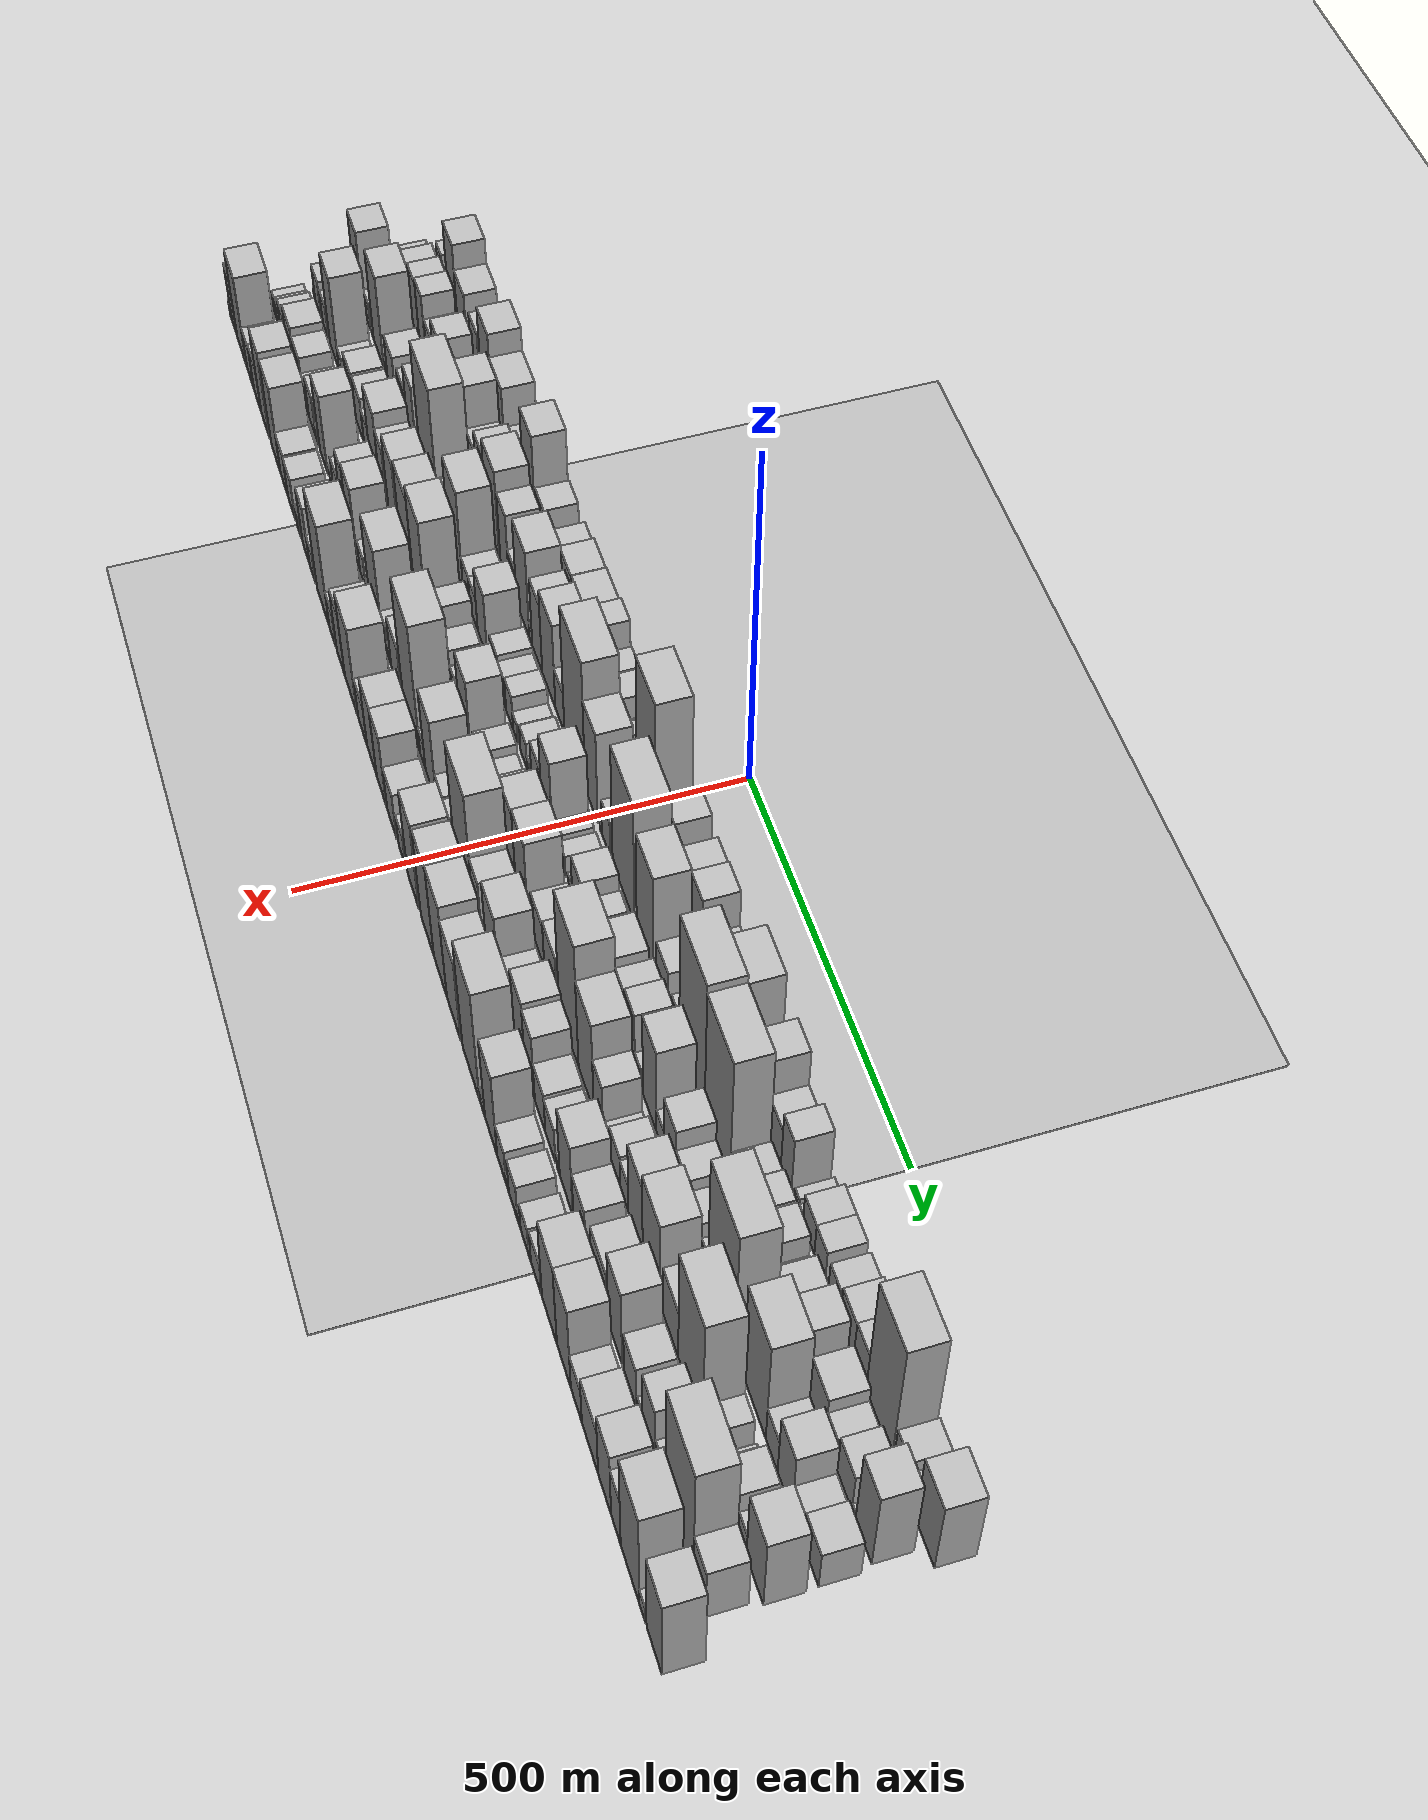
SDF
<?xml version="1.0" encoding="utf-8"?>

<sdf version="1.6">

   <world name="default">

      <gui fullscreen="0">

         <camera name="user_camera">

            <pose>-15 0 4.57585 0 0 0</pose>

            <view_controller>orbit</view_controller>

         </camera>

      </gui>

      <scene>

         <sky>

           <clouds>

             <speed>12</speed>

           </clouds>

         </sky>

         <ambient>0.4 0.4 0.4 1</ambient>

         <background>0.7 0.7 0.7 1</background>

         <shadows>1</shadows>

      </scene>

      <gravity>0 0 -9.8066</gravity>

      <magnetic_field>6e-06 2.3e-05 -4.2e-05</magnetic_field>

      <physics default="0" name="default_physics" type="ode">

         <ode>

            <solver>

               <type>quick</type>

               <iters>10</iters>

               <sor>1.0</sor>

               <use_dynamic_moi_rescaling>0</use_dynamic_moi_rescaling>

            </solver>

            <constraints>

               <cfm>0</cfm>

               <erp>0.2</erp>

               <contact_max_correcting_vel>100</contact_max_correcting_vel>

               <contact_surface_layer>0.001</contact_surface_layer>

            </constraints>

         </ode>

         <max_step_size>0.004</max_step_size>

         <real_time_factor>1</real_time_factor>

         <real_time_update_rate>250</real_time_update_rate>

      </physics>

      <light name="sun" type="directional">

         <cast_shadows>1</cast_shadows>

         <pose>0 0 10 0 0 0</pose>

         <diffuse>0.8 0.8 0.8 1</diffuse>

         <specular>0.2 0.2 0.2 1</specular>

         <attenuation>

            <range>1000</range>

            <constant>0.9</constant>

            <linear>0.01</linear>

            <quadratic>0.001</quadratic>

         </attenuation>

         <direction>-0.5 0.1 -0.9</direction>

      </light>

      <include>

         <name>ground_plane_1</name>

         <uri>model://HANNAS_ground_plane</uri>

         <pose>0 0 0  0 0 0</pose>

      </include>

      <include>

         <name>ground_plane_2</name>

         <uri>model://HANNAS_ground_plane</uri>

         <pose>100 0 0  0 0 0</pose>

      </include>

      <model name="building_1">

         <static>1</static>

         <pose frame="">100.0000 -846.7024 0 0.000000 0.000000 0.000000</pose>

         <link name="link">

            <pose frame="">0 0 24.00 0 0 0</pose>

            <collision name="collision">

               <geometry>

                  <box>

                     <size>40.0000 26.5952 48.0000</size>

                  </box>

               </geometry>

               <max_contacts>10</max_contacts>

               <surface>

                  <contact>

                     <ode/>

                  </contact>

                  <bounce/>

                  <friction>

                     <torsional>

                        <ode/>

                     </torsional>

                     <ode/>

                  </friction>

               </surface>

            </collision>

            <visual name="visual">

               <cast_shadows>0</cast_shadows>

               <geometry>

                  <box>

                     <size>40.0000 26.5952 48.0000</size>

                  </box>

               </geometry>

               <material>

                  <script>

                     <uri>model://HANNAS_wall/materials/scripts</uri>

                     <uri>model://HANNAS_wall/materials/textures</uri>

                     <name>vrc/HANNAS_wall</name>

                  </script>

               </material>

            </visual>

            <self_collide>0</self_collide>

            <enable_wind>0</enable_wind>

            <kinematic>0</kinematic>

         </link>

      </model>

      <model name="building_2">

         <static>1</static>

         <pose frame="">100.0000 -822.7520 0 0.000000 0.000000 0.000000</pose>

         <link name="link">

            <pose frame="">0 0 13.50 0 0 0</pose>

            <collision name="collision">

               <geometry>

                  <box>

                     <size>40.0000 13.3056 27.0000</size>

                  </box>

               </geometry>

               <max_contacts>10</max_contacts>

               <surface>

                  <contact>

                     <ode/>

                  </contact>

                  <bounce/>

                  <friction>

                     <torsional>

                        <ode/>

                     </torsional>

                     <ode/>

                  </friction>

               </surface>

            </collision>

            <visual name="visual">

               <cast_shadows>0</cast_shadows>

               <geometry>

                  <box>

                     <size>40.0000 13.3056 27.0000</size>

                  </box>

               </geometry>

               <material>

                  <script>

                     <uri>model://HANNAS_wall/materials/scripts</uri>

                     <uri>model://HANNAS_wall/materials/textures</uri>

                     <name>vrc/HANNAS_wall</name>

                  </script>

               </material>

            </visual>

            <self_collide>0</self_collide>

            <enable_wind>0</enable_wind>

            <kinematic>0</kinematic>

         </link>

      </model>

      <model name="building_3">

         <static>1</static>

         <pose frame="">100.0000 -788.0539 0 0.000000 0.000000 0.000000</pose>

         <link name="link">

            <pose frame="">0 0 61.50 0 0 0</pose>

            <collision name="collision">

               <geometry>

                  <box>

                     <size>40.0000 44.0907 123.0000</size>

                  </box>

               </geometry>

               <max_contacts>10</max_contacts>

               <surface>

                  <contact>

                     <ode/>

                  </contact>

                  <bounce/>

                  <friction>

                     <torsional>

                        <ode/>

                     </torsional>

                     <ode/>

                  </friction>

               </surface>

            </collision>

            <visual name="visual">

               <cast_shadows>0</cast_shadows>

               <geometry>

                  <box>

                     <size>40.0000 44.0907 123.0000</size>

                  </box>

               </geometry>

               <material>

                  <script>

                     <uri>model://HANNAS_wall/materials/scripts</uri>

                     <uri>model://HANNAS_wall/materials/textures</uri>

                     <name>vrc/HANNAS_wall</name>

                  </script>

               </material>

            </visual>

            <self_collide>0</self_collide>

            <enable_wind>0</enable_wind>

            <kinematic>0</kinematic>

         </link>

      </model>

      <model name="building_4">

         <static>1</static>

         <pose frame="">100.0000 -743.5289 0 0.000000 0.000000 0.000000</pose>

         <link name="link">

            <pose frame="">0 0 42.00 0 0 0</pose>

            <collision name="collision">

               <geometry>

                  <box>

                     <size>40.0000 44.9591 84.0000</size>

                  </box>

               </geometry>

               <max_contacts>10</max_contacts>

               <surface>

                  <contact>

                     <ode/>

                  </contact>

                  <bounce/>

                  <friction>

                     <torsional>

                        <ode/>

                     </torsional>

                     <ode/>

                  </friction>

               </surface>

            </collision>

            <visual name="visual">

               <cast_shadows>0</cast_shadows>

               <geometry>

                  <box>

                     <size>40.0000 44.9591 84.0000</size>

                  </box>

               </geometry>

               <material>

                  <script>

                     <uri>model://HANNAS_wall/materials/scripts</uri>

                     <uri>model://HANNAS_wall/materials/textures</uri>

                     <name>vrc/HANNAS_wall</name>

                  </script>

               </material>

            </visual>

            <self_collide>0</self_collide>

            <enable_wind>0</enable_wind>

            <kinematic>0</kinematic>

         </link>

      </model>

      <model name="building_5">

         <static>1</static>

         <pose frame="">100.0000 -711.0228 0 0.000000 0.000000 0.000000</pose>

         <link name="link">

            <pose frame="">0 0 19.50 0 0 0</pose>

            <collision name="collision">

               <geometry>

                  <box>

                     <size>40.0000 20.0532 39.0000</size>

                  </box>

               </geometry>

               <max_contacts>10</max_contacts>

               <surface>

                  <contact>

                     <ode/>

                  </contact>

                  <bounce/>

                  <friction>

                     <torsional>

                        <ode/>

                     </torsional>

                     <ode/>

                  </friction>

               </surface>

            </collision>

            <visual name="visual">

               <cast_shadows>0</cast_shadows>

               <geometry>

                  <box>

                     <size>40.0000 20.0532 39.0000</size>

                  </box>

               </geometry>

               <material>

                  <script>

                     <uri>model://HANNAS_wall/materials/scripts</uri>

                     <uri>model://HANNAS_wall/materials/textures</uri>

                     <name>vrc/HANNAS_wall</name>

                  </script>

               </material>

            </visual>

            <self_collide>0</self_collide>

            <enable_wind>0</enable_wind>

            <kinematic>0</kinematic>

         </link>

      </model>

      <model name="building_6">

         <static>1</static>

         <pose frame="">100.0000 -682.1669 0 0.000000 0.000000 0.000000</pose>

         <link name="link">

            <pose frame="">0 0 37.50 0 0 0</pose>

            <collision name="collision">

               <geometry>

                  <box>

                     <size>40.0000 37.6586 75.0000</size>

                  </box>

               </geometry>

               <max_contacts>10</max_contacts>

               <surface>

                  <contact>

                     <ode/>

                  </contact>

                  <bounce/>

                  <friction>

                     <torsional>

                        <ode/>

                     </torsional>

                     <ode/>

                  </friction>

               </surface>

            </collision>

            <visual name="visual">

               <cast_shadows>0</cast_shadows>

               <geometry>

                  <box>

                     <size>40.0000 37.6586 75.0000</size>

                  </box>

               </geometry>

               <material>

                  <script>

                     <uri>model://HANNAS_wall/materials/scripts</uri>

                     <uri>model://HANNAS_wall/materials/textures</uri>

                     <name>vrc/HANNAS_wall</name>

                  </script>

               </material>

            </visual>

            <self_collide>0</self_collide>

            <enable_wind>0</enable_wind>

            <kinematic>0</kinematic>

         </link>

      </model>

      <model name="building_7">

         <static>1</static>

         <pose frame="">100.0000 -630.3527 0 0.000000 0.000000 0.000000</pose>

         <link name="link">

            <pose frame="">0 0 63.00 0 0 0</pose>

            <collision name="collision">

               <geometry>

                  <box>

                     <size>40.0000 47.9698 126.0000</size>

                  </box>

               </geometry>

               <max_contacts>10</max_contacts>

               <surface>

                  <contact>

                     <ode/>

                  </contact>

                  <bounce/>

                  <friction>

                     <torsional>

                        <ode/>

                     </torsional>

                     <ode/>

                  </friction>

               </surface>

            </collision>

            <visual name="visual">

               <cast_shadows>0</cast_shadows>

               <geometry>

                  <box>

                     <size>40.0000 47.9698 126.0000</size>

                  </box>

               </geometry>

               <material>

                  <script>

                     <uri>model://HANNAS_wall/materials/scripts</uri>

                     <uri>model://HANNAS_wall/materials/textures</uri>

                     <name>vrc/HANNAS_wall</name>

                  </script>

               </material>

            </visual>

            <self_collide>0</self_collide>

            <enable_wind>0</enable_wind>

            <kinematic>0</kinematic>

         </link>

      </model>

      <model name="building_8">

         <static>1</static>

         <pose frame="">100.0000 -579.6468 0 0.000000 0.000000 0.000000</pose>

         <link name="link">

            <pose frame="">0 0 45.00 0 0 0</pose>

            <collision name="collision">

               <geometry>

                  <box>

                     <size>40.0000 53.4419 90.0000</size>

                  </box>

               </geometry>

               <max_contacts>10</max_contacts>

               <surface>

                  <contact>

                     <ode/>

                  </contact>

                  <bounce/>

                  <friction>

                     <torsional>

                        <ode/>

                     </torsional>

                     <ode/>

                  </friction>

               </surface>

            </collision>

            <visual name="visual">

               <cast_shadows>0</cast_shadows>

               <geometry>

                  <box>

                     <size>40.0000 53.4419 90.0000</size>

                  </box>

               </geometry>

               <material>

                  <script>

                     <uri>model://HANNAS_wall/materials/scripts</uri>

                     <uri>model://HANNAS_wall/materials/textures</uri>

                     <name>vrc/HANNAS_wall</name>

                  </script>

               </material>

            </visual>

            <self_collide>0</self_collide>

            <enable_wind>0</enable_wind>

            <kinematic>0</kinematic>

         </link>

      </model>

      <model name="building_9">

         <static>1</static>

         <pose frame="">100.0000 -543.1894 0 0.000000 0.000000 0.000000</pose>

         <link name="link">

            <pose frame="">0 0 7.50 0 0 0</pose>

            <collision name="collision">

               <geometry>

                  <box>

                     <size>40.0000 7.4730 15.0000</size>

                  </box>

               </geometry>

               <max_contacts>10</max_contacts>

               <surface>

                  <contact>

                     <ode/>

                  </contact>

                  <bounce/>

                  <friction>

                     <torsional>

                        <ode/>

                     </torsional>

                     <ode/>

                  </friction>

               </surface>

            </collision>

            <visual name="visual">

               <cast_shadows>0</cast_shadows>

               <geometry>

                  <box>

                     <size>40.0000 7.4730 15.0000</size>

                  </box>

               </geometry>

               <material>

                  <script>

                     <uri>model://HANNAS_wall/materials/scripts</uri>

                     <uri>model://HANNAS_wall/materials/textures</uri>

                     <name>vrc/HANNAS_wall</name>

                  </script>

               </material>

            </visual>

            <self_collide>0</self_collide>

            <enable_wind>0</enable_wind>

            <kinematic>0</kinematic>

         </link>

      </model>

      <model name="building_10">

         <static>1</static>

         <pose frame="">100.0000 -527.8395 0 0.000000 0.000000 0.000000</pose>

         <link name="link">

            <pose frame="">0 0 21.00 0 0 0</pose>

            <collision name="collision">

               <geometry>

                  <box>

                     <size>40.0000 23.2268 42.0000</size>

                  </box>

               </geometry>

               <max_contacts>10</max_contacts>

               <surface>

                  <contact>

                     <ode/>

                  </contact>

                  <bounce/>

                  <friction>

                     <torsional>

                        <ode/>

                     </torsional>

                     <ode/>

                  </friction>

               </surface>

            </collision>

            <visual name="visual">

               <cast_shadows>0</cast_shadows>

               <geometry>

                  <box>

                     <size>40.0000 23.2268 42.0000</size>

                  </box>

               </geometry>

               <material>

                  <script>

                     <uri>model://HANNAS_wall/materials/scripts</uri>

                     <uri>model://HANNAS_wall/materials/textures</uri>

                     <name>vrc/HANNAS_wall</name>

                  </script>

               </material>

            </visual>

            <self_collide>0</self_collide>

            <enable_wind>0</enable_wind>

            <kinematic>0</kinematic>

         </link>

      </model>

      <model name="building_11">

         <static>1</static>

         <pose frame="">100.0000 -505.2361 0 0.000000 0.000000 0.000000</pose>

         <link name="link">

            <pose frame="">0 0 19.50 0 0 0</pose>

            <collision name="collision">

               <geometry>

                  <box>

                     <size>40.0000 21.9800 39.0000</size>

                  </box>

               </geometry>

               <max_contacts>10</max_contacts>

               <surface>

                  <contact>

                     <ode/>

                  </contact>

                  <bounce/>

                  <friction>

                     <torsional>

                        <ode/>

                     </torsional>

                     <ode/>

                  </friction>

               </surface>

            </collision>

            <visual name="visual">

               <cast_shadows>0</cast_shadows>

               <geometry>

                  <box>

                     <size>40.0000 21.9800 39.0000</size>

                  </box>

               </geometry>

               <material>

                  <script>

                     <uri>model://HANNAS_wall/materials/scripts</uri>

                     <uri>model://HANNAS_wall/materials/textures</uri>

                     <name>vrc/HANNAS_wall</name>

                  </script>

               </material>

            </visual>

            <self_collide>0</self_collide>

            <enable_wind>0</enable_wind>

            <kinematic>0</kinematic>

         </link>

      </model>

      <model name="building_12">

         <static>1</static>

         <pose frame="">100.0000 -480.6584 0 0.000000 0.000000 0.000000</pose>

         <link name="link">

            <pose frame="">0 0 25.50 0 0 0</pose>

            <collision name="collision">

               <geometry>

                  <box>

                     <size>40.0000 27.1754 51.0000</size>

                  </box>

               </geometry>

               <max_contacts>10</max_contacts>

               <surface>

                  <contact>

                     <ode/>

                  </contact>

                  <bounce/>

                  <friction>

                     <torsional>

                        <ode/>

                     </torsional>

                     <ode/>

                  </friction>

               </surface>

            </collision>

            <visual name="visual">

               <cast_shadows>0</cast_shadows>

               <geometry>

                  <box>

                     <size>40.0000 27.1754 51.0000</size>

                  </box>

               </geometry>

               <material>

                  <script>

                     <uri>model://HANNAS_wall/materials/scripts</uri>

                     <uri>model://HANNAS_wall/materials/textures</uri>

                     <name>vrc/HANNAS_wall</name>

                  </script>

               </material>

            </visual>

            <self_collide>0</self_collide>

            <enable_wind>0</enable_wind>

            <kinematic>0</kinematic>

         </link>

      </model>

      <model name="building_13">

         <static>1</static>

         <pose frame="">100.0000 -442.8668 0 0.000000 0.000000 0.000000</pose>

         <link name="link">

            <pose frame="">0 0 72.00 0 0 0</pose>

            <collision name="collision">

               <geometry>

                  <box>

                     <size>40.0000 48.4077 144.0000</size>

                  </box>

               </geometry>

               <max_contacts>10</max_contacts>

               <surface>

                  <contact>

                     <ode/>

                  </contact>

                  <bounce/>

                  <friction>

                     <torsional>

                        <ode/>

                     </torsional>

                     <ode/>

                  </friction>

               </surface>

            </collision>

            <visual name="visual">

               <cast_shadows>0</cast_shadows>

               <geometry>

                  <box>

                     <size>40.0000 48.4077 144.0000</size>

                  </box>

               </geometry>

               <material>

                  <script>

                     <uri>model://HANNAS_wall/materials/scripts</uri>

                     <uri>model://HANNAS_wall/materials/textures</uri>

                     <name>vrc/HANNAS_wall</name>

                  </script>

               </material>

            </visual>

            <self_collide>0</self_collide>

            <enable_wind>0</enable_wind>

            <kinematic>0</kinematic>

         </link>

      </model>

      <model name="building_14">

         <static>1</static>

         <pose frame="">100.0000 -394.2044 0 0.000000 0.000000 0.000000</pose>

         <link name="link">

            <pose frame="">0 0 34.50 0 0 0</pose>

            <collision name="collision">

               <geometry>

                  <box>

                     <size>40.0000 36.9172 69.0000</size>

                  </box>

               </geometry>

               <max_contacts>10</max_contacts>

               <surface>

                  <contact>

                     <ode/>

                  </contact>

                  <bounce/>

                  <friction>

                     <torsional>

                        <ode/>

                     </torsional>

                     <ode/>

                  </friction>

               </surface>

            </collision>

            <visual name="visual">

               <cast_shadows>0</cast_shadows>

               <geometry>

                  <box>

                     <size>40.0000 36.9172 69.0000</size>

                  </box>

               </geometry>

               <material>

                  <script>

                     <uri>model://HANNAS_wall/materials/scripts</uri>

                     <uri>model://HANNAS_wall/materials/textures</uri>

                     <name>vrc/HANNAS_wall</name>

                  </script>

               </material>

            </visual>

            <self_collide>0</self_collide>

            <enable_wind>0</enable_wind>

            <kinematic>0</kinematic>

         </link>

      </model>

      <model name="building_15">

         <static>1</static>

         <pose frame="">100.0000 -366.6062 0 0.000000 0.000000 0.000000</pose>

         <link name="link">

            <pose frame="">0 0 16.50 0 0 0</pose>

            <collision name="collision">

               <geometry>

                  <box>

                     <size>40.0000 18.2792 33.0000</size>

                  </box>

               </geometry>

               <max_contacts>10</max_contacts>

               <surface>

                  <contact>

                     <ode/>

                  </contact>

                  <bounce/>

                  <friction>

                     <torsional>

                        <ode/>

                     </torsional>

                     <ode/>

                  </friction>

               </surface>

            </collision>

            <visual name="visual">

               <cast_shadows>0</cast_shadows>

               <geometry>

                  <box>

                     <size>40.0000 18.2792 33.0000</size>

                  </box>

               </geometry>

               <material>

                  <script>

                     <uri>model://HANNAS_wall/materials/scripts</uri>

                     <uri>model://HANNAS_wall/materials/textures</uri>

                     <name>vrc/HANNAS_wall</name>

                  </script>

               </material>

            </visual>

            <self_collide>0</self_collide>

            <enable_wind>0</enable_wind>

            <kinematic>0</kinematic>

         </link>

      </model>

      <model name="building_16">

         <static>1</static>

         <pose frame="">100.0000 -330.9921 0 0.000000 0.000000 0.000000</pose>

         <link name="link">

            <pose frame="">0 0 33.00 0 0 0</pose>

            <collision name="collision">

               <geometry>

                  <box>

                     <size>40.0000 36.9489 66.0000</size>

                  </box>

               </geometry>

               <max_contacts>10</max_contacts>

               <surface>

                  <contact>

                     <ode/>

                  </contact>

                  <bounce/>

                  <friction>

                     <torsional>

                        <ode/>

                     </torsional>

                     <ode/>

                  </friction>

               </surface>

            </collision>

            <visual name="visual">

               <cast_shadows>0</cast_shadows>

               <geometry>

                  <box>

                     <size>40.0000 36.9489 66.0000</size>

                  </box>

               </geometry>

               <material>

                  <script>

                     <uri>model://HANNAS_wall/materials/scripts</uri>

                     <uri>model://HANNAS_wall/materials/textures</uri>

                     <name>vrc/HANNAS_wall</name>

                  </script>

               </material>

            </visual>

            <self_collide>0</self_collide>

            <enable_wind>0</enable_wind>

            <kinematic>0</kinematic>

         </link>

      </model>

      <model name="building_17">

         <static>1</static>

         <pose frame="">100.0000 -290.0274 0 0.000000 0.000000 0.000000</pose>

         <link name="link">

            <pose frame="">0 0 39.00 0 0 0</pose>

            <collision name="collision">

               <geometry>

                  <box>

                     <size>40.0000 44.9806 78.0000</size>

                  </box>

               </geometry>

               <max_contacts>10</max_contacts>

               <surface>

                  <contact>

                     <ode/>

                  </contact>

                  <bounce/>

                  <friction>

                     <torsional>

                        <ode/>

                     </torsional>

                     <ode/>

                  </friction>

               </surface>

            </collision>

            <visual name="visual">

               <cast_shadows>0</cast_shadows>

               <geometry>

                  <box>

                     <size>40.0000 44.9806 78.0000</size>

                  </box>

               </geometry>

               <material>

                  <script>

                     <uri>model://HANNAS_wall/materials/scripts</uri>

                     <uri>model://HANNAS_wall/materials/textures</uri>

                     <name>vrc/HANNAS_wall</name>

                  </script>

               </material>

            </visual>

            <self_collide>0</self_collide>

            <enable_wind>0</enable_wind>

            <kinematic>0</kinematic>

         </link>

      </model>

      <model name="building_18">

         <static>1</static>

         <pose frame="">100.0000 -240.7067 0 0.000000 0.000000 0.000000</pose>

         <link name="link">

            <pose frame="">0 0 40.50 0 0 0</pose>

            <collision name="collision">

               <geometry>

                  <box>

                     <size>40.0000 47.6607 81.0000</size>

                  </box>

               </geometry>

               <max_contacts>10</max_contacts>

               <surface>

                  <contact>

                     <ode/>

                  </contact>

                  <bounce/>

                  <friction>

                     <torsional>

                        <ode/>

                     </torsional>

                     <ode/>

                  </friction>

               </surface>

            </collision>

            <visual name="visual">

               <cast_shadows>0</cast_shadows>

               <geometry>

                  <box>

                     <size>40.0000 47.6607 81.0000</size>

                  </box>

               </geometry>

               <material>

                  <script>

                     <uri>model://HANNAS_wall/materials/scripts</uri>

                     <uri>model://HANNAS_wall/materials/textures</uri>

                     <name>vrc/HANNAS_wall</name>

                  </script>

               </material>

            </visual>

            <self_collide>0</self_collide>

            <enable_wind>0</enable_wind>

            <kinematic>0</kinematic>

         </link>

      </model>

      <model name="building_19">

         <static>1</static>

         <pose frame="">100.0000 -210.8324 0 0.000000 0.000000 0.000000</pose>

         <link name="link">

            <pose frame="">0 0 7.50 0 0 0</pose>

            <collision name="collision">

               <geometry>

                  <box>

                     <size>40.0000 6.0879 15.0000</size>

                  </box>

               </geometry>

               <max_contacts>10</max_contacts>

               <surface>

                  <contact>

                     <ode/>

                  </contact>

                  <bounce/>

                  <friction>

                     <torsional>

                        <ode/>

                     </torsional>

                     <ode/>

                  </friction>

               </surface>

            </collision>

            <visual name="visual">

               <cast_shadows>0</cast_shadows>

               <geometry>

                  <box>

                     <size>40.0000 6.0879 15.0000</size>

                  </box>

               </geometry>

               <material>

                  <script>

                     <uri>model://HANNAS_wall/materials/scripts</uri>

                     <uri>model://HANNAS_wall/materials/textures</uri>

                     <name>vrc/HANNAS_wall</name>

                  </script>

               </material>

            </visual>

            <self_collide>0</self_collide>

            <enable_wind>0</enable_wind>

            <kinematic>0</kinematic>

         </link>

      </model>

      <model name="building_20">

         <static>1</static>

         <pose frame="">100.0000 -191.2011 0 0.000000 0.000000 0.000000</pose>

         <link name="link">

            <pose frame="">0 0 46.50 0 0 0</pose>

            <collision name="collision">

               <geometry>

                  <box>

                     <size>40.0000 33.1748 93.0000</size>

                  </box>

               </geometry>

               <max_contacts>10</max_contacts>

               <surface>

                  <contact>

                     <ode/>

                  </contact>

                  <bounce/>

                  <friction>

                     <torsional>

                        <ode/>

                     </torsional>

                     <ode/>

                  </friction>

               </surface>

            </collision>

            <visual name="visual">

               <cast_shadows>0</cast_shadows>

               <geometry>

                  <box>

                     <size>40.0000 33.1748 93.0000</size>

                  </box>

               </geometry>

               <material>

                  <script>

                     <uri>model://HANNAS_wall/materials/scripts</uri>

                     <uri>model://HANNAS_wall/materials/textures</uri>

                     <name>vrc/HANNAS_wall</name>

                  </script>

               </material>

            </visual>

            <self_collide>0</self_collide>

            <enable_wind>0</enable_wind>

            <kinematic>0</kinematic>

         </link>

      </model>

      <model name="building_21">

         <static>1</static>

         <pose frame="">100.0000 -155.3330 0 0.000000 0.000000 0.000000</pose>

         <link name="link">

            <pose frame="">0 0 27.00 0 0 0</pose>

            <collision name="collision">

               <geometry>

                  <box>

                     <size>40.0000 30.5614 54.0000</size>

                  </box>

               </geometry>

               <max_contacts>10</max_contacts>

               <surface>

                  <contact>

                     <ode/>

                  </contact>

                  <bounce/>

                  <friction>

                     <torsional>

                        <ode/>

                     </torsional>

                     <ode/>

                  </friction>

               </surface>

            </collision>

            <visual name="visual">

               <cast_shadows>0</cast_shadows>

               <geometry>

                  <box>

                     <size>40.0000 30.5614 54.0000</size>

                  </box>

               </geometry>

               <material>

                  <script>

                     <uri>model://HANNAS_wall/materials/scripts</uri>

                     <uri>model://HANNAS_wall/materials/textures</uri>

                     <name>vrc/HANNAS_wall</name>

                  </script>

               </material>

            </visual>

            <self_collide>0</self_collide>

            <enable_wind>0</enable_wind>

            <kinematic>0</kinematic>

         </link>

      </model>

      <model name="building_22">

         <static>1</static>

         <pose frame="">100.0000 -116.2851 0 0.000000 0.000000 0.000000</pose>

         <link name="link">

            <pose frame="">0 0 30.00 0 0 0</pose>

            <collision name="collision">

               <geometry>

                  <box>

                     <size>40.0000 35.5343 60.0000</size>

                  </box>

               </geometry>

               <max_contacts>10</max_contacts>

               <surface>

                  <contact>

                     <ode/>

                  </contact>

                  <bounce/>

                  <friction>

                     <torsional>

                        <ode/>

                     </torsional>

                     <ode/>

                  </friction>

               </surface>

            </collision>

            <visual name="visual">

               <cast_shadows>0</cast_shadows>

               <geometry>

                  <box>

                     <size>40.0000 35.5343 60.0000</size>

                  </box>

               </geometry>

               <material>

                  <script>

                     <uri>model://HANNAS_wall/materials/scripts</uri>

                     <uri>model://HANNAS_wall/materials/textures</uri>

                     <name>vrc/HANNAS_wall</name>

                  </script>

               </material>

            </visual>

            <self_collide>0</self_collide>

            <enable_wind>0</enable_wind>

            <kinematic>0</kinematic>

         </link>

      </model>

      <model name="building_23">

         <static>1</static>

         <pose frame="">100.0000 -89.9354 0 0.000000 0.000000 0.000000</pose>

         <link name="link">

            <pose frame="">0 0 13.50 0 0 0</pose>

            <collision name="collision">

               <geometry>

                  <box>

                     <size>40.0000 11.1652 27.0000</size>

                  </box>

               </geometry>

               <max_contacts>10</max_contacts>

               <surface>

                  <contact>

                     <ode/>

                  </contact>

                  <bounce/>

                  <friction>

                     <torsional>

                        <ode/>

                     </torsional>

                     <ode/>

                  </friction>

               </surface>

            </collision>

            <visual name="visual">

               <cast_shadows>0</cast_shadows>

               <geometry>

                  <box>

                     <size>40.0000 11.1652 27.0000</size>

                  </box>

               </geometry>

               <material>

                  <script>

                     <uri>model://HANNAS_wall/materials/scripts</uri>

                     <uri>model://HANNAS_wall/materials/textures</uri>

                     <name>vrc/HANNAS_wall</name>

                  </script>

               </material>

            </visual>

            <self_collide>0</self_collide>

            <enable_wind>0</enable_wind>

            <kinematic>0</kinematic>

         </link>

      </model>

      <model name="building_24">

         <static>1</static>

         <pose frame="">100.0000 -73.9870 0 0.000000 0.000000 0.000000</pose>

         <link name="link">

            <pose frame="">0 0 19.50 0 0 0</pose>

            <collision name="collision">

               <geometry>

                  <box>

                     <size>40.0000 20.7316 39.0000</size>

                  </box>

               </geometry>

               <max_contacts>10</max_contacts>

               <surface>

                  <contact>

                     <ode/>

                  </contact>

                  <bounce/>

                  <friction>

                     <torsional>

                        <ode/>

                     </torsional>

                     <ode/>

                  </friction>

               </surface>

            </collision>

            <visual name="visual">

               <cast_shadows>0</cast_shadows>

               <geometry>

                  <box>

                     <size>40.0000 20.7316 39.0000</size>

                  </box>

               </geometry>

               <material>

                  <script>

                     <uri>model://HANNAS_wall/materials/scripts</uri>

                     <uri>model://HANNAS_wall/materials/textures</uri>

                     <name>vrc/HANNAS_wall</name>

                  </script>

               </material>

            </visual>

            <self_collide>0</self_collide>

            <enable_wind>0</enable_wind>

            <kinematic>0</kinematic>

         </link>

      </model>

      <model name="building_25">

         <static>1</static>

         <pose frame="">100.0000 -50.6475 0 0.000000 0.000000 0.000000</pose>

         <link name="link">

            <pose frame="">0 0 9.00 0 0 0</pose>

            <collision name="collision">

               <geometry>

                  <box>

                     <size>40.0000 7.9473 18.0000</size>

                  </box>

               </geometry>

               <max_contacts>10</max_contacts>

               <surface>

                  <contact>

                     <ode/>

                  </contact>

                  <bounce/>

                  <friction>

                     <torsional>

                        <ode/>

                     </torsional>

                     <ode/>

                  </friction>

               </surface>

            </collision>

            <visual name="visual">

               <cast_shadows>0</cast_shadows>

               <geometry>

                  <box>

                     <size>40.0000 7.9473 18.0000</size>

                  </box>

               </geometry>

               <material>

                  <script>

                     <uri>model://HANNAS_wall/materials/scripts</uri>

                     <uri>model://HANNAS_wall/materials/textures</uri>

                     <name>vrc/HANNAS_wall</name>

                  </script>

               </material>

            </visual>

            <self_collide>0</self_collide>

            <enable_wind>0</enable_wind>

            <kinematic>0</kinematic>

         </link>

      </model>

      <model name="building_26">

         <static>1</static>

         <pose frame="">100.0000 -33.1180 0 0.000000 0.000000 0.000000</pose>

         <link name="link">

            <pose frame="">0 0 16.50 0 0 0</pose>

            <collision name="collision">

               <geometry>

                  <box>

                     <size>40.0000 17.1118 33.0000</size>

                  </box>

               </geometry>

               <max_contacts>10</max_contacts>

               <surface>

                  <contact>

                     <ode/>

                  </contact>

                  <bounce/>

                  <friction>

                     <torsional>

                        <ode/>

                     </torsional>

                     <ode/>

                  </friction>

               </surface>

            </collision>

            <visual name="visual">

               <cast_shadows>0</cast_shadows>

               <geometry>

                  <box>

                     <size>40.0000 17.1118 33.0000</size>

                  </box>

               </geometry>

               <material>

                  <script>

                     <uri>model://HANNAS_wall/materials/scripts</uri>

                     <uri>model://HANNAS_wall/materials/textures</uri>

                     <name>vrc/HANNAS_wall</name>

                  </script>

               </material>

            </visual>

            <self_collide>0</self_collide>

            <enable_wind>0</enable_wind>

            <kinematic>0</kinematic>

         </link>

      </model>

      <model name="building_27">

         <static>1</static>

         <pose frame="">100.0000 13.2216 0 0.000000 0.000000 0.000000</pose>

         <link name="link">

            <pose frame="">0 0 112.50 0 0 0</pose>

            <collision name="collision">

               <geometry>

                  <box>

                     <size>40.0000 67.5674 225.0000</size>

                  </box>

               </geometry>

               <max_contacts>10</max_contacts>

               <surface>

                  <contact>

                     <ode/>

                  </contact>

                  <bounce/>

                  <friction>

                     <torsional>

                        <ode/>

                     </torsional>

                     <ode/>

                  </friction>

               </surface>

            </collision>

            <visual name="visual">

               <cast_shadows>0</cast_shadows>

               <geometry>

                  <box>

                     <size>40.0000 67.5674 225.0000</size>

                  </box>

               </geometry>

               <material>

                  <script>

                     <uri>model://HANNAS_wall/materials/scripts</uri>

                     <uri>model://HANNAS_wall/materials/textures</uri>

                     <name>vrc/HANNAS_wall</name>

                  </script>

               </material>

            </visual>

            <self_collide>0</self_collide>

            <enable_wind>0</enable_wind>

            <kinematic>0</kinematic>

         </link>

      </model>

      <model name="building_28">

         <static>1</static>

         <pose frame="">100.0000 64.4764 0 0.000000 0.000000 0.000000</pose>

         <link name="link">

            <pose frame="">0 0 24.00 0 0 0</pose>

            <collision name="collision">

               <geometry>

                  <box>

                     <size>40.0000 26.9421 48.0000</size>

                  </box>

               </geometry>

               <max_contacts>10</max_contacts>

               <surface>

                  <contact>

                     <ode/>

                  </contact>

                  <bounce/>

                  <friction>

                     <torsional>

                        <ode/>

                     </torsional>

                     <ode/>

                  </friction>

               </surface>

            </collision>

            <visual name="visual">

               <cast_shadows>0</cast_shadows>

               <geometry>

                  <box>

                     <size>40.0000 26.9421 48.0000</size>

                  </box>

               </geometry>

               <material>

                  <script>

                     <uri>model://HANNAS_wall/materials/scripts</uri>

                     <uri>model://HANNAS_wall/materials/textures</uri>

                     <name>vrc/HANNAS_wall</name>

                  </script>

               </material>

            </visual>

            <self_collide>0</self_collide>

            <enable_wind>0</enable_wind>

            <kinematic>0</kinematic>

         </link>

      </model>

      <model name="building_29">

         <static>1</static>

         <pose frame="">100.0000 95.3213 0 0.000000 0.000000 0.000000</pose>

         <link name="link">

            <pose frame="">0 0 55.50 0 0 0</pose>

            <collision name="collision">

               <geometry>

                  <box>

                     <size>40.0000 34.7477 111.0000</size>

                  </box>

               </geometry>

               <max_contacts>10</max_contacts>

               <surface>

                  <contact>

                     <ode/>

                  </contact>

                  <bounce/>

                  <friction>

                     <torsional>

                        <ode/>

                     </torsional>

                     <ode/>

                  </friction>

               </surface>

            </collision>

            <visual name="visual">

               <cast_shadows>0</cast_shadows>

               <geometry>

                  <box>

                     <size>40.0000 34.7477 111.0000</size>

                  </box>

               </geometry>

               <material>

                  <script>

                     <uri>model://HANNAS_wall/materials/scripts</uri>

                     <uri>model://HANNAS_wall/materials/textures</uri>

                     <name>vrc/HANNAS_wall</name>

                  </script>

               </material>

            </visual>

            <self_collide>0</self_collide>

            <enable_wind>0</enable_wind>

            <kinematic>0</kinematic>

         </link>

      </model>

      <model name="building_30">

         <static>1</static>

         <pose frame="">100.0000 122.2101 0 0.000000 0.000000 0.000000</pose>

         <link name="link">

            <pose frame="">0 0 16.50 0 0 0</pose>

            <collision name="collision">

               <geometry>

                  <box>

                     <size>40.0000 19.0299 33.0000</size>

                  </box>

               </geometry>

               <max_contacts>10</max_contacts>

               <surface>

                  <contact>

                     <ode/>

                  </contact>

                  <bounce/>

                  <friction>

                     <torsional>

                        <ode/>

                     </torsional>

                     <ode/>

                  </friction>

               </surface>

            </collision>

            <visual name="visual">

               <cast_shadows>0</cast_shadows>

               <geometry>

                  <box>

                     <size>40.0000 19.0299 33.0000</size>

                  </box>

               </geometry>

               <material>

                  <script>

                     <uri>model://HANNAS_wall/materials/scripts</uri>

                     <uri>model://HANNAS_wall/materials/textures</uri>

                     <name>vrc/HANNAS_wall</name>

                  </script>

               </material>

            </visual>

            <self_collide>0</self_collide>

            <enable_wind>0</enable_wind>

            <kinematic>0</kinematic>

         </link>

      </model>

      <model name="building_31">

         <static>1</static>

         <pose frame="">100.0000 149.9771 0 0.000000 0.000000 0.000000</pose>

         <link name="link">

            <pose frame="">0 0 49.50 0 0 0</pose>

            <collision name="collision">

               <geometry>

                  <box>

                     <size>40.0000 36.5041 99.0000</size>

                  </box>

               </geometry>

               <max_contacts>10</max_contacts>

               <surface>

                  <contact>

                     <ode/>

                  </contact>

                  <bounce/>

                  <friction>

                     <torsional>

                        <ode/>

                     </torsional>

                     <ode/>

                  </friction>

               </surface>

            </collision>

            <visual name="visual">

               <cast_shadows>0</cast_shadows>

               <geometry>

                  <box>

                     <size>40.0000 36.5041 99.0000</size>

                  </box>

               </geometry>

               <material>

                  <script>

                     <uri>model://HANNAS_wall/materials/scripts</uri>

                     <uri>model://HANNAS_wall/materials/textures</uri>

                     <name>vrc/HANNAS_wall</name>

                  </script>

               </material>

            </visual>

            <self_collide>0</self_collide>

            <enable_wind>0</enable_wind>

            <kinematic>0</kinematic>

         </link>

      </model>

      <model name="building_32">

         <static>1</static>

         <pose frame="">100.0000 187.5665 0 0.000000 0.000000 0.000000</pose>

         <link name="link">

            <pose frame="">0 0 52.50 0 0 0</pose>

            <collision name="collision">

               <geometry>

                  <box>

                     <size>40.0000 38.6749 105.0000</size>

                  </box>

               </geometry>

               <max_contacts>10</max_contacts>

               <surface>

                  <contact>

                     <ode/>

                  </contact>

                  <bounce/>

                  <friction>

                     <torsional>

                        <ode/>

                     </torsional>

                     <ode/>

                  </friction>

               </surface>

            </collision>

            <visual name="visual">

               <cast_shadows>0</cast_shadows>

               <geometry>

                  <box>

                     <size>40.0000 38.6749 105.0000</size>

                  </box>

               </geometry>

               <material>

                  <script>

                     <uri>model://HANNAS_wall/materials/scripts</uri>

                     <uri>model://HANNAS_wall/materials/textures</uri>

                     <name>vrc/HANNAS_wall</name>

                  </script>

               </material>

            </visual>

            <self_collide>0</self_collide>

            <enable_wind>0</enable_wind>

            <kinematic>0</kinematic>

         </link>

      </model>

      <model name="building_33">

         <static>1</static>

         <pose frame="">100.0000 218.9175 0 0.000000 0.000000 0.000000</pose>

         <link name="link">

            <pose frame="">0 0 22.50 0 0 0</pose>

            <collision name="collision">

               <geometry>

                  <box>

                     <size>40.0000 24.0271 45.0000</size>

                  </box>

               </geometry>

               <max_contacts>10</max_contacts>

               <surface>

                  <contact>

                     <ode/>

                  </contact>

                  <bounce/>

                  <friction>

                     <torsional>

                        <ode/>

                     </torsional>

                     <ode/>

                  </friction>

               </surface>

            </collision>

            <visual name="visual">

               <cast_shadows>0</cast_shadows>

               <geometry>

                  <box>

                     <size>40.0000 24.0271 45.0000</size>

                  </box>

               </geometry>

               <material>

                  <script>

                     <uri>model://HANNAS_wall/materials/scripts</uri>

                     <uri>model://HANNAS_wall/materials/textures</uri>

                     <name>vrc/HANNAS_wall</name>

                  </script>

               </material>

            </visual>

            <self_collide>0</self_collide>

            <enable_wind>0</enable_wind>

            <kinematic>0</kinematic>

         </link>

      </model>

      <model name="building_34">

         <static>1</static>

         <pose frame="">100.0000 239.6383 0 0.000000 0.000000 0.000000</pose>

         <link name="link">

            <pose frame="">0 0 16.50 0 0 0</pose>

            <collision name="collision">

               <geometry>

                  <box>

                     <size>40.0000 17.4144 33.0000</size>

                  </box>

               </geometry>

               <max_contacts>10</max_contacts>

               <surface>

                  <contact>

                     <ode/>

                  </contact>

                  <bounce/>

                  <friction>

                     <torsional>

                        <ode/>

                     </torsional>

                     <ode/>

                  </friction>

               </surface>

            </collision>

            <visual name="visual">

               <cast_shadows>0</cast_shadows>

               <geometry>

                  <box>

                     <size>40.0000 17.4144 33.0000</size>

                  </box>

               </geometry>

               <material>

                  <script>

                     <uri>model://HANNAS_wall/materials/scripts</uri>

                     <uri>model://HANNAS_wall/materials/textures</uri>

                     <name>vrc/HANNAS_wall</name>

                  </script>

               </material>

            </visual>

            <self_collide>0</self_collide>

            <enable_wind>0</enable_wind>

            <kinematic>0</kinematic>

         </link>

      </model>

      <model name="building_35">

         <static>1</static>

         <pose frame="">100.0000 265.8331 0 0.000000 0.000000 0.000000</pose>

         <link name="link">

            <pose frame="">0 0 34.50 0 0 0</pose>

            <collision name="collision">

               <geometry>

                  <box>

                     <size>40.0000 34.9752 69.0000</size>

                  </box>

               </geometry>

               <max_contacts>10</max_contacts>

               <surface>

                  <contact>

                     <ode/>

                  </contact>

                  <bounce/>

                  <friction>

                     <torsional>

                        <ode/>

                     </torsional>

                     <ode/>

                  </friction>

               </surface>

            </collision>

            <visual name="visual">

               <cast_shadows>0</cast_shadows>

               <geometry>

                  <box>

                     <size>40.0000 34.9752 69.0000</size>

                  </box>

               </geometry>

               <material>

                  <script>

                     <uri>model://HANNAS_wall/materials/scripts</uri>

                     <uri>model://HANNAS_wall/materials/textures</uri>

                     <name>vrc/HANNAS_wall</name>

                  </script>

               </material>

            </visual>

            <self_collide>0</self_collide>

            <enable_wind>0</enable_wind>

            <kinematic>0</kinematic>

         </link>

      </model>

      <model name="building_36">

         <static>1</static>

         <pose frame="">100.0000 313.4848 0 0.000000 0.000000 0.000000</pose>

         <link name="link">

            <pose frame="">0 0 76.50 0 0 0</pose>

            <collision name="collision">

               <geometry>

                  <box>

                     <size>40.0000 60.3282 153.0000</size>

                  </box>

               </geometry>

               <max_contacts>10</max_contacts>

               <surface>

                  <contact>

                     <ode/>

                  </contact>

                  <bounce/>

                  <friction>

                     <torsional>

                        <ode/>

                     </torsional>

                     <ode/>

                  </friction>

               </surface>

            </collision>

            <visual name="visual">

               <cast_shadows>0</cast_shadows>

               <geometry>

                  <box>

                     <size>40.0000 60.3282 153.0000</size>

                  </box>

               </geometry>

               <material>

                  <script>

                     <uri>model://HANNAS_wall/materials/scripts</uri>

                     <uri>model://HANNAS_wall/materials/textures</uri>

                     <name>vrc/HANNAS_wall</name>

                  </script>

               </material>

            </visual>

            <self_collide>0</self_collide>

            <enable_wind>0</enable_wind>

            <kinematic>0</kinematic>

         </link>

      </model>

      <model name="building_37">

         <static>1</static>

         <pose frame="">100.0000 361.4340 0 0.000000 0.000000 0.000000</pose>

         <link name="link">

            <pose frame="">0 0 31.50 0 0 0</pose>

            <collision name="collision">

               <geometry>

                  <box>

                     <size>40.0000 35.5702 63.0000</size>

                  </box>

               </geometry>

               <max_contacts>10</max_contacts>

               <surface>

                  <contact>

                     <ode/>

                  </contact>

                  <bounce/>

                  <friction>

                     <torsional>

                        <ode/>

                     </torsional>

                     <ode/>

                  </friction>

               </surface>

            </collision>

            <visual name="visual">

               <cast_shadows>0</cast_shadows>

               <geometry>

                  <box>

                     <size>40.0000 35.5702 63.0000</size>

                  </box>

               </geometry>

               <material>

                  <script>

                     <uri>model://HANNAS_wall/materials/scripts</uri>

                     <uri>model://HANNAS_wall/materials/textures</uri>

                     <name>vrc/HANNAS_wall</name>

                  </script>

               </material>

            </visual>

            <self_collide>0</self_collide>

            <enable_wind>0</enable_wind>

            <kinematic>0</kinematic>

         </link>

      </model>

      <model name="building_38">

         <static>1</static>

         <pose frame="">100.0000 399.0609 0 0.000000 0.000000 0.000000</pose>

         <link name="link">

            <pose frame="">0 0 64.50 0 0 0</pose>

            <collision name="collision">

               <geometry>

                  <box>

                     <size>40.0000 39.6836 129.0000</size>

                  </box>

               </geometry>

               <max_contacts>10</max_contacts>

               <surface>

                  <contact>

                     <ode/>

                  </contact>

                  <bounce/>

                  <friction>

                     <torsional>

                        <ode/>

                     </torsional>

                     <ode/>

                  </friction>

               </surface>

            </collision>

            <visual name="visual">

               <cast_shadows>0</cast_shadows>

               <geometry>

                  <box>

                     <size>40.0000 39.6836 129.0000</size>

                  </box>

               </geometry>

               <material>

                  <script>

                     <uri>model://HANNAS_wall/materials/scripts</uri>

                     <uri>model://HANNAS_wall/materials/textures</uri>

                     <name>vrc/HANNAS_wall</name>

                  </script>

               </material>

            </visual>

            <self_collide>0</self_collide>

            <enable_wind>0</enable_wind>

            <kinematic>0</kinematic>

         </link>

      </model>

      <model name="building_39">

         <static>1</static>

         <pose frame="">100.0000 439.3094 0 0.000000 0.000000 0.000000</pose>

         <link name="link">

            <pose frame="">0 0 34.50 0 0 0</pose>

            <collision name="collision">

               <geometry>

                  <box>

                     <size>40.0000 40.8134 69.0000</size>

                  </box>

               </geometry>

               <max_contacts>10</max_contacts>

               <surface>

                  <contact>

                     <ode/>

                  </contact>

                  <bounce/>

                  <friction>

                     <torsional>

                        <ode/>

                     </torsional>

                     <ode/>

                  </friction>

               </surface>

            </collision>

            <visual name="visual">

               <cast_shadows>0</cast_shadows>

               <geometry>

                  <box>

                     <size>40.0000 40.8134 69.0000</size>

                  </box>

               </geometry>

               <material>

                  <script>

                     <uri>model://HANNAS_wall/materials/scripts</uri>

                     <uri>model://HANNAS_wall/materials/textures</uri>

                     <name>vrc/HANNAS_wall</name>

                  </script>

               </material>

            </visual>

            <self_collide>0</self_collide>

            <enable_wind>0</enable_wind>

            <kinematic>0</kinematic>

         </link>

      </model>

      <model name="building_40">

         <static>1</static>

         <pose frame="">100.0000 475.4069 0 0.000000 0.000000 0.000000</pose>

         <link name="link">

            <pose frame="">0 0 49.50 0 0 0</pose>

            <collision name="collision">

               <geometry>

                  <box>

                     <size>40.0000 31.3816 99.0000</size>

                  </box>

               </geometry>

               <max_contacts>10</max_contacts>

               <surface>

                  <contact>

                     <ode/>

                  </contact>

                  <bounce/>

                  <friction>

                     <torsional>

                        <ode/>

                     </torsional>

                     <ode/>

                  </friction>

               </surface>

            </collision>

            <visual name="visual">

               <cast_shadows>0</cast_shadows>

               <geometry>

                  <box>

                     <size>40.0000 31.3816 99.0000</size>

                  </box>

               </geometry>

               <material>

                  <script>

                     <uri>model://HANNAS_wall/materials/scripts</uri>

                     <uri>model://HANNAS_wall/materials/textures</uri>

                     <name>vrc/HANNAS_wall</name>

                  </script>

               </material>

            </visual>

            <self_collide>0</self_collide>

            <enable_wind>0</enable_wind>

            <kinematic>0</kinematic>

         </link>

      </model>

      <model name="building_41">

         <static>1</static>

         <pose frame="">100.0000 506.8085 0 0.000000 0.000000 0.000000</pose>

         <link name="link">

            <pose frame="">0 0 13.50 0 0 0</pose>

            <collision name="collision">

               <geometry>

                  <box>

                     <size>40.0000 13.4217 27.0000</size>

                  </box>

               </geometry>

               <max_contacts>10</max_contacts>

               <surface>

                  <contact>

                     <ode/>

                  </contact>

                  <bounce/>

                  <friction>

                     <torsional>

                        <ode/>

                     </torsional>

                     <ode/>

                  </friction>

               </surface>

            </collision>

            <visual name="visual">

               <cast_shadows>0</cast_shadows>

               <geometry>

                  <box>

                     <size>40.0000 13.4217 27.0000</size>

                  </box>

               </geometry>

               <material>

                  <script>

                     <uri>model://HANNAS_wall/materials/scripts</uri>

                     <uri>model://HANNAS_wall/materials/textures</uri>

                     <name>vrc/HANNAS_wall</name>

                  </script>

               </material>

            </visual>

            <self_collide>0</self_collide>

            <enable_wind>0</enable_wind>

            <kinematic>0</kinematic>

         </link>

      </model>

      <model name="building_42">

         <static>1</static>

         <pose frame="">100.0000 517.6482 0 0.000000 0.000000 0.000000</pose>

         <link name="link">

            <pose frame="">0 0 9.00 0 0 0</pose>

            <collision name="collision">

               <geometry>

                  <box>

                     <size>40.0000 8.2577 18.0000</size>

                  </box>

               </geometry>

               <max_contacts>10</max_contacts>

               <surface>

                  <contact>

                     <ode/>

                  </contact>

                  <bounce/>

                  <friction>

                     <torsional>

                        <ode/>

                     </torsional>

                     <ode/>

                  </friction>

               </surface>

            </collision>

            <visual name="visual">

               <cast_shadows>0</cast_shadows>

               <geometry>

                  <box>

                     <size>40.0000 8.2577 18.0000</size>

                  </box>

               </geometry>

               <material>

                  <script>

                     <uri>model://HANNAS_wall/materials/scripts</uri>

                     <uri>model://HANNAS_wall/materials/textures</uri>

                     <name>vrc/HANNAS_wall</name>

                  </script>

               </material>

            </visual>

            <self_collide>0</self_collide>

            <enable_wind>0</enable_wind>

            <kinematic>0</kinematic>

         </link>

      </model>

      <model name="building_43">

         <static>1</static>

         <pose frame="">100.0000 542.6935 0 0.000000 0.000000 0.000000</pose>

         <link name="link">

            <pose frame="">0 0 28.50 0 0 0</pose>

            <collision name="collision">

               <geometry>

                  <box>

                     <size>40.0000 33.8327 57.0000</size>

                  </box>

               </geometry>

               <max_contacts>10</max_contacts>

               <surface>

                  <contact>

                     <ode/>

                  </contact>

                  <bounce/>

                  <friction>

                     <torsional>

                        <ode/>

                     </torsional>

                     <ode/>

                  </friction>

               </surface>

            </collision>

            <visual name="visual">

               <cast_shadows>0</cast_shadows>

               <geometry>

                  <box>

                     <size>40.0000 33.8327 57.0000</size>

                  </box>

               </geometry>

               <material>

                  <script>

                     <uri>model://HANNAS_wall/materials/scripts</uri>

                     <uri>model://HANNAS_wall/materials/textures</uri>

                     <name>vrc/HANNAS_wall</name>

                  </script>

               </material>

            </visual>

            <self_collide>0</self_collide>

            <enable_wind>0</enable_wind>

            <kinematic>0</kinematic>

         </link>

      </model>

      <model name="building_44">

         <static>1</static>

         <pose frame="">100.0000 575.2083 0 0.000000 0.000000 0.000000</pose>

         <link name="link">

            <pose frame="">0 0 28.50 0 0 0</pose>

            <collision name="collision">

               <geometry>

                  <box>

                     <size>40.0000 31.1970 57.0000</size>

                  </box>

               </geometry>

               <max_contacts>10</max_contacts>

               <surface>

                  <contact>

                     <ode/>

                  </contact>

                  <bounce/>

                  <friction>

                     <torsional>

                        <ode/>

                     </torsional>

                     <ode/>

                  </friction>

               </surface>

            </collision>

            <visual name="visual">

               <cast_shadows>0</cast_shadows>

               <geometry>

                  <box>

                     <size>40.0000 31.1970 57.0000</size>

                  </box>

               </geometry>

               <material>

                  <script>

                     <uri>model://HANNAS_wall/materials/scripts</uri>

                     <uri>model://HANNAS_wall/materials/textures</uri>

                     <name>vrc/HANNAS_wall</name>

                  </script>

               </material>

            </visual>

            <self_collide>0</self_collide>

            <enable_wind>0</enable_wind>

            <kinematic>0</kinematic>

         </link>

      </model>

      <model name="building_45">

         <static>1</static>

         <pose frame="">100.0000 614.5496 0 0.000000 0.000000 0.000000</pose>

         <link name="link">

            <pose frame="">0 0 27.00 0 0 0</pose>

            <collision name="collision">

               <geometry>

                  <box>

                     <size>40.0000 29.4855 54.0000</size>

                  </box>

               </geometry>

               <max_contacts>10</max_contacts>

               <surface>

                  <contact>

                     <ode/>

                  </contact>

                  <bounce/>

                  <friction>

                     <torsional>

                        <ode/>

                     </torsional>

                     <ode/>

                  </friction>

               </surface>

            </collision>

            <visual name="visual">

               <cast_shadows>0</cast_shadows>

               <geometry>

                  <box>

                     <size>40.0000 29.4855 54.0000</size>

                  </box>

               </geometry>

               <material>

                  <script>

                     <uri>model://HANNAS_wall/materials/scripts</uri>

                     <uri>model://HANNAS_wall/materials/textures</uri>

                     <name>vrc/HANNAS_wall</name>

                  </script>

               </material>

            </visual>

            <self_collide>0</self_collide>

            <enable_wind>0</enable_wind>

            <kinematic>0</kinematic>

         </link>

      </model>

      <model name="building_46">

         <static>1</static>

         <pose frame="">100.0000 652.6038 0 0.000000 0.000000 0.000000</pose>

         <link name="link">

            <pose frame="">0 0 33.00 0 0 0</pose>

            <collision name="collision">

               <geometry>

                  <box>

                     <size>40.0000 38.6227 66.0000</size>

                  </box>

               </geometry>

               <max_contacts>10</max_contacts>

               <surface>

                  <contact>

                     <ode/>

                  </contact>

                  <bounce/>

                  <friction>

                     <torsional>

                        <ode/>

                     </torsional>

                     <ode/>

                  </friction>

               </surface>

            </collision>

            <visual name="visual">

               <cast_shadows>0</cast_shadows>

               <geometry>

                  <box>

                     <size>40.0000 38.6227 66.0000</size>

                  </box>

               </geometry>

               <material>

                  <script>

                     <uri>model://HANNAS_wall/materials/scripts</uri>

                     <uri>model://HANNAS_wall/materials/textures</uri>

                     <name>vrc/HANNAS_wall</name>

                  </script>

               </material>

            </visual>

            <self_collide>0</self_collide>

            <enable_wind>0</enable_wind>

            <kinematic>0</kinematic>

         </link>

      </model>

      <model name="building_47">

         <static>1</static>

         <pose frame="">100.0000 689.1792 0 0.000000 0.000000 0.000000</pose>

         <link name="link">

            <pose frame="">0 0 34.50 0 0 0</pose>

            <collision name="collision">

               <geometry>

                  <box>

                     <size>40.0000 34.5283 69.0000</size>

                  </box>

               </geometry>

               <max_contacts>10</max_contacts>

               <surface>

                  <contact>

                     <ode/>

                  </contact>

                  <bounce/>

                  <friction>

                     <torsional>

                        <ode/>

                     </torsional>

                     <ode/>

                  </friction>

               </surface>

            </collision>

            <visual name="visual">

               <cast_shadows>0</cast_shadows>

               <geometry>

                  <box>

                     <size>40.0000 34.5283 69.0000</size>

                  </box>

               </geometry>

               <material>

                  <script>

                     <uri>model://HANNAS_wall/materials/scripts</uri>

                     <uri>model://HANNAS_wall/materials/textures</uri>

                     <name>vrc/HANNAS_wall</name>

                  </script>

               </material>

            </visual>

            <self_collide>0</self_collide>

            <enable_wind>0</enable_wind>

            <kinematic>0</kinematic>

         </link>

      </model>

      <model name="building_48">

         <static>1</static>

         <pose frame="">100.0000 741.5314 0 0.000000 0.000000 0.000000</pose>

         <link name="link">

            <pose frame="">0 0 105.00 0 0 0</pose>

            <collision name="collision">

               <geometry>

                  <box>

                     <size>40.0000 70.1761 210.0000</size>

                  </box>

               </geometry>

               <max_contacts>10</max_contacts>

               <surface>

                  <contact>

                     <ode/>

                  </contact>

                  <bounce/>

                  <friction>

                     <torsional>

                        <ode/>

                     </torsional>

                     <ode/>

                  </friction>

               </surface>

            </collision>

            <visual name="visual">

               <cast_shadows>0</cast_shadows>

               <geometry>

                  <box>

                     <size>40.0000 70.1761 210.0000</size>

                  </box>

               </geometry>

               <material>

                  <script>

                     <uri>model://HANNAS_wall/materials/scripts</uri>

                     <uri>model://HANNAS_wall/materials/textures</uri>

                     <name>vrc/HANNAS_wall</name>

                  </script>

               </material>

            </visual>

            <self_collide>0</self_collide>

            <enable_wind>0</enable_wind>

            <kinematic>0</kinematic>

         </link>

      </model>

      <model name="building_49">

         <static>1</static>

         <pose frame="">100.0000 797.2929 0 0.000000 0.000000 0.000000</pose>

         <link name="link">

            <pose frame="">0 0 33.00 0 0 0</pose>

            <collision name="collision">

               <geometry>

                  <box>

                     <size>40.0000 33.3468 66.0000</size>

                  </box>

               </geometry>

               <max_contacts>10</max_contacts>

               <surface>

                  <contact>

                     <ode/>

                  </contact>

                  <bounce/>

                  <friction>

                     <torsional>

                        <ode/>

                     </torsional>

                     <ode/>

                  </friction>

               </surface>

            </collision>

            <visual name="visual">

               <cast_shadows>0</cast_shadows>

               <geometry>

                  <box>

                     <size>40.0000 33.3468 66.0000</size>

                  </box>

               </geometry>

               <material>

                  <script>

                     <uri>model://HANNAS_wall/materials/scripts</uri>

                     <uri>model://HANNAS_wall/materials/textures</uri>

                     <name>vrc/HANNAS_wall</name>

                  </script>

               </material>

            </visual>

            <self_collide>0</self_collide>

            <enable_wind>0</enable_wind>

            <kinematic>0</kinematic>

         </link>

      </model>

      <model name="building_50">

         <static>1</static>

         <pose frame="">100.0000 826.0094 0 0.000000 0.000000 0.000000</pose>

         <link name="link">

            <pose frame="">0 0 22.50 0 0 0</pose>

            <collision name="collision">

               <geometry>

                  <box>

                     <size>40.0000 24.0863 45.0000</size>

                  </box>

               </geometry>

               <max_contacts>10</max_contacts>

               <surface>

                  <contact>

                     <ode/>

                  </contact>

                  <bounce/>

                  <friction>

                     <torsional>

                        <ode/>

                     </torsional>

                     <ode/>

                  </friction>

               </surface>

            </collision>

            <visual name="visual">

               <cast_shadows>0</cast_shadows>

               <geometry>

                  <box>

                     <size>40.0000 24.0863 45.0000</size>

                  </box>

               </geometry>

               <material>

                  <script>

                     <uri>model://HANNAS_wall/materials/scripts</uri>

                     <uri>model://HANNAS_wall/materials/textures</uri>

                     <name>vrc/HANNAS_wall</name>

                  </script>

               </material>

            </visual>

            <self_collide>0</self_collide>

            <enable_wind>0</enable_wind>

            <kinematic>0</kinematic>

         </link>

      </model>

      <model name="building_51">

         <static>1</static>

         <pose frame="">100.0000 862.6243 0 0.000000 0.000000 0.000000</pose>

         <link name="link">

            <pose frame="">0 0 63.00 0 0 0</pose>

            <collision name="collision">

               <geometry>

                  <box>

                     <size>40.0000 49.1435 126.0000</size>

                  </box>

               </geometry>

               <max_contacts>10</max_contacts>

               <surface>

                  <contact>

                     <ode/>

                  </contact>

                  <bounce/>

                  <friction>

                     <torsional>

                        <ode/>

                     </torsional>

                     <ode/>

                  </friction>

               </surface>

            </collision>

            <visual name="visual">

               <cast_shadows>0</cast_shadows>

               <geometry>

                  <box>

                     <size>40.0000 49.1435 126.0000</size>

                  </box>

               </geometry>

               <material>

                  <script>

                     <uri>model://HANNAS_wall/materials/scripts</uri>

                     <uri>model://HANNAS_wall/materials/textures</uri>

                     <name>vrc/HANNAS_wall</name>

                  </script>

               </material>

            </visual>

            <self_collide>0</self_collide>

            <enable_wind>0</enable_wind>

            <kinematic>0</kinematic>

         </link>

      </model>

      <model name="building_52">

         <static>1</static>

         <pose frame="">152.0000 -845.5608 0 0.000000 0.000000 0.000000</pose>

         <link name="link">

            <pose frame="">0 0 27.00 0 0 0</pose>

            <collision name="collision">

               <geometry>

                  <box>

                     <size>40.0000 28.8785 54.0000</size>

                  </box>

               </geometry>

               <max_contacts>10</max_contacts>

               <surface>

                  <contact>

                     <ode/>

                  </contact>

                  <bounce/>

                  <friction>

                     <torsional>

                        <ode/>

                     </torsional>

                     <ode/>

                  </friction>

               </surface>

            </collision>

            <visual name="visual">

               <cast_shadows>0</cast_shadows>

               <geometry>

                  <box>

                     <size>40.0000 28.8785 54.0000</size>

                  </box>

               </geometry>

               <material>

                  <script>

                     <uri>model://HANNAS_wall/materials/scripts</uri>

                     <uri>model://HANNAS_wall/materials/textures</uri>

                     <name>vrc/HANNAS_wall</name>

                  </script>

               </material>

            </visual>

            <self_collide>0</self_collide>

            <enable_wind>0</enable_wind>

            <kinematic>0</kinematic>

         </link>

      </model>

      <model name="building_53">

         <static>1</static>

         <pose frame="">152.0000 -805.6310 0 0.000000 0.000000 0.000000</pose>

         <link name="link">

            <pose frame="">0 0 39.00 0 0 0</pose>

            <collision name="collision">

               <geometry>

                  <box>

                     <size>40.0000 40.9810 78.0000</size>

                  </box>

               </geometry>

               <max_contacts>10</max_contacts>

               <surface>

                  <contact>

                     <ode/>

                  </contact>

                  <bounce/>

                  <friction>

                     <torsional>

                        <ode/>

                     </torsional>

                     <ode/>

                  </friction>

               </surface>

            </collision>

            <visual name="visual">

               <cast_shadows>0</cast_shadows>

               <geometry>

                  <box>

                     <size>40.0000 40.9810 78.0000</size>

                  </box>

               </geometry>

               <material>

                  <script>

                     <uri>model://HANNAS_wall/materials/scripts</uri>

                     <uri>model://HANNAS_wall/materials/textures</uri>

                     <name>vrc/HANNAS_wall</name>

                  </script>

               </material>

            </visual>

            <self_collide>0</self_collide>

            <enable_wind>0</enable_wind>

            <kinematic>0</kinematic>

         </link>

      </model>

      <model name="building_54">

         <static>1</static>

         <pose frame="">152.0000 -766.7702 0 0.000000 0.000000 0.000000</pose>

         <link name="link">

            <pose frame="">0 0 46.50 0 0 0</pose>

            <collision name="collision">

               <geometry>

                  <box>

                     <size>40.0000 36.7405 93.0000</size>

                  </box>

               </geometry>

               <max_contacts>10</max_contacts>

               <surface>

                  <contact>

                     <ode/>

                  </contact>

                  <bounce/>

                  <friction>

                     <torsional>

                        <ode/>

                     </torsional>

                     <ode/>

                  </friction>

               </surface>

            </collision>

            <visual name="visual">

               <cast_shadows>0</cast_shadows>

               <geometry>

                  <box>

                     <size>40.0000 36.7405 93.0000</size>

                  </box>

               </geometry>

               <material>

                  <script>

                     <uri>model://HANNAS_wall/materials/scripts</uri>

                     <uri>model://HANNAS_wall/materials/textures</uri>

                     <name>vrc/HANNAS_wall</name>

                  </script>

               </material>

            </visual>

            <self_collide>0</self_collide>

            <enable_wind>0</enable_wind>

            <kinematic>0</kinematic>

         </link>

      </model>

      <model name="building_55">

         <static>1</static>

         <pose frame="">152.0000 -731.8880 0 0.000000 0.000000 0.000000</pose>

         <link name="link">

            <pose frame="">0 0 51.00 0 0 0</pose>

            <collision name="collision">

               <geometry>

                  <box>

                     <size>40.0000 33.0239 102.0000</size>

                  </box>

               </geometry>

               <max_contacts>10</max_contacts>

               <surface>

                  <contact>

                     <ode/>

                  </contact>

                  <bounce/>

                  <friction>

                     <torsional>

                        <ode/>

                     </torsional>

                     <ode/>

                  </friction>

               </surface>

            </collision>

            <visual name="visual">

               <cast_shadows>0</cast_shadows>

               <geometry>

                  <box>

                     <size>40.0000 33.0239 102.0000</size>

                  </box>

               </geometry>

               <material>

                  <script>

                     <uri>model://HANNAS_wall/materials/scripts</uri>

                     <uri>model://HANNAS_wall/materials/textures</uri>

                     <name>vrc/HANNAS_wall</name>

                  </script>

               </material>

            </visual>

            <self_collide>0</self_collide>

            <enable_wind>0</enable_wind>

            <kinematic>0</kinematic>

         </link>

      </model>

      <model name="building_56">

         <static>1</static>

         <pose frame="">152.0000 -692.2338 0 0.000000 0.000000 0.000000</pose>

         <link name="link">

            <pose frame="">0 0 34.50 0 0 0</pose>

            <collision name="collision">

               <geometry>

                  <box>

                     <size>40.0000 38.2846 69.0000</size>

                  </box>

               </geometry>

               <max_contacts>10</max_contacts>

               <surface>

                  <contact>

                     <ode/>

                  </contact>

                  <bounce/>

                  <friction>

                     <torsional>

                        <ode/>

                     </torsional>

                     <ode/>

                  </friction>

               </surface>

            </collision>

            <visual name="visual">

               <cast_shadows>0</cast_shadows>

               <geometry>

                  <box>

                     <size>40.0000 38.2846 69.0000</size>

                  </box>

               </geometry>

               <material>

                  <script>

                     <uri>model://HANNAS_wall/materials/scripts</uri>

                     <uri>model://HANNAS_wall/materials/textures</uri>

                     <name>vrc/HANNAS_wall</name>

                  </script>

               </material>

            </visual>

            <self_collide>0</self_collide>

            <enable_wind>0</enable_wind>

            <kinematic>0</kinematic>

         </link>

      </model>

      <model name="building_57">

         <static>1</static>

         <pose frame="">152.0000 -653.6292 0 0.000000 0.000000 0.000000</pose>

         <link name="link">

            <pose frame="">0 0 52.50 0 0 0</pose>

            <collision name="collision">

               <geometry>

                  <box>

                     <size>40.0000 38.9247 105.0000</size>

                  </box>

               </geometry>

               <max_contacts>10</max_contacts>

               <surface>

                  <contact>

                     <ode/>

                  </contact>

                  <bounce/>

                  <friction>

                     <torsional>

                        <ode/>

                     </torsional>

                     <ode/>

                  </friction>

               </surface>

            </collision>

            <visual name="visual">

               <cast_shadows>0</cast_shadows>

               <geometry>

                  <box>

                     <size>40.0000 38.9247 105.0000</size>

                  </box>

               </geometry>

               <material>

                  <script>

                     <uri>model://HANNAS_wall/materials/scripts</uri>

                     <uri>model://HANNAS_wall/materials/textures</uri>

                     <name>vrc/HANNAS_wall</name>

                  </script>

               </material>

            </visual>

            <self_collide>0</self_collide>

            <enable_wind>0</enable_wind>

            <kinematic>0</kinematic>

         </link>

      </model>

      <model name="building_58">

         <static>1</static>

         <pose frame="">152.0000 -618.0355 0 0.000000 0.000000 0.000000</pose>

         <link name="link">

            <pose frame="">0 0 24.00 0 0 0</pose>

            <collision name="collision">

               <geometry>

                  <box>

                     <size>40.0000 24.2627 48.0000</size>

                  </box>

               </geometry>

               <max_contacts>10</max_contacts>

               <surface>

                  <contact>

                     <ode/>

                  </contact>

                  <bounce/>

                  <friction>

                     <torsional>

                        <ode/>

                     </torsional>

                     <ode/>

                  </friction>

               </surface>

            </collision>

            <visual name="visual">

               <cast_shadows>0</cast_shadows>

               <geometry>

                  <box>

                     <size>40.0000 24.2627 48.0000</size>

                  </box>

               </geometry>

               <material>

                  <script>

                     <uri>model://HANNAS_wall/materials/scripts</uri>

                     <uri>model://HANNAS_wall/materials/textures</uri>

                     <name>vrc/HANNAS_wall</name>

                  </script>

               </material>

            </visual>

            <self_collide>0</self_collide>

            <enable_wind>0</enable_wind>

            <kinematic>0</kinematic>

         </link>

      </model>

      <model name="building_59">

         <static>1</static>

         <pose frame="">152.0000 -582.5195 0 0.000000 0.000000 0.000000</pose>

         <link name="link">

            <pose frame="">0 0 33.00 0 0 0</pose>

            <collision name="collision">

               <geometry>

                  <box>

                     <size>40.0000 34.7692 66.0000</size>

                  </box>

               </geometry>

               <max_contacts>10</max_contacts>

               <surface>

                  <contact>

                     <ode/>

                  </contact>

                  <bounce/>

                  <friction>

                     <torsional>

                        <ode/>

                     </torsional>

                     <ode/>

                  </friction>

               </surface>

            </collision>

            <visual name="visual">

               <cast_shadows>0</cast_shadows>

               <geometry>

                  <box>

                     <size>40.0000 34.7692 66.0000</size>

                  </box>

               </geometry>

               <material>

                  <script>

                     <uri>model://HANNAS_wall/materials/scripts</uri>

                     <uri>model://HANNAS_wall/materials/textures</uri>

                     <name>vrc/HANNAS_wall</name>

                  </script>

               </material>

            </visual>

            <self_collide>0</self_collide>

            <enable_wind>0</enable_wind>

            <kinematic>0</kinematic>

         </link>

      </model>

      <model name="building_60">

         <static>1</static>

         <pose frame="">152.0000 -541.9017 0 0.000000 0.000000 0.000000</pose>

         <link name="link">

            <pose frame="">0 0 70.50 0 0 0</pose>

            <collision name="collision">

               <geometry>

                  <box>

                     <size>40.0000 46.4663 141.0000</size>

                  </box>

               </geometry>

               <max_contacts>10</max_contacts>

               <surface>

                  <contact>

                     <ode/>

                  </contact>

                  <bounce/>

                  <friction>

                     <torsional>

                        <ode/>

                     </torsional>

                     <ode/>

                  </friction>

               </surface>

            </collision>

            <visual name="visual">

               <cast_shadows>0</cast_shadows>

               <geometry>

                  <box>

                     <size>40.0000 46.4663 141.0000</size>

                  </box>

               </geometry>

               <material>

                  <script>

                     <uri>model://HANNAS_wall/materials/scripts</uri>

                     <uri>model://HANNAS_wall/materials/textures</uri>

                     <name>vrc/HANNAS_wall</name>

                  </script>

               </material>

            </visual>

            <self_collide>0</self_collide>

            <enable_wind>0</enable_wind>

            <kinematic>0</kinematic>

         </link>

      </model>

      <model name="building_61">

         <static>1</static>

         <pose frame="">152.0000 -498.4955 0 0.000000 0.000000 0.000000</pose>

         <link name="link">

            <pose frame="">0 0 37.50 0 0 0</pose>

            <collision name="collision">

               <geometry>

                  <box>

                     <size>40.0000 40.3462 75.0000</size>

                  </box>

               </geometry>

               <max_contacts>10</max_contacts>

               <surface>

                  <contact>

                     <ode/>

                  </contact>

                  <bounce/>

                  <friction>

                     <torsional>

                        <ode/>

                     </torsional>

                     <ode/>

                  </friction>

               </surface>

            </collision>

            <visual name="visual">

               <cast_shadows>0</cast_shadows>

               <geometry>

                  <box>

                     <size>40.0000 40.3462 75.0000</size>

                  </box>

               </geometry>

               <material>

                  <script>

                     <uri>model://HANNAS_wall/materials/scripts</uri>

                     <uri>model://HANNAS_wall/materials/textures</uri>

                     <name>vrc/HANNAS_wall</name>

                  </script>

               </material>

            </visual>

            <self_collide>0</self_collide>

            <enable_wind>0</enable_wind>

            <kinematic>0</kinematic>

         </link>

      </model>

      <model name="building_62">

         <static>1</static>

         <pose frame="">152.0000 -458.6104 0 0.000000 0.000000 0.000000</pose>

         <link name="link">

            <pose frame="">0 0 55.50 0 0 0</pose>

            <collision name="collision">

               <geometry>

                  <box>

                     <size>40.0000 39.4240 111.0000</size>

                  </box>

               </geometry>

               <max_contacts>10</max_contacts>

               <surface>

                  <contact>

                     <ode/>

                  </contact>

                  <bounce/>

                  <friction>

                     <torsional>

                        <ode/>

                     </torsional>

                     <ode/>

                  </friction>

               </surface>

            </collision>

            <visual name="visual">

               <cast_shadows>0</cast_shadows>

               <geometry>

                  <box>

                     <size>40.0000 39.4240 111.0000</size>

                  </box>

               </geometry>

               <material>

                  <script>

                     <uri>model://HANNAS_wall/materials/scripts</uri>

                     <uri>model://HANNAS_wall/materials/textures</uri>

                     <name>vrc/HANNAS_wall</name>

                  </script>

               </material>

            </visual>

            <self_collide>0</self_collide>

            <enable_wind>0</enable_wind>

            <kinematic>0</kinematic>

         </link>

      </model>

      <model name="building_63">

         <static>1</static>

         <pose frame="">152.0000 -412.0536 0 0.000000 0.000000 0.000000</pose>

         <link name="link">

            <pose frame="">0 0 69.00 0 0 0</pose>

            <collision name="collision">

               <geometry>

                  <box>

                     <size>40.0000 53.6897 138.0000</size>

                  </box>

               </geometry>

               <max_contacts>10</max_contacts>

               <surface>

                  <contact>

                     <ode/>

                  </contact>

                  <bounce/>

                  <friction>

                     <torsional>

                        <ode/>

                     </torsional>

                     <ode/>

                  </friction>

               </surface>

            </collision>

            <visual name="visual">

               <cast_shadows>0</cast_shadows>

               <geometry>

                  <box>

                     <size>40.0000 53.6897 138.0000</size>

                  </box>

               </geometry>

               <material>

                  <script>

                     <uri>model://HANNAS_wall/materials/scripts</uri>

                     <uri>model://HANNAS_wall/materials/textures</uri>

                     <name>vrc/HANNAS_wall</name>

                  </script>

               </material>

            </visual>

            <self_collide>0</self_collide>

            <enable_wind>0</enable_wind>

            <kinematic>0</kinematic>

         </link>

      </model>

      <model name="building_64">

         <static>1</static>

         <pose frame="">152.0000 -361.8021 0 0.000000 0.000000 0.000000</pose>

         <link name="link">

            <pose frame="">0 0 55.50 0 0 0</pose>

            <collision name="collision">

               <geometry>

                  <box>

                     <size>40.0000 36.8133 111.0000</size>

                  </box>

               </geometry>

               <max_contacts>10</max_contacts>

               <surface>

                  <contact>

                     <ode/>

                  </contact>

                  <bounce/>

                  <friction>

                     <torsional>

                        <ode/>

                     </torsional>

                     <ode/>

                  </friction>

               </surface>

            </collision>

            <visual name="visual">

               <cast_shadows>0</cast_shadows>

               <geometry>

                  <box>

                     <size>40.0000 36.8133 111.0000</size>

                  </box>

               </geometry>

               <material>

                  <script>

                     <uri>model://HANNAS_wall/materials/scripts</uri>

                     <uri>model://HANNAS_wall/materials/textures</uri>

                     <name>vrc/HANNAS_wall</name>

                  </script>

               </material>

            </visual>

            <self_collide>0</self_collide>

            <enable_wind>0</enable_wind>

            <kinematic>0</kinematic>

         </link>

      </model>

      <model name="building_65">

         <static>1</static>

         <pose frame="">152.0000 -327.1428 0 0.000000 0.000000 0.000000</pose>

         <link name="link">

            <pose frame="">0 0 28.50 0 0 0</pose>

            <collision name="collision">

               <geometry>

                  <box>

                     <size>40.0000 32.5052 57.0000</size>

                  </box>

               </geometry>

               <max_contacts>10</max_contacts>

               <surface>

                  <contact>

                     <ode/>

                  </contact>

                  <bounce/>

                  <friction>

                     <torsional>

                        <ode/>

                     </torsional>

                     <ode/>

                  </friction>

               </surface>

            </collision>

            <visual name="visual">

               <cast_shadows>0</cast_shadows>

               <geometry>

                  <box>

                     <size>40.0000 32.5052 57.0000</size>

                  </box>

               </geometry>

               <material>

                  <script>

                     <uri>model://HANNAS_wall/materials/scripts</uri>

                     <uri>model://HANNAS_wall/materials/textures</uri>

                     <name>vrc/HANNAS_wall</name>

                  </script>

               </material>

            </visual>

            <self_collide>0</self_collide>

            <enable_wind>0</enable_wind>

            <kinematic>0</kinematic>

         </link>

      </model>

      <model name="building_66">

         <static>1</static>

         <pose frame="">152.0000 -284.6054 0 0.000000 0.000000 0.000000</pose>

         <link name="link">

            <pose frame="">0 0 70.50 0 0 0</pose>

            <collision name="collision">

               <geometry>

                  <box>

                     <size>40.0000 52.5697 141.0000</size>

                  </box>

               </geometry>

               <max_contacts>10</max_contacts>

               <surface>

                  <contact>

                     <ode/>

                  </contact>

                  <bounce/>

                  <friction>

                     <torsional>

                        <ode/>

                     </torsional>

                     <ode/>

                  </friction>

               </surface>

            </collision>

            <visual name="visual">

               <cast_shadows>0</cast_shadows>

               <geometry>

                  <box>

                     <size>40.0000 52.5697 141.0000</size>

                  </box>

               </geometry>

               <material>

                  <script>

                     <uri>model://HANNAS_wall/materials/scripts</uri>

                     <uri>model://HANNAS_wall/materials/textures</uri>

                     <name>vrc/HANNAS_wall</name>

                  </script>

               </material>

            </visual>

            <self_collide>0</self_collide>

            <enable_wind>0</enable_wind>

            <kinematic>0</kinematic>

         </link>

      </model>

      <model name="building_67">

         <static>1</static>

         <pose frame="">152.0000 -252.5004 0 0.000000 0.000000 0.000000</pose>

         <link name="link">

            <pose frame="">0 0 13.50 0 0 0</pose>

            <collision name="collision">

               <geometry>

                  <box>

                     <size>40.0000 11.6403 27.0000</size>

                  </box>

               </geometry>

               <max_contacts>10</max_contacts>

               <surface>

                  <contact>

                     <ode/>

                  </contact>

                  <bounce/>

                  <friction>

                     <torsional>

                        <ode/>

                     </torsional>

                     <ode/>

                  </friction>

               </surface>

            </collision>

            <visual name="visual">

               <cast_shadows>0</cast_shadows>

               <geometry>

                  <box>

                     <size>40.0000 11.6403 27.0000</size>

                  </box>

               </geometry>

               <material>

                  <script>

                     <uri>model://HANNAS_wall/materials/scripts</uri>

                     <uri>model://HANNAS_wall/materials/textures</uri>

                     <name>vrc/HANNAS_wall</name>

                  </script>

               </material>

            </visual>

            <self_collide>0</self_collide>

            <enable_wind>0</enable_wind>

            <kinematic>0</kinematic>

         </link>

      </model>

      <model name="building_68">

         <static>1</static>

         <pose frame="">152.0000 -226.4632 0 0.000000 0.000000 0.000000</pose>

         <link name="link">

            <pose frame="">0 0 57.00 0 0 0</pose>

            <collision name="collision">

               <geometry>

                  <box>

                     <size>40.0000 40.4341 114.0000</size>

                  </box>

               </geometry>

               <max_contacts>10</max_contacts>

               <surface>

                  <contact>

                     <ode/>

                  </contact>

                  <bounce/>

                  <friction>

                     <torsional>

                        <ode/>

                     </torsional>

                     <ode/>

                  </friction>

               </surface>

            </collision>

            <visual name="visual">

               <cast_shadows>0</cast_shadows>

               <geometry>

                  <box>

                     <size>40.0000 40.4341 114.0000</size>

                  </box>

               </geometry>

               <material>

                  <script>

                     <uri>model://HANNAS_wall/materials/scripts</uri>

                     <uri>model://HANNAS_wall/materials/textures</uri>

                     <name>vrc/HANNAS_wall</name>

                  </script>

               </material>

            </visual>

            <self_collide>0</self_collide>

            <enable_wind>0</enable_wind>

            <kinematic>0</kinematic>

         </link>

      </model>

      <model name="building_69">

         <static>1</static>

         <pose frame="">152.0000 -180.0314 0 0.000000 0.000000 0.000000</pose>

         <link name="link">

            <pose frame="">0 0 69.00 0 0 0</pose>

            <collision name="collision">

               <geometry>

                  <box>

                     <size>40.0000 52.4296 138.0000</size>

                  </box>

               </geometry>

               <max_contacts>10</max_contacts>

               <surface>

                  <contact>

                     <ode/>

                  </contact>

                  <bounce/>

                  <friction>

                     <torsional>

                        <ode/>

                     </torsional>

                     <ode/>

                  </friction>

               </surface>

            </collision>

            <visual name="visual">

               <cast_shadows>0</cast_shadows>

               <geometry>

                  <box>

                     <size>40.0000 52.4296 138.0000</size>

                  </box>

               </geometry>

               <material>

                  <script>

                     <uri>model://HANNAS_wall/materials/scripts</uri>

                     <uri>model://HANNAS_wall/materials/textures</uri>

                     <name>vrc/HANNAS_wall</name>

                  </script>

               </material>

            </visual>

            <self_collide>0</self_collide>

            <enable_wind>0</enable_wind>

            <kinematic>0</kinematic>

         </link>

      </model>

      <model name="building_70">

         <static>1</static>

         <pose frame="">152.0000 -136.0870 0 0.000000 0.000000 0.000000</pose>

         <link name="link">

            <pose frame="">0 0 34.50 0 0 0</pose>

            <collision name="collision">

               <geometry>

                  <box>

                     <size>40.0000 35.4592 69.0000</size>

                  </box>

               </geometry>

               <max_contacts>10</max_contacts>

               <surface>

                  <contact>

                     <ode/>

                  </contact>

                  <bounce/>

                  <friction>

                     <torsional>

                        <ode/>

                     </torsional>

                     <ode/>

                  </friction>

               </surface>

            </collision>

            <visual name="visual">

               <cast_shadows>0</cast_shadows>

               <geometry>

                  <box>

                     <size>40.0000 35.4592 69.0000</size>

                  </box>

               </geometry>

               <material>

                  <script>

                     <uri>model://HANNAS_wall/materials/scripts</uri>

                     <uri>model://HANNAS_wall/materials/textures</uri>

                     <name>vrc/HANNAS_wall</name>

                  </script>

               </material>

            </visual>

            <self_collide>0</self_collide>

            <enable_wind>0</enable_wind>

            <kinematic>0</kinematic>

         </link>

      </model>

      <model name="building_71">

         <static>1</static>

         <pose frame="">152.0000 -78.3478 0 0.000000 0.000000 0.000000</pose>

         <link name="link">

            <pose frame="">0 0 105.00 0 0 0</pose>

            <collision name="collision">

               <geometry>

                  <box>

                     <size>40.0000 80.0192 210.0000</size>

                  </box>

               </geometry>

               <max_contacts>10</max_contacts>

               <surface>

                  <contact>

                     <ode/>

                  </contact>

                  <bounce/>

                  <friction>

                     <torsional>

                        <ode/>

                     </torsional>

                     <ode/>

                  </friction>

               </surface>

            </collision>

            <visual name="visual">

               <cast_shadows>0</cast_shadows>

               <geometry>

                  <box>

                     <size>40.0000 80.0192 210.0000</size>

                  </box>

               </geometry>

               <material>

                  <script>

                     <uri>model://HANNAS_wall/materials/scripts</uri>

                     <uri>model://HANNAS_wall/materials/textures</uri>

                     <name>vrc/HANNAS_wall</name>

                  </script>

               </material>

            </visual>

            <self_collide>0</self_collide>

            <enable_wind>0</enable_wind>

            <kinematic>0</kinematic>

         </link>

      </model>

      <model name="building_72">

         <static>1</static>

         <pose frame="">152.0000 -14.9085 0 0.000000 0.000000 0.000000</pose>

         <link name="link">

            <pose frame="">0 0 75.00 0 0 0</pose>

            <collision name="collision">

               <geometry>

                  <box>

                     <size>40.0000 46.8594 150.0000</size>

                  </box>

               </geometry>

               <max_contacts>10</max_contacts>

               <surface>

                  <contact>

                     <ode/>

                  </contact>

                  <bounce/>

                  <friction>

                     <torsional>

                        <ode/>

                     </torsional>

                     <ode/>

                  </friction>

               </surface>

            </collision>

            <visual name="visual">

               <cast_shadows>0</cast_shadows>

               <geometry>

                  <box>

                     <size>40.0000 46.8594 150.0000</size>

                  </box>

               </geometry>

               <material>

                  <script>

                     <uri>model://HANNAS_wall/materials/scripts</uri>

                     <uri>model://HANNAS_wall/materials/textures</uri>

                     <name>vrc/HANNAS_wall</name>

                  </script>

               </material>

            </visual>

            <self_collide>0</self_collide>

            <enable_wind>0</enable_wind>

            <kinematic>0</kinematic>

         </link>

      </model>

      <model name="building_73">

         <static>1</static>

         <pose frame="">152.0000 19.8623 0 0.000000 0.000000 0.000000</pose>

         <link name="link">

            <pose frame="">0 0 7.50 0 0 0</pose>

            <collision name="collision">

               <geometry>

                  <box>

                     <size>40.0000 6.6824 15.0000</size>

                  </box>

               </geometry>

               <max_contacts>10</max_contacts>

               <surface>

                  <contact>

                     <ode/>

                  </contact>

                  <bounce/>

                  <friction>

                     <torsional>

                        <ode/>

                     </torsional>

                     <ode/>

                  </friction>

               </surface>

            </collision>

            <visual name="visual">

               <cast_shadows>0</cast_shadows>

               <geometry>

                  <box>

                     <size>40.0000 6.6824 15.0000</size>

                  </box>

               </geometry>

               <material>

                  <script>

                     <uri>model://HANNAS_wall/materials/scripts</uri>

                     <uri>model://HANNAS_wall/materials/textures</uri>

                     <name>vrc/HANNAS_wall</name>

                  </script>

               </material>

            </visual>

            <self_collide>0</self_collide>

            <enable_wind>0</enable_wind>

            <kinematic>0</kinematic>

         </link>

      </model>

      <model name="building_74">

         <static>1</static>

         <pose frame="">152.0000 38.7743 0 0.000000 0.000000 0.000000</pose>

         <link name="link">

            <pose frame="">0 0 30.00 0 0 0</pose>

            <collision name="collision">

               <geometry>

                  <box>

                     <size>40.0000 31.1415 60.0000</size>

                  </box>

               </geometry>

               <max_contacts>10</max_contacts>

               <surface>

                  <contact>

                     <ode/>

                  </contact>

                  <bounce/>

                  <friction>

                     <torsional>

                        <ode/>

                     </torsional>

                     <ode/>

                  </friction>

               </surface>

            </collision>

            <visual name="visual">

               <cast_shadows>0</cast_shadows>

               <geometry>

                  <box>

                     <size>40.0000 31.1415 60.0000</size>

                  </box>

               </geometry>

               <material>

                  <script>

                     <uri>model://HANNAS_wall/materials/scripts</uri>

                     <uri>model://HANNAS_wall/materials/textures</uri>

                     <name>vrc/HANNAS_wall</name>

                  </script>

               </material>

            </visual>

            <self_collide>0</self_collide>

            <enable_wind>0</enable_wind>

            <kinematic>0</kinematic>

         </link>

      </model>

      <model name="building_75">

         <static>1</static>

         <pose frame="">152.0000 102.5179 0 0.000000 0.000000 0.000000</pose>

         <link name="link">

            <pose frame="">0 0 100.50 0 0 0</pose>

            <collision name="collision">

               <geometry>

                  <box>

                     <size>40.0000 78.3458 201.0000</size>

                  </box>

               </geometry>

               <max_contacts>10</max_contacts>

               <surface>

                  <contact>

                     <ode/>

                  </contact>

                  <bounce/>

                  <friction>

                     <torsional>

                        <ode/>

                     </torsional>

                     <ode/>

                  </friction>

               </surface>

            </collision>

            <visual name="visual">

               <cast_shadows>0</cast_shadows>

               <geometry>

                  <box>

                     <size>40.0000 78.3458 201.0000</size>

                  </box>

               </geometry>

               <material>

                  <script>

                     <uri>model://HANNAS_wall/materials/scripts</uri>

                     <uri>model://HANNAS_wall/materials/textures</uri>

                     <name>vrc/HANNAS_wall</name>

                  </script>

               </material>

            </visual>

            <self_collide>0</self_collide>

            <enable_wind>0</enable_wind>

            <kinematic>0</kinematic>

         </link>

      </model>

      <model name="building_76">

         <static>1</static>

         <pose frame="">152.0000 178.8193 0 0.000000 0.000000 0.000000</pose>

         <link name="link">

            <pose frame="">0 0 82.50 0 0 0</pose>

            <collision name="collision">

               <geometry>

                  <box>

                     <size>40.0000 58.2570 165.0000</size>

                  </box>

               </geometry>

               <max_contacts>10</max_contacts>

               <surface>

                  <contact>

                     <ode/>

                  </contact>

                  <bounce/>

                  <friction>

                     <torsional>

                        <ode/>

                     </torsional>

                     <ode/>

                  </friction>

               </surface>

            </collision>

            <visual name="visual">

               <cast_shadows>0</cast_shadows>

               <geometry>

                  <box>

                     <size>40.0000 58.2570 165.0000</size>

                  </box>

               </geometry>

               <material>

                  <script>

                     <uri>model://HANNAS_wall/materials/scripts</uri>

                     <uri>model://HANNAS_wall/materials/textures</uri>

                     <name>vrc/HANNAS_wall</name>

                  </script>

               </material>

            </visual>

            <self_collide>0</self_collide>

            <enable_wind>0</enable_wind>

            <kinematic>0</kinematic>

         </link>

      </model>

      <model name="building_77">

         <static>1</static>

         <pose frame="">152.0000 213.1095 0 0.000000 0.000000 0.000000</pose>

         <link name="link">

            <pose frame="">0 0 12.00 0 0 0</pose>

            <collision name="collision">

               <geometry>

                  <box>

                     <size>40.0000 10.3234 24.0000</size>

                  </box>

               </geometry>

               <max_contacts>10</max_contacts>

               <surface>

                  <contact>

                     <ode/>

                  </contact>

                  <bounce/>

                  <friction>

                     <torsional>

                        <ode/>

                     </torsional>

                     <ode/>

                  </friction>

               </surface>

            </collision>

            <visual name="visual">

               <cast_shadows>0</cast_shadows>

               <geometry>

                  <box>

                     <size>40.0000 10.3234 24.0000</size>

                  </box>

               </geometry>

               <material>

                  <script>

                     <uri>model://HANNAS_wall/materials/scripts</uri>

                     <uri>model://HANNAS_wall/materials/textures</uri>

                     <name>vrc/HANNAS_wall</name>

                  </script>

               </material>

            </visual>

            <self_collide>0</self_collide>

            <enable_wind>0</enable_wind>

            <kinematic>0</kinematic>

         </link>

      </model>

      <model name="building_78">

         <static>1</static>

         <pose frame="">152.0000 238.5202 0 0.000000 0.000000 0.000000</pose>

         <link name="link">

            <pose frame="">0 0 36.00 0 0 0</pose>

            <collision name="collision">

               <geometry>

                  <box>

                     <size>40.0000 40.4979 72.0000</size>

                  </box>

               </geometry>

               <max_contacts>10</max_contacts>

               <surface>

                  <contact>

                     <ode/>

                  </contact>

                  <bounce/>

                  <friction>

                     <torsional>

                        <ode/>

                     </torsional>

                     <ode/>

                  </friction>

               </surface>

            </collision>

            <visual name="visual">

               <cast_shadows>0</cast_shadows>

               <geometry>

                  <box>

                     <size>40.0000 40.4979 72.0000</size>

                  </box>

               </geometry>

               <material>

                  <script>

                     <uri>model://HANNAS_wall/materials/scripts</uri>

                     <uri>model://HANNAS_wall/materials/textures</uri>

                     <name>vrc/HANNAS_wall</name>

                  </script>

               </material>

            </visual>

            <self_collide>0</self_collide>

            <enable_wind>0</enable_wind>

            <kinematic>0</kinematic>

         </link>

      </model>

      <model name="building_79">

         <static>1</static>

         <pose frame="">152.0000 264.0107 0 0.000000 0.000000 0.000000</pose>

         <link name="link">

            <pose frame="">0 0 10.50 0 0 0</pose>

            <collision name="collision">

               <geometry>

                  <box>

                     <size>40.0000 10.4831 21.0000</size>

                  </box>

               </geometry>

               <max_contacts>10</max_contacts>

               <surface>

                  <contact>

                     <ode/>

                  </contact>

                  <bounce/>

                  <friction>

                     <torsional>

                        <ode/>

                     </torsional>

                     <ode/>

                  </friction>

               </surface>

            </collision>

            <visual name="visual">

               <cast_shadows>0</cast_shadows>

               <geometry>

                  <box>

                     <size>40.0000 10.4831 21.0000</size>

                  </box>

               </geometry>

               <material>

                  <script>

                     <uri>model://HANNAS_wall/materials/scripts</uri>

                     <uri>model://HANNAS_wall/materials/textures</uri>

                     <name>vrc/HANNAS_wall</name>

                  </script>

               </material>

            </visual>

            <self_collide>0</self_collide>

            <enable_wind>0</enable_wind>

            <kinematic>0</kinematic>

         </link>

      </model>

      <model name="building_80">

         <static>1</static>

         <pose frame="">152.0000 282.2020 0 0.000000 0.000000 0.000000</pose>

         <link name="link">

            <pose frame="">0 0 25.50 0 0 0</pose>

            <collision name="collision">

               <geometry>

                  <box>

                     <size>40.0000 25.8995 51.0000</size>

                  </box>

               </geometry>

               <max_contacts>10</max_contacts>

               <surface>

                  <contact>

                     <ode/>

                  </contact>

                  <bounce/>

                  <friction>

                     <torsional>

                        <ode/>

                     </torsional>

                     <ode/>

                  </friction>

               </surface>

            </collision>

            <visual name="visual">

               <cast_shadows>0</cast_shadows>

               <geometry>

                  <box>

                     <size>40.0000 25.8995 51.0000</size>

                  </box>

               </geometry>

               <material>

                  <script>

                     <uri>model://HANNAS_wall/materials/scripts</uri>

                     <uri>model://HANNAS_wall/materials/textures</uri>

                     <name>vrc/HANNAS_wall</name>

                  </script>

               </material>

            </visual>

            <self_collide>0</self_collide>

            <enable_wind>0</enable_wind>

            <kinematic>0</kinematic>

         </link>

      </model>

      <model name="building_81">

         <static>1</static>

         <pose frame="">152.0000 337.0492 0 0.000000 0.000000 0.000000</pose>

         <link name="link">

            <pose frame="">0 0 112.50 0 0 0</pose>

            <collision name="collision">

               <geometry>

                  <box>

                     <size>40.0000 83.7949 225.0000</size>

                  </box>

               </geometry>

               <max_contacts>10</max_contacts>

               <surface>

                  <contact>

                     <ode/>

                  </contact>

                  <bounce/>

                  <friction>

                     <torsional>

                        <ode/>

                     </torsional>

                     <ode/>

                  </friction>

               </surface>

            </collision>

            <visual name="visual">

               <cast_shadows>0</cast_shadows>

               <geometry>

                  <box>

                     <size>40.0000 83.7949 225.0000</size>

                  </box>

               </geometry>

               <material>

                  <script>

                     <uri>model://HANNAS_wall/materials/scripts</uri>

                     <uri>model://HANNAS_wall/materials/textures</uri>

                     <name>vrc/HANNAS_wall</name>

                  </script>

               </material>

            </visual>

            <self_collide>0</self_collide>

            <enable_wind>0</enable_wind>

            <kinematic>0</kinematic>

         </link>

      </model>

      <model name="building_82">

         <static>1</static>

         <pose frame="">152.0000 419.2887 0 0.000000 0.000000 0.000000</pose>

         <link name="link">

            <pose frame="">0 0 106.50 0 0 0</pose>

            <collision name="collision">

               <geometry>

                  <box>

                     <size>40.0000 80.6842 213.0000</size>

                  </box>

               </geometry>

               <max_contacts>10</max_contacts>

               <surface>

                  <contact>

                     <ode/>

                  </contact>

                  <bounce/>

                  <friction>

                     <torsional>

                        <ode/>

                     </torsional>

                     <ode/>

                  </friction>

               </surface>

            </collision>

            <visual name="visual">

               <cast_shadows>0</cast_shadows>

               <geometry>

                  <box>

                     <size>40.0000 80.6842 213.0000</size>

                  </box>

               </geometry>

               <material>

                  <script>

                     <uri>model://HANNAS_wall/materials/scripts</uri>

                     <uri>model://HANNAS_wall/materials/textures</uri>

                     <name>vrc/HANNAS_wall</name>

                  </script>

               </material>

            </visual>

            <self_collide>0</self_collide>

            <enable_wind>0</enable_wind>

            <kinematic>0</kinematic>

         </link>

      </model>

      <model name="building_83">

         <static>1</static>

         <pose frame="">152.0000 478.9262 0 0.000000 0.000000 0.000000</pose>

         <link name="link">

            <pose frame="">0 0 30.00 0 0 0</pose>

            <collision name="collision">

               <geometry>

                  <box>

                     <size>40.0000 32.5907 60.0000</size>

                  </box>

               </geometry>

               <max_contacts>10</max_contacts>

               <surface>

                  <contact>

                     <ode/>

                  </contact>

                  <bounce/>

                  <friction>

                     <torsional>

                        <ode/>

                     </torsional>

                     <ode/>

                  </friction>

               </surface>

            </collision>

            <visual name="visual">

               <cast_shadows>0</cast_shadows>

               <geometry>

                  <box>

                     <size>40.0000 32.5907 60.0000</size>

                  </box>

               </geometry>

               <material>

                  <script>

                     <uri>model://HANNAS_wall/materials/scripts</uri>

                     <uri>model://HANNAS_wall/materials/textures</uri>

                     <name>vrc/HANNAS_wall</name>

                  </script>

               </material>

            </visual>

            <self_collide>0</self_collide>

            <enable_wind>0</enable_wind>

            <kinematic>0</kinematic>

         </link>

      </model>

      <model name="building_84">

         <static>1</static>

         <pose frame="">152.0000 517.5690 0 0.000000 0.000000 0.000000</pose>

         <link name="link">

            <pose frame="">0 0 34.50 0 0 0</pose>

            <collision name="collision">

               <geometry>

                  <box>

                     <size>40.0000 34.6949 69.0000</size>

                  </box>

               </geometry>

               <max_contacts>10</max_contacts>

               <surface>

                  <contact>

                     <ode/>

                  </contact>

                  <bounce/>

                  <friction>

                     <torsional>

                        <ode/>

                     </torsional>

                     <ode/>

                  </friction>

               </surface>

            </collision>

            <visual name="visual">

               <cast_shadows>0</cast_shadows>

               <geometry>

                  <box>

                     <size>40.0000 34.6949 69.0000</size>

                  </box>

               </geometry>

               <material>

                  <script>

                     <uri>model://HANNAS_wall/materials/scripts</uri>

                     <uri>model://HANNAS_wall/materials/textures</uri>

                     <name>vrc/HANNAS_wall</name>

                  </script>

               </material>

            </visual>

            <self_collide>0</self_collide>

            <enable_wind>0</enable_wind>

            <kinematic>0</kinematic>

         </link>

      </model>

      <model name="building_85">

         <static>1</static>

         <pose frame="">152.0000 557.3188 0 0.000000 0.000000 0.000000</pose>

         <link name="link">

            <pose frame="">0 0 36.00 0 0 0</pose>

            <collision name="collision">

               <geometry>

                  <box>

                     <size>40.0000 36.8047 72.0000</size>

                  </box>

               </geometry>

               <max_contacts>10</max_contacts>

               <surface>

                  <contact>

                     <ode/>

                  </contact>

                  <bounce/>

                  <friction>

                     <torsional>

                        <ode/>

                     </torsional>

                     <ode/>

                  </friction>

               </surface>

            </collision>

            <visual name="visual">

               <cast_shadows>0</cast_shadows>

               <geometry>

                  <box>

                     <size>40.0000 36.8047 72.0000</size>

                  </box>

               </geometry>

               <material>

                  <script>

                     <uri>model://HANNAS_wall/materials/scripts</uri>

                     <uri>model://HANNAS_wall/materials/textures</uri>

                     <name>vrc/HANNAS_wall</name>

                  </script>

               </material>

            </visual>

            <self_collide>0</self_collide>

            <enable_wind>0</enable_wind>

            <kinematic>0</kinematic>

         </link>

      </model>

      <model name="building_86">

         <static>1</static>

         <pose frame="">152.0000 585.4722 0 0.000000 0.000000 0.000000</pose>

         <link name="link">

            <pose frame="">0 0 16.50 0 0 0</pose>

            <collision name="collision">

               <geometry>

                  <box>

                     <size>40.0000 19.5022 33.0000</size>

                  </box>

               </geometry>

               <max_contacts>10</max_contacts>

               <surface>

                  <contact>

                     <ode/>

                  </contact>

                  <bounce/>

                  <friction>

                     <torsional>

                        <ode/>

                     </torsional>

                     <ode/>

                  </friction>

               </surface>

            </collision>

            <visual name="visual">

               <cast_shadows>0</cast_shadows>

               <geometry>

                  <box>

                     <size>40.0000 19.5022 33.0000</size>

                  </box>

               </geometry>

               <material>

                  <script>

                     <uri>model://HANNAS_wall/materials/scripts</uri>

                     <uri>model://HANNAS_wall/materials/textures</uri>

                     <name>vrc/HANNAS_wall</name>

                  </script>

               </material>

            </visual>

            <self_collide>0</self_collide>

            <enable_wind>0</enable_wind>

            <kinematic>0</kinematic>

         </link>

      </model>

      <model name="building_87">

         <static>1</static>

         <pose frame="">152.0000 615.3806 0 0.000000 0.000000 0.000000</pose>

         <link name="link">

            <pose frame="">0 0 34.50 0 0 0</pose>

            <collision name="collision">

               <geometry>

                  <box>

                     <size>40.0000 40.3146 69.0000</size>

                  </box>

               </geometry>

               <max_contacts>10</max_contacts>

               <surface>

                  <contact>

                     <ode/>

                  </contact>

                  <bounce/>

                  <friction>

                     <torsional>

                        <ode/>

                     </torsional>

                     <ode/>

                  </friction>

               </surface>

            </collision>

            <visual name="visual">

               <cast_shadows>0</cast_shadows>

               <geometry>

                  <box>

                     <size>40.0000 40.3146 69.0000</size>

                  </box>

               </geometry>

               <material>

                  <script>

                     <uri>model://HANNAS_wall/materials/scripts</uri>

                     <uri>model://HANNAS_wall/materials/textures</uri>

                     <name>vrc/HANNAS_wall</name>

                  </script>

               </material>

            </visual>

            <self_collide>0</self_collide>

            <enable_wind>0</enable_wind>

            <kinematic>0</kinematic>

         </link>

      </model>

      <model name="building_88">

         <static>1</static>

         <pose frame="">152.0000 663.4884 0 0.000000 0.000000 0.000000</pose>

         <link name="link">

            <pose frame="">0 0 51.00 0 0 0</pose>

            <collision name="collision">

               <geometry>

                  <box>

                     <size>40.0000 39.9011 102.0000</size>

                  </box>

               </geometry>

               <max_contacts>10</max_contacts>

               <surface>

                  <contact>

                     <ode/>

                  </contact>

                  <bounce/>

                  <friction>

                     <torsional>

                        <ode/>

                     </torsional>

                     <ode/>

                  </friction>

               </surface>

            </collision>

            <visual name="visual">

               <cast_shadows>0</cast_shadows>

               <geometry>

                  <box>

                     <size>40.0000 39.9011 102.0000</size>

                  </box>

               </geometry>

               <material>

                  <script>

                     <uri>model://HANNAS_wall/materials/scripts</uri>

                     <uri>model://HANNAS_wall/materials/textures</uri>

                     <name>vrc/HANNAS_wall</name>

                  </script>

               </material>

            </visual>

            <self_collide>0</self_collide>

            <enable_wind>0</enable_wind>

            <kinematic>0</kinematic>

         </link>

      </model>

      <model name="building_89">

         <static>1</static>

         <pose frame="">152.0000 689.8315 0 0.000000 0.000000 0.000000</pose>

         <link name="link">

            <pose frame="">0 0 13.50 0 0 0</pose>

            <collision name="collision">

               <geometry>

                  <box>

                     <size>40.0000 12.7852 27.0000</size>

                  </box>

               </geometry>

               <max_contacts>10</max_contacts>

               <surface>

                  <contact>

                     <ode/>

                  </contact>

                  <bounce/>

                  <friction>

                     <torsional>

                        <ode/>

                     </torsional>

                     <ode/>

                  </friction>

               </surface>

            </collision>

            <visual name="visual">

               <cast_shadows>0</cast_shadows>

               <geometry>

                  <box>

                     <size>40.0000 12.7852 27.0000</size>

                  </box>

               </geometry>

               <material>

                  <script>

                     <uri>model://HANNAS_wall/materials/scripts</uri>

                     <uri>model://HANNAS_wall/materials/textures</uri>

                     <name>vrc/HANNAS_wall</name>

                  </script>

               </material>

            </visual>

            <self_collide>0</self_collide>

            <enable_wind>0</enable_wind>

            <kinematic>0</kinematic>

         </link>

      </model>

      <model name="building_90">

         <static>1</static>

         <pose frame="">152.0000 718.7877 0 0.000000 0.000000 0.000000</pose>

         <link name="link">

            <pose frame="">0 0 39.00 0 0 0</pose>

            <collision name="collision">

               <geometry>

                  <box>

                     <size>40.0000 45.1271 78.0000</size>

                  </box>

               </geometry>

               <max_contacts>10</max_contacts>

               <surface>

                  <contact>

                     <ode/>

                  </contact>

                  <bounce/>

                  <friction>

                     <torsional>

                        <ode/>

                     </torsional>

                     <ode/>

                  </friction>

               </surface>

            </collision>

            <visual name="visual">

               <cast_shadows>0</cast_shadows>

               <geometry>

                  <box>

                     <size>40.0000 45.1271 78.0000</size>

                  </box>

               </geometry>

               <material>

                  <script>

                     <uri>model://HANNAS_wall/materials/scripts</uri>

                     <uri>model://HANNAS_wall/materials/textures</uri>

                     <name>vrc/HANNAS_wall</name>

                  </script>

               </material>

            </visual>

            <self_collide>0</self_collide>

            <enable_wind>0</enable_wind>

            <kinematic>0</kinematic>

         </link>

      </model>

      <model name="building_91">

         <static>1</static>

         <pose frame="">152.0000 755.0618 0 0.000000 0.000000 0.000000</pose>

         <link name="link">

            <pose frame="">0 0 27.00 0 0 0</pose>

            <collision name="collision">

               <geometry>

                  <box>

                     <size>40.0000 27.4213 54.0000</size>

                  </box>

               </geometry>

               <max_contacts>10</max_contacts>

               <surface>

                  <contact>

                     <ode/>

                  </contact>

                  <bounce/>

                  <friction>

                     <torsional>

                        <ode/>

                     </torsional>

                     <ode/>

                  </friction>

               </surface>

            </collision>

            <visual name="visual">

               <cast_shadows>0</cast_shadows>

               <geometry>

                  <box>

                     <size>40.0000 27.4213 54.0000</size>

                  </box>

               </geometry>

               <material>

                  <script>

                     <uri>model://HANNAS_wall/materials/scripts</uri>

                     <uri>model://HANNAS_wall/materials/textures</uri>

                     <name>vrc/HANNAS_wall</name>

                  </script>

               </material>

            </visual>

            <self_collide>0</self_collide>

            <enable_wind>0</enable_wind>

            <kinematic>0</kinematic>

         </link>

      </model>

      <model name="building_92">

         <static>1</static>

         <pose frame="">152.0000 794.0627 0 0.000000 0.000000 0.000000</pose>

         <link name="link">

            <pose frame="">0 0 34.50 0 0 0</pose>

            <collision name="collision">

               <geometry>

                  <box>

                     <size>40.0000 40.5804 69.0000</size>

                  </box>

               </geometry>

               <max_contacts>10</max_contacts>

               <surface>

                  <contact>

                     <ode/>

                  </contact>

                  <bounce/>

                  <friction>

                     <torsional>

                        <ode/>

                     </torsional>

                     <ode/>

                  </friction>

               </surface>

            </collision>

            <visual name="visual">

               <cast_shadows>0</cast_shadows>

               <geometry>

                  <box>

                     <size>40.0000 40.5804 69.0000</size>

                  </box>

               </geometry>

               <material>

                  <script>

                     <uri>model://HANNAS_wall/materials/scripts</uri>

                     <uri>model://HANNAS_wall/materials/textures</uri>

                     <name>vrc/HANNAS_wall</name>

                  </script>

               </material>

            </visual>

            <self_collide>0</self_collide>

            <enable_wind>0</enable_wind>

            <kinematic>0</kinematic>

         </link>

      </model>

      <model name="building_93">

         <static>1</static>

         <pose frame="">152.0000 817.7464 0 0.000000 0.000000 0.000000</pose>

         <link name="link">

            <pose frame="">0 0 7.50 0 0 0</pose>

            <collision name="collision">

               <geometry>

                  <box>

                     <size>40.0000 6.7871 15.0000</size>

                  </box>

               </geometry>

               <max_contacts>10</max_contacts>

               <surface>

                  <contact>

                     <ode/>

                  </contact>

                  <bounce/>

                  <friction>

                     <torsional>

                        <ode/>

                     </torsional>

                     <ode/>

                  </friction>

               </surface>

            </collision>

            <visual name="visual">

               <cast_shadows>0</cast_shadows>

               <geometry>

                  <box>

                     <size>40.0000 6.7871 15.0000</size>

                  </box>

               </geometry>

               <material>

                  <script>

                     <uri>model://HANNAS_wall/materials/scripts</uri>

                     <uri>model://HANNAS_wall/materials/textures</uri>

                     <name>vrc/HANNAS_wall</name>

                  </script>

               </material>

            </visual>

            <self_collide>0</self_collide>

            <enable_wind>0</enable_wind>

            <kinematic>0</kinematic>

         </link>

      </model>

      <model name="building_94">

         <static>1</static>

         <pose frame="">152.0000 845.7357 0 0.000000 0.000000 0.000000</pose>

         <link name="link">

            <pose frame="">0 0 69.00 0 0 0</pose>

            <collision name="collision">

               <geometry>

                  <box>

                     <size>40.0000 43.1915 138.0000</size>

                  </box>

               </geometry>

               <max_contacts>10</max_contacts>

               <surface>

                  <contact>

                     <ode/>

                  </contact>

                  <bounce/>

                  <friction>

                     <torsional>

                        <ode/>

                     </torsional>

                     <ode/>

                  </friction>

               </surface>

            </collision>

            <visual name="visual">

               <cast_shadows>0</cast_shadows>

               <geometry>

                  <box>

                     <size>40.0000 43.1915 138.0000</size>

                  </box>

               </geometry>

               <material>

                  <script>

                     <uri>model://HANNAS_wall/materials/scripts</uri>

                     <uri>model://HANNAS_wall/materials/textures</uri>

                     <name>vrc/HANNAS_wall</name>

                  </script>

               </material>

            </visual>

            <self_collide>0</self_collide>

            <enable_wind>0</enable_wind>

            <kinematic>0</kinematic>

         </link>

      </model>

      <model name="building_95">

         <static>1</static>

         <pose frame="">204.0000 -838.6565 0 0.000000 0.000000 0.000000</pose>

         <link name="link">

            <pose frame="">0 0 63.00 0 0 0</pose>

            <collision name="collision">

               <geometry>

                  <box>

                     <size>40.0000 42.6869 126.0000</size>

                  </box>

               </geometry>

               <max_contacts>10</max_contacts>

               <surface>

                  <contact>

                     <ode/>

                  </contact>

                  <bounce/>

                  <friction>

                     <torsional>

                        <ode/>

                     </torsional>

                     <ode/>

                  </friction>

               </surface>

            </collision>

            <visual name="visual">

               <cast_shadows>0</cast_shadows>

               <geometry>

                  <box>

                     <size>40.0000 42.6869 126.0000</size>

                  </box>

               </geometry>

               <material>

                  <script>

                     <uri>model://HANNAS_wall/materials/scripts</uri>

                     <uri>model://HANNAS_wall/materials/textures</uri>

                     <name>vrc/HANNAS_wall</name>

                  </script>

               </material>

            </visual>

            <self_collide>0</self_collide>

            <enable_wind>0</enable_wind>

            <kinematic>0</kinematic>

         </link>

      </model>

      <model name="building_96">

         <static>1</static>

         <pose frame="">204.0000 -794.2612 0 0.000000 0.000000 0.000000</pose>

         <link name="link">

            <pose frame="">0 0 22.50 0 0 0</pose>

            <collision name="collision">

               <geometry>

                  <box>

                     <size>40.0000 26.1037 45.0000</size>

                  </box>

               </geometry>

               <max_contacts>10</max_contacts>

               <surface>

                  <contact>

                     <ode/>

                  </contact>

                  <bounce/>

                  <friction>

                     <torsional>

                        <ode/>

                     </torsional>

                     <ode/>

                  </friction>

               </surface>

            </collision>

            <visual name="visual">

               <cast_shadows>0</cast_shadows>

               <geometry>

                  <box>

                     <size>40.0000 26.1037 45.0000</size>

                  </box>

               </geometry>

               <material>

                  <script>

                     <uri>model://HANNAS_wall/materials/scripts</uri>

                     <uri>model://HANNAS_wall/materials/textures</uri>

                     <name>vrc/HANNAS_wall</name>

                  </script>

               </material>

            </visual>

            <self_collide>0</self_collide>

            <enable_wind>0</enable_wind>

            <kinematic>0</kinematic>

         </link>

      </model>

      <model name="building_97">

         <static>1</static>

         <pose frame="">204.0000 -770.5938 0 0.000000 0.000000 0.000000</pose>

         <link name="link">

            <pose frame="">0 0 7.50 0 0 0</pose>

            <collision name="collision">

               <geometry>

                  <box>

                     <size>40.0000 7.2311 15.0000</size>

                  </box>

               </geometry>

               <max_contacts>10</max_contacts>

               <surface>

                  <contact>

                     <ode/>

                  </contact>

                  <bounce/>

                  <friction>

                     <torsional>

                        <ode/>

                     </torsional>

                     <ode/>

                  </friction>

               </surface>

            </collision>

            <visual name="visual">

               <cast_shadows>0</cast_shadows>

               <geometry>

                  <box>

                     <size>40.0000 7.2311 15.0000</size>

                  </box>

               </geometry>

               <material>

                  <script>

                     <uri>model://HANNAS_wall/materials/scripts</uri>

                     <uri>model://HANNAS_wall/materials/textures</uri>

                     <name>vrc/HANNAS_wall</name>

                  </script>

               </material>

            </visual>

            <self_collide>0</self_collide>

            <enable_wind>0</enable_wind>

            <kinematic>0</kinematic>

         </link>

      </model>

      <model name="building_98">

         <static>1</static>

         <pose frame="">204.0000 -741.7502 0 0.000000 0.000000 0.000000</pose>

         <link name="link">

            <pose frame="">0 0 72.00 0 0 0</pose>

            <collision name="collision">

               <geometry>

                  <box>

                     <size>40.0000 50.4561 144.0000</size>

                  </box>

               </geometry>

               <max_contacts>10</max_contacts>

               <surface>

                  <contact>

                     <ode/>

                  </contact>

                  <bounce/>

                  <friction>

                     <torsional>

                        <ode/>

                     </torsional>

                     <ode/>

                  </friction>

               </surface>

            </collision>

            <visual name="visual">

               <cast_shadows>0</cast_shadows>

               <geometry>

                  <box>

                     <size>40.0000 50.4561 144.0000</size>

                  </box>

               </geometry>

               <material>

                  <script>

                     <uri>model://HANNAS_wall/materials/scripts</uri>

                     <uri>model://HANNAS_wall/materials/textures</uri>

                     <name>vrc/HANNAS_wall</name>

                  </script>

               </material>

            </visual>

            <self_collide>0</self_collide>

            <enable_wind>0</enable_wind>

            <kinematic>0</kinematic>

         </link>

      </model>

      <model name="building_99">

         <static>1</static>

         <pose frame="">204.0000 -703.0213 0 0.000000 0.000000 0.000000</pose>

         <link name="link">

            <pose frame="">0 0 12.00 0 0 0</pose>

            <collision name="collision">

               <geometry>

                  <box>

                     <size>40.0000 11.0017 24.0000</size>

                  </box>

               </geometry>

               <max_contacts>10</max_contacts>

               <surface>

                  <contact>

                     <ode/>

                  </contact>

                  <bounce/>

                  <friction>

                     <torsional>

                        <ode/>

                     </torsional>

                     <ode/>

                  </friction>

               </surface>

            </collision>

            <visual name="visual">

               <cast_shadows>0</cast_shadows>

               <geometry>

                  <box>

                     <size>40.0000 11.0017 24.0000</size>

                  </box>

               </geometry>

               <material>

                  <script>

                     <uri>model://HANNAS_wall/materials/scripts</uri>

                     <uri>model://HANNAS_wall/materials/textures</uri>

                     <name>vrc/HANNAS_wall</name>

                  </script>

               </material>

            </visual>

            <self_collide>0</self_collide>

            <enable_wind>0</enable_wind>

            <kinematic>0</kinematic>

         </link>

      </model>

      <model name="building_100">

         <static>1</static>

         <pose frame="">204.0000 -677.0593 0 0.000000 0.000000 0.000000</pose>

         <link name="link">

            <pose frame="">0 0 36.00 0 0 0</pose>

            <collision name="collision">

               <geometry>

                  <box>

                     <size>40.0000 40.9223 72.0000</size>

                  </box>

               </geometry>

               <max_contacts>10</max_contacts>

               <surface>

                  <contact>

                     <ode/>

                  </contact>

                  <bounce/>

                  <friction>

                     <torsional>

                        <ode/>

                     </torsional>

                     <ode/>

                  </friction>

               </surface>

            </collision>

            <visual name="visual">

               <cast_shadows>0</cast_shadows>

               <geometry>

                  <box>

                     <size>40.0000 40.9223 72.0000</size>

                  </box>

               </geometry>

               <material>

                  <script>

                     <uri>model://HANNAS_wall/materials/scripts</uri>

                     <uri>model://HANNAS_wall/materials/textures</uri>

                     <name>vrc/HANNAS_wall</name>

                  </script>

               </material>

            </visual>

            <self_collide>0</self_collide>

            <enable_wind>0</enable_wind>

            <kinematic>0</kinematic>

         </link>

      </model>

      <model name="building_101">

         <static>1</static>

         <pose frame="">204.0000 -649.8533 0 0.000000 0.000000 0.000000</pose>

         <link name="link">

            <pose frame="">0 0 13.50 0 0 0</pose>

            <collision name="collision">

               <geometry>

                  <box>

                     <size>40.0000 13.4896 27.0000</size>

                  </box>

               </geometry>

               <max_contacts>10</max_contacts>

               <surface>

                  <contact>

                     <ode/>

                  </contact>

                  <bounce/>

                  <friction>

                     <torsional>

                        <ode/>

                     </torsional>

                     <ode/>

                  </friction>

               </surface>

            </collision>

            <visual name="visual">

               <cast_shadows>0</cast_shadows>

               <geometry>

                  <box>

                     <size>40.0000 13.4896 27.0000</size>

                  </box>

               </geometry>

               <material>

                  <script>

                     <uri>model://HANNAS_wall/materials/scripts</uri>

                     <uri>model://HANNAS_wall/materials/textures</uri>

                     <name>vrc/HANNAS_wall</name>

                  </script>

               </material>

            </visual>

            <self_collide>0</self_collide>

            <enable_wind>0</enable_wind>

            <kinematic>0</kinematic>

         </link>

      </model>

      <model name="building_102">

         <static>1</static>

         <pose frame="">204.0000 -615.5711 0 0.000000 0.000000 0.000000</pose>

         <link name="link">

            <pose frame="">0 0 37.50 0 0 0</pose>

            <collision name="collision">

               <geometry>

                  <box>

                     <size>40.0000 41.0748 75.0000</size>

                  </box>

               </geometry>

               <max_contacts>10</max_contacts>

               <surface>

                  <contact>

                     <ode/>

                  </contact>

                  <bounce/>

                  <friction>

                     <torsional>

                        <ode/>

                     </torsional>

                     <ode/>

                  </friction>

               </surface>

            </collision>

            <visual name="visual">

               <cast_shadows>0</cast_shadows>

               <geometry>

                  <box>

                     <size>40.0000 41.0748 75.0000</size>

                  </box>

               </geometry>

               <material>

                  <script>

                     <uri>model://HANNAS_wall/materials/scripts</uri>

                     <uri>model://HANNAS_wall/materials/textures</uri>

                     <name>vrc/HANNAS_wall</name>

                  </script>

               </material>

            </visual>

            <self_collide>0</self_collide>

            <enable_wind>0</enable_wind>

            <kinematic>0</kinematic>

         </link>

      </model>

      <model name="building_103">

         <static>1</static>

         <pose frame="">204.0000 -575.3755 0 0.000000 0.000000 0.000000</pose>

         <link name="link">

            <pose frame="">0 0 60.00 0 0 0</pose>

            <collision name="collision">

               <geometry>

                  <box>

                     <size>40.0000 39.3165 120.0000</size>

                  </box>

               </geometry>

               <max_contacts>10</max_contacts>

               <surface>

                  <contact>

                     <ode/>

                  </contact>

                  <bounce/>

                  <friction>

                     <torsional>

                        <ode/>

                     </torsional>

                     <ode/>

                  </friction>

               </surface>

            </collision>

            <visual name="visual">

               <cast_shadows>0</cast_shadows>

               <geometry>

                  <box>

                     <size>40.0000 39.3165 120.0000</size>

                  </box>

               </geometry>

               <material>

                  <script>

                     <uri>model://HANNAS_wall/materials/scripts</uri>

                     <uri>model://HANNAS_wall/materials/textures</uri>

                     <name>vrc/HANNAS_wall</name>

                  </script>

               </material>

            </visual>

            <self_collide>0</self_collide>

            <enable_wind>0</enable_wind>

            <kinematic>0</kinematic>

         </link>

      </model>

      <model name="building_104">

         <static>1</static>

         <pose frame="">204.0000 -549.9346 0 0.000000 0.000000 0.000000</pose>

         <link name="link">

            <pose frame="">0 0 12.00 0 0 0</pose>

            <collision name="collision">

               <geometry>

                  <box>

                     <size>40.0000 11.5653 24.0000</size>

                  </box>

               </geometry>

               <max_contacts>10</max_contacts>

               <surface>

                  <contact>

                     <ode/>

                  </contact>

                  <bounce/>

                  <friction>

                     <torsional>

                        <ode/>

                     </torsional>

                     <ode/>

                  </friction>

               </surface>

            </collision>

            <visual name="visual">

               <cast_shadows>0</cast_shadows>

               <geometry>

                  <box>

                     <size>40.0000 11.5653 24.0000</size>

                  </box>

               </geometry>

               <material>

                  <script>

                     <uri>model://HANNAS_wall/materials/scripts</uri>

                     <uri>model://HANNAS_wall/materials/textures</uri>

                     <name>vrc/HANNAS_wall</name>

                  </script>

               </material>

            </visual>

            <self_collide>0</self_collide>

            <enable_wind>0</enable_wind>

            <kinematic>0</kinematic>

         </link>

      </model>

      <model name="building_105">

         <static>1</static>

         <pose frame="">204.0000 -494.1365 0 0.000000 0.000000 0.000000</pose>

         <link name="link">

            <pose frame="">0 0 106.50 0 0 0</pose>

            <collision name="collision">

               <geometry>

                  <box>

                     <size>40.0000 80.0309 213.0000</size>

                  </box>

               </geometry>

               <max_contacts>10</max_contacts>

               <surface>

                  <contact>

                     <ode/>

                  </contact>

                  <bounce/>

                  <friction>

                     <torsional>

                        <ode/>

                     </torsional>

                     <ode/>

                  </friction>

               </surface>

            </collision>

            <visual name="visual">

               <cast_shadows>0</cast_shadows>

               <geometry>

                  <box>

                     <size>40.0000 80.0309 213.0000</size>

                  </box>

               </geometry>

               <material>

                  <script>

                     <uri>model://HANNAS_wall/materials/scripts</uri>

                     <uri>model://HANNAS_wall/materials/textures</uri>

                     <name>vrc/HANNAS_wall</name>

                  </script>

               </material>

            </visual>

            <self_collide>0</self_collide>

            <enable_wind>0</enable_wind>

            <kinematic>0</kinematic>

         </link>

      </model>

      <model name="building_106">

         <static>1</static>

         <pose frame="">204.0000 -431.9958 0 0.000000 0.000000 0.000000</pose>

         <link name="link">

            <pose frame="">0 0 37.50 0 0 0</pose>

            <collision name="collision">

               <geometry>

                  <box>

                     <size>40.0000 44.2506 75.0000</size>

                  </box>

               </geometry>

               <max_contacts>10</max_contacts>

               <surface>

                  <contact>

                     <ode/>

                  </contact>

                  <bounce/>

                  <friction>

                     <torsional>

                        <ode/>

                     </torsional>

                     <ode/>

                  </friction>

               </surface>

            </collision>

            <visual name="visual">

               <cast_shadows>0</cast_shadows>

               <geometry>

                  <box>

                     <size>40.0000 44.2506 75.0000</size>

                  </box>

               </geometry>

               <material>

                  <script>

                     <uri>model://HANNAS_wall/materials/scripts</uri>

                     <uri>model://HANNAS_wall/materials/textures</uri>

                     <name>vrc/HANNAS_wall</name>

                  </script>

               </material>

            </visual>

            <self_collide>0</self_collide>

            <enable_wind>0</enable_wind>

            <kinematic>0</kinematic>

         </link>

      </model>

      <model name="building_107">

         <static>1</static>

         <pose frame="">204.0000 -377.4694 0 0.000000 0.000000 0.000000</pose>

         <link name="link">

            <pose frame="">0 0 79.50 0 0 0</pose>

            <collision name="collision">

               <geometry>

                  <box>

                     <size>40.0000 58.8022 159.0000</size>

                  </box>

               </geometry>

               <max_contacts>10</max_contacts>

               <surface>

                  <contact>

                     <ode/>

                  </contact>

                  <bounce/>

                  <friction>

                     <torsional>

                        <ode/>

                     </torsional>

                     <ode/>

                  </friction>

               </surface>

            </collision>

            <visual name="visual">

               <cast_shadows>0</cast_shadows>

               <geometry>

                  <box>

                     <size>40.0000 58.8022 159.0000</size>

                  </box>

               </geometry>

               <material>

                  <script>

                     <uri>model://HANNAS_wall/materials/scripts</uri>

                     <uri>model://HANNAS_wall/materials/textures</uri>

                     <name>vrc/HANNAS_wall</name>

                  </script>

               </material>

            </visual>

            <self_collide>0</self_collide>

            <enable_wind>0</enable_wind>

            <kinematic>0</kinematic>

         </link>

      </model>

      <model name="building_108">

         <static>1</static>

         <pose frame="">204.0000 -332.6631 0 0.000000 0.000000 0.000000</pose>

         <link name="link">

            <pose frame="">0 0 28.50 0 0 0</pose>

            <collision name="collision">

               <geometry>

                  <box>

                     <size>40.0000 30.8104 57.0000</size>

                  </box>

               </geometry>

               <max_contacts>10</max_contacts>

               <surface>

                  <contact>

                     <ode/>

                  </contact>

                  <bounce/>

                  <friction>

                     <torsional>

                        <ode/>

                     </torsional>

                     <ode/>

                  </friction>

               </surface>

            </collision>

            <visual name="visual">

               <cast_shadows>0</cast_shadows>

               <geometry>

                  <box>

                     <size>40.0000 30.8104 57.0000</size>

                  </box>

               </geometry>

               <material>

                  <script>

                     <uri>model://HANNAS_wall/materials/scripts</uri>

                     <uri>model://HANNAS_wall/materials/textures</uri>

                     <name>vrc/HANNAS_wall</name>

                  </script>

               </material>

            </visual>

            <self_collide>0</self_collide>

            <enable_wind>0</enable_wind>

            <kinematic>0</kinematic>

         </link>

      </model>

      <model name="building_109">

         <static>1</static>

         <pose frame="">204.0000 -301.2770 0 0.000000 0.000000 0.000000</pose>

         <link name="link">

            <pose frame="">0 0 28.50 0 0 0</pose>

            <collision name="collision">

               <geometry>

                  <box>

                     <size>40.0000 31.9618 57.0000</size>

                  </box>

               </geometry>

               <max_contacts>10</max_contacts>

               <surface>

                  <contact>

                     <ode/>

                  </contact>

                  <bounce/>

                  <friction>

                     <torsional>

                        <ode/>

                     </torsional>

                     <ode/>

                  </friction>

               </surface>

            </collision>

            <visual name="visual">

               <cast_shadows>0</cast_shadows>

               <geometry>

                  <box>

                     <size>40.0000 31.9618 57.0000</size>

                  </box>

               </geometry>

               <material>

                  <script>

                     <uri>model://HANNAS_wall/materials/scripts</uri>

                     <uri>model://HANNAS_wall/materials/textures</uri>

                     <name>vrc/HANNAS_wall</name>

                  </script>

               </material>

            </visual>

            <self_collide>0</self_collide>

            <enable_wind>0</enable_wind>

            <kinematic>0</kinematic>

         </link>

      </model>

      <model name="building_110">

         <static>1</static>

         <pose frame="">204.0000 -264.7619 0 0.000000 0.000000 0.000000</pose>

         <link name="link">

            <pose frame="">0 0 52.50 0 0 0</pose>

            <collision name="collision">

               <geometry>

                  <box>

                     <size>40.0000 41.0684 105.0000</size>

                  </box>

               </geometry>

               <max_contacts>10</max_contacts>

               <surface>

                  <contact>

                     <ode/>

                  </contact>

                  <bounce/>

                  <friction>

                     <torsional>

                        <ode/>

                     </torsional>

                     <ode/>

                  </friction>

               </surface>

            </collision>

            <visual name="visual">

               <cast_shadows>0</cast_shadows>

               <geometry>

                  <box>

                     <size>40.0000 41.0684 105.0000</size>

                  </box>

               </geometry>

               <material>

                  <script>

                     <uri>model://HANNAS_wall/materials/scripts</uri>

                     <uri>model://HANNAS_wall/materials/textures</uri>

                     <name>vrc/HANNAS_wall</name>

                  </script>

               </material>

            </visual>

            <self_collide>0</self_collide>

            <enable_wind>0</enable_wind>

            <kinematic>0</kinematic>

         </link>

      </model>

      <model name="building_111">

         <static>1</static>

         <pose frame="">204.0000 -230.5178 0 0.000000 0.000000 0.000000</pose>

         <link name="link">

            <pose frame="">0 0 9.00 0 0 0</pose>

            <collision name="collision">

               <geometry>

                  <box>

                     <size>40.0000 7.4198 18.0000</size>

                  </box>

               </geometry>

               <max_contacts>10</max_contacts>

               <surface>

                  <contact>

                     <ode/>

                  </contact>

                  <bounce/>

                  <friction>

                     <torsional>

                        <ode/>

                     </torsional>

                     <ode/>

                  </friction>

               </surface>

            </collision>

            <visual name="visual">

               <cast_shadows>0</cast_shadows>

               <geometry>

                  <box>

                     <size>40.0000 7.4198 18.0000</size>

                  </box>

               </geometry>

               <material>

                  <script>

                     <uri>model://HANNAS_wall/materials/scripts</uri>

                     <uri>model://HANNAS_wall/materials/textures</uri>

                     <name>vrc/HANNAS_wall</name>

                  </script>

               </material>

            </visual>

            <self_collide>0</self_collide>

            <enable_wind>0</enable_wind>

            <kinematic>0</kinematic>

         </link>

      </model>

      <model name="building_112">

         <static>1</static>

         <pose frame="">204.0000 -211.2936 0 0.000000 0.000000 0.000000</pose>

         <link name="link">

            <pose frame="">0 0 30.00 0 0 0</pose>

            <collision name="collision">

               <geometry>

                  <box>

                     <size>40.0000 31.0286 60.0000</size>

                  </box>

               </geometry>

               <max_contacts>10</max_contacts>

               <surface>

                  <contact>

                     <ode/>

                  </contact>

                  <bounce/>

                  <friction>

                     <torsional>

                        <ode/>

                     </torsional>

                     <ode/>

                  </friction>

               </surface>

            </collision>

            <visual name="visual">

               <cast_shadows>0</cast_shadows>

               <geometry>

                  <box>

                     <size>40.0000 31.0286 60.0000</size>

                  </box>

               </geometry>

               <material>

                  <script>

                     <uri>model://HANNAS_wall/materials/scripts</uri>

                     <uri>model://HANNAS_wall/materials/textures</uri>

                     <name>vrc/HANNAS_wall</name>

                  </script>

               </material>

            </visual>

            <self_collide>0</self_collide>

            <enable_wind>0</enable_wind>

            <kinematic>0</kinematic>

         </link>

      </model>

      <model name="building_113">

         <static>1</static>

         <pose frame="">204.0000 -181.3317 0 0.000000 0.000000 0.000000</pose>

         <link name="link">

            <pose frame="">0 0 25.50 0 0 0</pose>

            <collision name="collision">

               <geometry>

                  <box>

                     <size>40.0000 28.8951 51.0000</size>

                  </box>

               </geometry>

               <max_contacts>10</max_contacts>

               <surface>

                  <contact>

                     <ode/>

                  </contact>

                  <bounce/>

                  <friction>

                     <torsional>

                        <ode/>

                     </torsional>

                     <ode/>

                  </friction>

               </surface>

            </collision>

            <visual name="visual">

               <cast_shadows>0</cast_shadows>

               <geometry>

                  <box>

                     <size>40.0000 28.8951 51.0000</size>

                  </box>

               </geometry>

               <material>

                  <script>

                     <uri>model://HANNAS_wall/materials/scripts</uri>

                     <uri>model://HANNAS_wall/materials/textures</uri>

                     <name>vrc/HANNAS_wall</name>

                  </script>

               </material>

            </visual>

            <self_collide>0</self_collide>

            <enable_wind>0</enable_wind>

            <kinematic>0</kinematic>

         </link>

      </model>

      <model name="building_114">

         <static>1</static>

         <pose frame="">204.0000 -152.5142 0 0.000000 0.000000 0.000000</pose>

         <link name="link">

            <pose frame="">0 0 28.50 0 0 0</pose>

            <collision name="collision">

               <geometry>

                  <box>

                     <size>40.0000 28.7399 57.0000</size>

                  </box>

               </geometry>

               <max_contacts>10</max_contacts>

               <surface>

                  <contact>

                     <ode/>

                  </contact>

                  <bounce/>

                  <friction>

                     <torsional>

                        <ode/>

                     </torsional>

                     <ode/>

                  </friction>

               </surface>

            </collision>

            <visual name="visual">

               <cast_shadows>0</cast_shadows>

               <geometry>

                  <box>

                     <size>40.0000 28.7399 57.0000</size>

                  </box>

               </geometry>

               <material>

                  <script>

                     <uri>model://HANNAS_wall/materials/scripts</uri>

                     <uri>model://HANNAS_wall/materials/textures</uri>

                     <name>vrc/HANNAS_wall</name>

                  </script>

               </material>

            </visual>

            <self_collide>0</self_collide>

            <enable_wind>0</enable_wind>

            <kinematic>0</kinematic>

         </link>

      </model>

      <model name="building_115">

         <static>1</static>

         <pose frame="">204.0000 -128.4419 0 0.000000 0.000000 0.000000</pose>

         <link name="link">

            <pose frame="">0 0 16.50 0 0 0</pose>

            <collision name="collision">

               <geometry>

                  <box>

                     <size>40.0000 19.4047 33.0000</size>

                  </box>

               </geometry>

               <max_contacts>10</max_contacts>

               <surface>

                  <contact>

                     <ode/>

                  </contact>

                  <bounce/>

                  <friction>

                     <torsional>

                        <ode/>

                     </torsional>

                     <ode/>

                  </friction>

               </surface>

            </collision>

            <visual name="visual">

               <cast_shadows>0</cast_shadows>

               <geometry>

                  <box>

                     <size>40.0000 19.4047 33.0000</size>

                  </box>

               </geometry>

               <material>

                  <script>

                     <uri>model://HANNAS_wall/materials/scripts</uri>

                     <uri>model://HANNAS_wall/materials/textures</uri>

                     <name>vrc/HANNAS_wall</name>

                  </script>

               </material>

            </visual>

            <self_collide>0</self_collide>

            <enable_wind>0</enable_wind>

            <kinematic>0</kinematic>

         </link>

      </model>

      <model name="building_116">

         <static>1</static>

         <pose frame="">204.0000 -95.3311 0 0.000000 0.000000 0.000000</pose>

         <link name="link">

            <pose frame="">0 0 22.50 0 0 0</pose>

            <collision name="collision">

               <geometry>

                  <box>

                     <size>40.0000 26.8168 45.0000</size>

                  </box>

               </geometry>

               <max_contacts>10</max_contacts>

               <surface>

                  <contact>

                     <ode/>

                  </contact>

                  <bounce/>

                  <friction>

                     <torsional>

                        <ode/>

                     </torsional>

                     <ode/>

                  </friction>

               </surface>

            </collision>

            <visual name="visual">

               <cast_shadows>0</cast_shadows>

               <geometry>

                  <box>

                     <size>40.0000 26.8168 45.0000</size>

                  </box>

               </geometry>

               <material>

                  <script>

                     <uri>model://HANNAS_wall/materials/scripts</uri>

                     <uri>model://HANNAS_wall/materials/textures</uri>

                     <name>vrc/HANNAS_wall</name>

                  </script>

               </material>

            </visual>

            <self_collide>0</self_collide>

            <enable_wind>0</enable_wind>

            <kinematic>0</kinematic>

         </link>

      </model>

      <model name="building_117">

         <static>1</static>

         <pose frame="">204.0000 -76.4232 0 0.000000 0.000000 0.000000</pose>

         <link name="link">

            <pose frame="">0 0 12.00 0 0 0</pose>

            <collision name="collision">

               <geometry>

                  <box>

                     <size>40.0000 10.9991 24.0000</size>

                  </box>

               </geometry>

               <max_contacts>10</max_contacts>

               <surface>

                  <contact>

                     <ode/>

                  </contact>

                  <bounce/>

                  <friction>

                     <torsional>

                        <ode/>

                     </torsional>

                     <ode/>

                  </friction>

               </surface>

            </collision>

            <visual name="visual">

               <cast_shadows>0</cast_shadows>

               <geometry>

                  <box>

                     <size>40.0000 10.9991 24.0000</size>

                  </box>

               </geometry>

               <material>

                  <script>

                     <uri>model://HANNAS_wall/materials/scripts</uri>

                     <uri>model://HANNAS_wall/materials/textures</uri>

                     <name>vrc/HANNAS_wall</name>

                  </script>

               </material>

            </visual>

            <self_collide>0</self_collide>

            <enable_wind>0</enable_wind>

            <kinematic>0</kinematic>

         </link>

      </model>

      <model name="building_118">

         <static>1</static>

         <pose frame="">204.0000 -43.9648 0 0.000000 0.000000 0.000000</pose>

         <link name="link">

            <pose frame="">0 0 36.00 0 0 0</pose>

            <collision name="collision">

               <geometry>

                  <box>

                     <size>40.0000 39.9176 72.0000</size>

                  </box>

               </geometry>

               <max_contacts>10</max_contacts>

               <surface>

                  <contact>

                     <ode/>

                  </contact>

                  <bounce/>

                  <friction>

                     <torsional>

                        <ode/>

                     </torsional>

                     <ode/>

                  </friction>

               </surface>

            </collision>

            <visual name="visual">

               <cast_shadows>0</cast_shadows>

               <geometry>

                  <box>

                     <size>40.0000 39.9176 72.0000</size>

                  </box>

               </geometry>

               <material>

                  <script>

                     <uri>model://HANNAS_wall/materials/scripts</uri>

                     <uri>model://HANNAS_wall/materials/textures</uri>

                     <name>vrc/HANNAS_wall</name>

                  </script>

               </material>

            </visual>

            <self_collide>0</self_collide>

            <enable_wind>0</enable_wind>

            <kinematic>0</kinematic>

         </link>

      </model>

      <model name="building_119">

         <static>1</static>

         <pose frame="">204.0000 -3.3981 0 0.000000 0.000000 0.000000</pose>

         <link name="link">

            <pose frame="">0 0 66.00 0 0 0</pose>

            <collision name="collision">

               <geometry>

                  <box>

                     <size>40.0000 41.2160 132.0000</size>

                  </box>

               </geometry>

               <max_contacts>10</max_contacts>

               <surface>

                  <contact>

                     <ode/>

                  </contact>

                  <bounce/>

                  <friction>

                     <torsional>

                        <ode/>

                     </torsional>

                     <ode/>

                  </friction>

               </surface>

            </collision>

            <visual name="visual">

               <cast_shadows>0</cast_shadows>

               <geometry>

                  <box>

                     <size>40.0000 41.2160 132.0000</size>

                  </box>

               </geometry>

               <material>

                  <script>

                     <uri>model://HANNAS_wall/materials/scripts</uri>

                     <uri>model://HANNAS_wall/materials/textures</uri>

                     <name>vrc/HANNAS_wall</name>

                  </script>

               </material>

            </visual>

            <self_collide>0</self_collide>

            <enable_wind>0</enable_wind>

            <kinematic>0</kinematic>

         </link>

      </model>

      <model name="building_120">

         <static>1</static>

         <pose frame="">204.0000 27.8079 0 0.000000 0.000000 0.000000</pose>

         <link name="link">

            <pose frame="">0 0 18.00 0 0 0</pose>

            <collision name="collision">

               <geometry>

                  <box>

                     <size>40.0000 21.1960 36.0000</size>

                  </box>

               </geometry>

               <max_contacts>10</max_contacts>

               <surface>

                  <contact>

                     <ode/>

                  </contact>

                  <bounce/>

                  <friction>

                     <torsional>

                        <ode/>

                     </torsional>

                     <ode/>

                  </friction>

               </surface>

            </collision>

            <visual name="visual">

               <cast_shadows>0</cast_shadows>

               <geometry>

                  <box>

                     <size>40.0000 21.1960 36.0000</size>

                  </box>

               </geometry>

               <material>

                  <script>

                     <uri>model://HANNAS_wall/materials/scripts</uri>

                     <uri>model://HANNAS_wall/materials/textures</uri>

                     <name>vrc/HANNAS_wall</name>

                  </script>

               </material>

            </visual>

            <self_collide>0</self_collide>

            <enable_wind>0</enable_wind>

            <kinematic>0</kinematic>

         </link>

      </model>

      <model name="building_121">

         <static>1</static>

         <pose frame="">204.0000 55.0199 0 0.000000 0.000000 0.000000</pose>

         <link name="link">

            <pose frame="">0 0 18.00 0 0 0</pose>

            <collision name="collision">

               <geometry>

                  <box>

                     <size>40.0000 21.2279 36.0000</size>

                  </box>

               </geometry>

               <max_contacts>10</max_contacts>

               <surface>

                  <contact>

                     <ode/>

                  </contact>

                  <bounce/>

                  <friction>

                     <torsional>

                        <ode/>

                     </torsional>

                     <ode/>

                  </friction>

               </surface>

            </collision>

            <visual name="visual">

               <cast_shadows>0</cast_shadows>

               <geometry>

                  <box>

                     <size>40.0000 21.2279 36.0000</size>

                  </box>

               </geometry>

               <material>

                  <script>

                     <uri>model://HANNAS_wall/materials/scripts</uri>

                     <uri>model://HANNAS_wall/materials/textures</uri>

                     <name>vrc/HANNAS_wall</name>

                  </script>

               </material>

            </visual>

            <self_collide>0</self_collide>

            <enable_wind>0</enable_wind>

            <kinematic>0</kinematic>

         </link>

      </model>

      <model name="building_122">

         <static>1</static>

         <pose frame="">204.0000 79.4719 0 0.000000 0.000000 0.000000</pose>

         <link name="link">

            <pose frame="">0 0 10.50 0 0 0</pose>

            <collision name="collision">

               <geometry>

                  <box>

                     <size>40.0000 9.6762 21.0000</size>

                  </box>

               </geometry>

               <max_contacts>10</max_contacts>

               <surface>

                  <contact>

                     <ode/>

                  </contact>

                  <bounce/>

                  <friction>

                     <torsional>

                        <ode/>

                     </torsional>

                     <ode/>

                  </friction>

               </surface>

            </collision>

            <visual name="visual">

               <cast_shadows>0</cast_shadows>

               <geometry>

                  <box>

                     <size>40.0000 9.6762 21.0000</size>

                  </box>

               </geometry>

               <material>

                  <script>

                     <uri>model://HANNAS_wall/materials/scripts</uri>

                     <uri>model://HANNAS_wall/materials/textures</uri>

                     <name>vrc/HANNAS_wall</name>

                  </script>

               </material>

            </visual>

            <self_collide>0</self_collide>

            <enable_wind>0</enable_wind>

            <kinematic>0</kinematic>

         </link>

      </model>

      <model name="building_123">

         <static>1</static>

         <pose frame="">204.0000 87.6739 0 0.000000 0.000000 0.000000</pose>

         <link name="link">

            <pose frame="">0 0 7.50 0 0 0</pose>

            <collision name="collision">

               <geometry>

                  <box>

                     <size>40.0000 6.7277 15.0000</size>

                  </box>

               </geometry>

               <max_contacts>10</max_contacts>

               <surface>

                  <contact>

                     <ode/>

                  </contact>

                  <bounce/>

                  <friction>

                     <torsional>

                        <ode/>

                     </torsional>

                     <ode/>

                  </friction>

               </surface>

            </collision>

            <visual name="visual">

               <cast_shadows>0</cast_shadows>

               <geometry>

                  <box>

                     <size>40.0000 6.7277 15.0000</size>

                  </box>

               </geometry>

               <material>

                  <script>

                     <uri>model://HANNAS_wall/materials/scripts</uri>

                     <uri>model://HANNAS_wall/materials/textures</uri>

                     <name>vrc/HANNAS_wall</name>

                  </script>

               </material>

            </visual>

            <self_collide>0</self_collide>

            <enable_wind>0</enable_wind>

            <kinematic>0</kinematic>

         </link>

      </model>

      <model name="building_124">

         <static>1</static>

         <pose frame="">204.0000 109.7124 0 0.000000 0.000000 0.000000</pose>

         <link name="link">

            <pose frame="">0 0 36.00 0 0 0</pose>

            <collision name="collision">

               <geometry>

                  <box>

                     <size>40.0000 37.3494 72.0000</size>

                  </box>

               </geometry>

               <max_contacts>10</max_contacts>

               <surface>

                  <contact>

                     <ode/>

                  </contact>

                  <bounce/>

                  <friction>

                     <torsional>

                        <ode/>

                     </torsional>

                     <ode/>

                  </friction>

               </surface>

            </collision>

            <visual name="visual">

               <cast_shadows>0</cast_shadows>

               <geometry>

                  <box>

                     <size>40.0000 37.3494 72.0000</size>

                  </box>

               </geometry>

               <material>

                  <script>

                     <uri>model://HANNAS_wall/materials/scripts</uri>

                     <uri>model://HANNAS_wall/materials/textures</uri>

                     <name>vrc/HANNAS_wall</name>

                  </script>

               </material>

            </visual>

            <self_collide>0</self_collide>

            <enable_wind>0</enable_wind>

            <kinematic>0</kinematic>

         </link>

      </model>

      <model name="building_125">

         <static>1</static>

         <pose frame="">204.0000 147.2121 0 0.000000 0.000000 0.000000</pose>

         <link name="link">

            <pose frame="">0 0 25.50 0 0 0</pose>

            <collision name="collision">

               <geometry>

                  <box>

                     <size>40.0000 27.6498 51.0000</size>

                  </box>

               </geometry>

               <max_contacts>10</max_contacts>

               <surface>

                  <contact>

                     <ode/>

                  </contact>

                  <bounce/>

                  <friction>

                     <torsional>

                        <ode/>

                     </torsional>

                     <ode/>

                  </friction>

               </surface>

            </collision>

            <visual name="visual">

               <cast_shadows>0</cast_shadows>

               <geometry>

                  <box>

                     <size>40.0000 27.6498 51.0000</size>

                  </box>

               </geometry>

               <material>

                  <script>

                     <uri>model://HANNAS_wall/materials/scripts</uri>

                     <uri>model://HANNAS_wall/materials/textures</uri>

                     <name>vrc/HANNAS_wall</name>

                  </script>

               </material>

            </visual>

            <self_collide>0</self_collide>

            <enable_wind>0</enable_wind>

            <kinematic>0</kinematic>

         </link>

      </model>

      <model name="building_126">

         <static>1</static>

         <pose frame="">204.0000 171.4662 0 0.000000 0.000000 0.000000</pose>

         <link name="link">

            <pose frame="">0 0 9.00 0 0 0</pose>

            <collision name="collision">

               <geometry>

                  <box>

                     <size>40.0000 8.8585 18.0000</size>

                  </box>

               </geometry>

               <max_contacts>10</max_contacts>

               <surface>

                  <contact>

                     <ode/>

                  </contact>

                  <bounce/>

                  <friction>

                     <torsional>

                        <ode/>

                     </torsional>

                     <ode/>

                  </friction>

               </surface>

            </collision>

            <visual name="visual">

               <cast_shadows>0</cast_shadows>

               <geometry>

                  <box>

                     <size>40.0000 8.8585 18.0000</size>

                  </box>

               </geometry>

               <material>

                  <script>

                     <uri>model://HANNAS_wall/materials/scripts</uri>

                     <uri>model://HANNAS_wall/materials/textures</uri>

                     <name>vrc/HANNAS_wall</name>

                  </script>

               </material>

            </visual>

            <self_collide>0</self_collide>

            <enable_wind>0</enable_wind>

            <kinematic>0</kinematic>

         </link>

      </model>

      <model name="building_127">

         <static>1</static>

         <pose frame="">204.0000 209.0223 0 0.000000 0.000000 0.000000</pose>

         <link name="link">

            <pose frame="">0 0 42.00 0 0 0</pose>

            <collision name="collision">

               <geometry>

                  <box>

                     <size>40.0000 48.2535 84.0000</size>

                  </box>

               </geometry>

               <max_contacts>10</max_contacts>

               <surface>

                  <contact>

                     <ode/>

                  </contact>

                  <bounce/>

                  <friction>

                     <torsional>

                        <ode/>

                     </torsional>

                     <ode/>

                  </friction>

               </surface>

            </collision>

            <visual name="visual">

               <cast_shadows>0</cast_shadows>

               <geometry>

                  <box>

                     <size>40.0000 48.2535 84.0000</size>

                  </box>

               </geometry>

               <material>

                  <script>

                     <uri>model://HANNAS_wall/materials/scripts</uri>

                     <uri>model://HANNAS_wall/materials/textures</uri>

                     <name>vrc/HANNAS_wall</name>

                  </script>

               </material>

            </visual>

            <self_collide>0</self_collide>

            <enable_wind>0</enable_wind>

            <kinematic>0</kinematic>

         </link>

      </model>

      <model name="building_128">

         <static>1</static>

         <pose frame="">204.0000 237.9112 0 0.000000 0.000000 0.000000</pose>

         <link name="link">

            <pose frame="">0 0 10.50 0 0 0</pose>

            <collision name="collision">

               <geometry>

                  <box>

                     <size>40.0000 9.5244 21.0000</size>

                  </box>

               </geometry>

               <max_contacts>10</max_contacts>

               <surface>

                  <contact>

                     <ode/>

                  </contact>

                  <bounce/>

                  <friction>

                     <torsional>

                        <ode/>

                     </torsional>

                     <ode/>

                  </friction>

               </surface>

            </collision>

            <visual name="visual">

               <cast_shadows>0</cast_shadows>

               <geometry>

                  <box>

                     <size>40.0000 9.5244 21.0000</size>

                  </box>

               </geometry>

               <material>

                  <script>

                     <uri>model://HANNAS_wall/materials/scripts</uri>

                     <uri>model://HANNAS_wall/materials/textures</uri>

                     <name>vrc/HANNAS_wall</name>

                  </script>

               </material>

            </visual>

            <self_collide>0</self_collide>

            <enable_wind>0</enable_wind>

            <kinematic>0</kinematic>

         </link>

      </model>

      <model name="building_129">

         <static>1</static>

         <pose frame="">204.0000 265.3876 0 0.000000 0.000000 0.000000</pose>

         <link name="link">

            <pose frame="">0 0 46.50 0 0 0</pose>

            <collision name="collision">

               <geometry>

                  <box>

                     <size>40.0000 31.4283 93.0000</size>

                  </box>

               </geometry>

               <max_contacts>10</max_contacts>

               <surface>

                  <contact>

                     <ode/>

                  </contact>

                  <bounce/>

                  <friction>

                     <torsional>

                        <ode/>

                     </torsional>

                     <ode/>

                  </friction>

               </surface>

            </collision>

            <visual name="visual">

               <cast_shadows>0</cast_shadows>

               <geometry>

                  <box>

                     <size>40.0000 31.4283 93.0000</size>

                  </box>

               </geometry>

               <material>

                  <script>

                     <uri>model://HANNAS_wall/materials/scripts</uri>

                     <uri>model://HANNAS_wall/materials/textures</uri>

                     <name>vrc/HANNAS_wall</name>

                  </script>

               </material>

            </visual>

            <self_collide>0</self_collide>

            <enable_wind>0</enable_wind>

            <kinematic>0</kinematic>

         </link>

      </model>

      <model name="building_130">

         <static>1</static>

         <pose frame="">204.0000 297.7533 0 0.000000 0.000000 0.000000</pose>

         <link name="link">

            <pose frame="">0 0 51.00 0 0 0</pose>

            <collision name="collision">

               <geometry>

                  <box>

                     <size>40.0000 33.3032 102.0000</size>

                  </box>

               </geometry>

               <max_contacts>10</max_contacts>

               <surface>

                  <contact>

                     <ode/>

                  </contact>

                  <bounce/>

                  <friction>

                     <torsional>

                        <ode/>

                     </torsional>

                     <ode/>

                  </friction>

               </surface>

            </collision>

            <visual name="visual">

               <cast_shadows>0</cast_shadows>

               <geometry>

                  <box>

                     <size>40.0000 33.3032 102.0000</size>

                  </box>

               </geometry>

               <material>

                  <script>

                     <uri>model://HANNAS_wall/materials/scripts</uri>

                     <uri>model://HANNAS_wall/materials/textures</uri>

                     <name>vrc/HANNAS_wall</name>

                  </script>

               </material>

            </visual>

            <self_collide>0</self_collide>

            <enable_wind>0</enable_wind>

            <kinematic>0</kinematic>

         </link>

      </model>

      <model name="building_131">

         <static>1</static>

         <pose frame="">204.0000 324.5109 0 0.000000 0.000000 0.000000</pose>

         <link name="link">

            <pose frame="">0 0 18.00 0 0 0</pose>

            <collision name="collision">

               <geometry>

                  <box>

                     <size>40.0000 20.2119 36.0000</size>

                  </box>

               </geometry>

               <max_contacts>10</max_contacts>

               <surface>

                  <contact>

                     <ode/>

                  </contact>

                  <bounce/>

                  <friction>

                     <torsional>

                        <ode/>

                     </torsional>

                     <ode/>

                  </friction>

               </surface>

            </collision>

            <visual name="visual">

               <cast_shadows>0</cast_shadows>

               <geometry>

                  <box>

                     <size>40.0000 20.2119 36.0000</size>

                  </box>

               </geometry>

               <material>

                  <script>

                     <uri>model://HANNAS_wall/materials/scripts</uri>

                     <uri>model://HANNAS_wall/materials/textures</uri>

                     <name>vrc/HANNAS_wall</name>

                  </script>

               </material>

            </visual>

            <self_collide>0</self_collide>

            <enable_wind>0</enable_wind>

            <kinematic>0</kinematic>

         </link>

      </model>

      <model name="building_132">

         <static>1</static>

         <pose frame="">204.0000 364.2510 0 0.000000 0.000000 0.000000</pose>

         <link name="link">

            <pose frame="">0 0 72.00 0 0 0</pose>

            <collision name="collision">

               <geometry>

                  <box>

                     <size>40.0000 45.2684 144.0000</size>

                  </box>

               </geometry>

               <max_contacts>10</max_contacts>

               <surface>

                  <contact>

                     <ode/>

                  </contact>

                  <bounce/>

                  <friction>

                     <torsional>

                        <ode/>

                     </torsional>

                     <ode/>

                  </friction>

               </surface>

            </collision>

            <visual name="visual">

               <cast_shadows>0</cast_shadows>

               <geometry>

                  <box>

                     <size>40.0000 45.2684 144.0000</size>

                  </box>

               </geometry>

               <material>

                  <script>

                     <uri>model://HANNAS_wall/materials/scripts</uri>

                     <uri>model://HANNAS_wall/materials/textures</uri>

                     <name>vrc/HANNAS_wall</name>

                  </script>

               </material>

            </visual>

            <self_collide>0</self_collide>

            <enable_wind>0</enable_wind>

            <kinematic>0</kinematic>

         </link>

      </model>

      <model name="building_133">

         <static>1</static>

         <pose frame="">204.0000 398.8736 0 0.000000 0.000000 0.000000</pose>

         <link name="link">

            <pose frame="">0 0 21.00 0 0 0</pose>

            <collision name="collision">

               <geometry>

                  <box>

                     <size>40.0000 23.9767 42.0000</size>

                  </box>

               </geometry>

               <max_contacts>10</max_contacts>

               <surface>

                  <contact>

                     <ode/>

                  </contact>

                  <bounce/>

                  <friction>

                     <torsional>

                        <ode/>

                     </torsional>

                     <ode/>

                  </friction>

               </surface>

            </collision>

            <visual name="visual">

               <cast_shadows>0</cast_shadows>

               <geometry>

                  <box>

                     <size>40.0000 23.9767 42.0000</size>

                  </box>

               </geometry>

               <material>

                  <script>

                     <uri>model://HANNAS_wall/materials/scripts</uri>

                     <uri>model://HANNAS_wall/materials/textures</uri>

                     <name>vrc/HANNAS_wall</name>

                  </script>

               </material>

            </visual>

            <self_collide>0</self_collide>

            <enable_wind>0</enable_wind>

            <kinematic>0</kinematic>

         </link>

      </model>

      <model name="building_134">

         <static>1</static>

         <pose frame="">204.0000 430.7013 0 0.000000 0.000000 0.000000</pose>

         <link name="link">

            <pose frame="">0 0 51.00 0 0 0</pose>

            <collision name="collision">

               <geometry>

                  <box>

                     <size>40.0000 39.6786 102.0000</size>

                  </box>

               </geometry>

               <max_contacts>10</max_contacts>

               <surface>

                  <contact>

                     <ode/>

                  </contact>

                  <bounce/>

                  <friction>

                     <torsional>

                        <ode/>

                     </torsional>

                     <ode/>

                  </friction>

               </surface>

            </collision>

            <visual name="visual">

               <cast_shadows>0</cast_shadows>

               <geometry>

                  <box>

                     <size>40.0000 39.6786 102.0000</size>

                  </box>

               </geometry>

               <material>

                  <script>

                     <uri>model://HANNAS_wall/materials/scripts</uri>

                     <uri>model://HANNAS_wall/materials/textures</uri>

                     <name>vrc/HANNAS_wall</name>

                  </script>

               </material>

            </visual>

            <self_collide>0</self_collide>

            <enable_wind>0</enable_wind>

            <kinematic>0</kinematic>

         </link>

      </model>

      <model name="building_135">

         <static>1</static>

         <pose frame="">204.0000 468.2924 0 0.000000 0.000000 0.000000</pose>

         <link name="link">

            <pose frame="">0 0 34.50 0 0 0</pose>

            <collision name="collision">

               <geometry>

                  <box>

                     <size>40.0000 35.5037 69.0000</size>

                  </box>

               </geometry>

               <max_contacts>10</max_contacts>

               <surface>

                  <contact>

                     <ode/>

                  </contact>

                  <bounce/>

                  <friction>

                     <torsional>

                        <ode/>

                     </torsional>

                     <ode/>

                  </friction>

               </surface>

            </collision>

            <visual name="visual">

               <cast_shadows>0</cast_shadows>

               <geometry>

                  <box>

                     <size>40.0000 35.5037 69.0000</size>

                  </box>

               </geometry>

               <material>

                  <script>

                     <uri>model://HANNAS_wall/materials/scripts</uri>

                     <uri>model://HANNAS_wall/materials/textures</uri>

                     <name>vrc/HANNAS_wall</name>

                  </script>

               </material>

            </visual>

            <self_collide>0</self_collide>

            <enable_wind>0</enable_wind>

            <kinematic>0</kinematic>

         </link>

      </model>

      <model name="building_136">

         <static>1</static>

         <pose frame="">204.0000 513.2655 0 0.000000 0.000000 0.000000</pose>

         <link name="link">

            <pose frame="">0 0 33.00 0 0 0</pose>

            <collision name="collision">

               <geometry>

                  <box>

                     <size>40.0000 36.4424 66.0000</size>

                  </box>

               </geometry>

               <max_contacts>10</max_contacts>

               <surface>

                  <contact>

                     <ode/>

                  </contact>

                  <bounce/>

                  <friction>

                     <torsional>

                        <ode/>

                     </torsional>

                     <ode/>

                  </friction>

               </surface>

            </collision>

            <visual name="visual">

               <cast_shadows>0</cast_shadows>

               <geometry>

                  <box>

                     <size>40.0000 36.4424 66.0000</size>

                  </box>

               </geometry>

               <material>

                  <script>

                     <uri>model://HANNAS_wall/materials/scripts</uri>

                     <uri>model://HANNAS_wall/materials/textures</uri>

                     <name>vrc/HANNAS_wall</name>

                  </script>

               </material>

            </visual>

            <self_collide>0</self_collide>

            <enable_wind>0</enable_wind>

            <kinematic>0</kinematic>

         </link>

      </model>

      <model name="building_137">

         <static>1</static>

         <pose frame="">204.0000 541.5413 0 0.000000 0.000000 0.000000</pose>

         <link name="link">

            <pose frame="">0 0 19.50 0 0 0</pose>

            <collision name="collision">

               <geometry>

                  <box>

                     <size>40.0000 20.1091 39.0000</size>

                  </box>

               </geometry>

               <max_contacts>10</max_contacts>

               <surface>

                  <contact>

                     <ode/>

                  </contact>

                  <bounce/>

                  <friction>

                     <torsional>

                        <ode/>

                     </torsional>

                     <ode/>

                  </friction>

               </surface>

            </collision>

            <visual name="visual">

               <cast_shadows>0</cast_shadows>

               <geometry>

                  <box>

                     <size>40.0000 20.1091 39.0000</size>

                  </box>

               </geometry>

               <material>

                  <script>

                     <uri>model://HANNAS_wall/materials/scripts</uri>

                     <uri>model://HANNAS_wall/materials/textures</uri>

                     <name>vrc/HANNAS_wall</name>

                  </script>

               </material>

            </visual>

            <self_collide>0</self_collide>

            <enable_wind>0</enable_wind>

            <kinematic>0</kinematic>

         </link>

      </model>

      <model name="building_138">

         <static>1</static>

         <pose frame="">204.0000 593.1459 0 0.000000 0.000000 0.000000</pose>

         <link name="link">

            <pose frame="">0 0 109.50 0 0 0</pose>

            <collision name="collision">

               <geometry>

                  <box>

                     <size>40.0000 83.1002 219.0000</size>

                  </box>

               </geometry>

               <max_contacts>10</max_contacts>

               <surface>

                  <contact>

                     <ode/>

                  </contact>

                  <bounce/>

                  <friction>

                     <torsional>

                        <ode/>

                     </torsional>

                     <ode/>

                  </friction>

               </surface>

            </collision>

            <visual name="visual">

               <cast_shadows>0</cast_shadows>

               <geometry>

                  <box>

                     <size>40.0000 83.1002 219.0000</size>

                  </box>

               </geometry>

               <material>

                  <script>

                     <uri>model://HANNAS_wall/materials/scripts</uri>

                     <uri>model://HANNAS_wall/materials/textures</uri>

                     <name>vrc/HANNAS_wall</name>

                  </script>

               </material>

            </visual>

            <self_collide>0</self_collide>

            <enable_wind>0</enable_wind>

            <kinematic>0</kinematic>

         </link>

      </model>

      <model name="building_139">

         <static>1</static>

         <pose frame="">204.0000 644.5936 0 0.000000 0.000000 0.000000</pose>

         <link name="link">

            <pose frame="">0 0 18.00 0 0 0</pose>

            <collision name="collision">

               <geometry>

                  <box>

                     <size>40.0000 19.7951 36.0000</size>

                  </box>

               </geometry>

               <max_contacts>10</max_contacts>

               <surface>

                  <contact>

                     <ode/>

                  </contact>

                  <bounce/>

                  <friction>

                     <torsional>

                        <ode/>

                     </torsional>

                     <ode/>

                  </friction>

               </surface>

            </collision>

            <visual name="visual">

               <cast_shadows>0</cast_shadows>

               <geometry>

                  <box>

                     <size>40.0000 19.7951 36.0000</size>

                  </box>

               </geometry>

               <material>

                  <script>

                     <uri>model://HANNAS_wall/materials/scripts</uri>

                     <uri>model://HANNAS_wall/materials/textures</uri>

                     <name>vrc/HANNAS_wall</name>

                  </script>

               </material>

            </visual>

            <self_collide>0</self_collide>

            <enable_wind>0</enable_wind>

            <kinematic>0</kinematic>

         </link>

      </model>

      <model name="building_140">

         <static>1</static>

         <pose frame="">204.0000 657.7146 0 0.000000 0.000000 0.000000</pose>

         <link name="link">

            <pose frame="">0 0 7.50 0 0 0</pose>

            <collision name="collision">

               <geometry>

                  <box>

                     <size>40.0000 6.4469 15.0000</size>

                  </box>

               </geometry>

               <max_contacts>10</max_contacts>

               <surface>

                  <contact>

                     <ode/>

                  </contact>

                  <bounce/>

                  <friction>

                     <torsional>

                        <ode/>

                     </torsional>

                     <ode/>

                  </friction>

               </surface>

            </collision>

            <visual name="visual">

               <cast_shadows>0</cast_shadows>

               <geometry>

                  <box>

                     <size>40.0000 6.4469 15.0000</size>

                  </box>

               </geometry>

               <material>

                  <script>

                     <uri>model://HANNAS_wall/materials/scripts</uri>

                     <uri>model://HANNAS_wall/materials/textures</uri>

                     <name>vrc/HANNAS_wall</name>

                  </script>

               </material>

            </visual>

            <self_collide>0</self_collide>

            <enable_wind>0</enable_wind>

            <kinematic>0</kinematic>

         </link>

      </model>

      <model name="building_141">

         <static>1</static>

         <pose frame="">204.0000 693.1926 0 0.000000 0.000000 0.000000</pose>

         <link name="link">

            <pose frame="">0 0 90.00 0 0 0</pose>

            <collision name="collision">

               <geometry>

                  <box>

                     <size>40.0000 64.5092 180.0000</size>

                  </box>

               </geometry>

               <max_contacts>10</max_contacts>

               <surface>

                  <contact>

                     <ode/>

                  </contact>

                  <bounce/>

                  <friction>

                     <torsional>

                        <ode/>

                     </torsional>

                     <ode/>

                  </friction>

               </surface>

            </collision>

            <visual name="visual">

               <cast_shadows>0</cast_shadows>

               <geometry>

                  <box>

                     <size>40.0000 64.5092 180.0000</size>

                  </box>

               </geometry>

               <material>

                  <script>

                     <uri>model://HANNAS_wall/materials/scripts</uri>

                     <uri>model://HANNAS_wall/materials/textures</uri>

                     <name>vrc/HANNAS_wall</name>

                  </script>

               </material>

            </visual>

            <self_collide>0</self_collide>

            <enable_wind>0</enable_wind>

            <kinematic>0</kinematic>

         </link>

      </model>

      <model name="building_142">

         <static>1</static>

         <pose frame="">204.0000 742.4298 0 0.000000 0.000000 0.000000</pose>

         <link name="link">

            <pose frame="">0 0 31.50 0 0 0</pose>

            <collision name="collision">

               <geometry>

                  <box>

                     <size>40.0000 33.9652 63.0000</size>

                  </box>

               </geometry>

               <max_contacts>10</max_contacts>

               <surface>

                  <contact>

                     <ode/>

                  </contact>

                  <bounce/>

                  <friction>

                     <torsional>

                        <ode/>

                     </torsional>

                     <ode/>

                  </friction>

               </surface>

            </collision>

            <visual name="visual">

               <cast_shadows>0</cast_shadows>

               <geometry>

                  <box>

                     <size>40.0000 33.9652 63.0000</size>

                  </box>

               </geometry>

               <material>

                  <script>

                     <uri>model://HANNAS_wall/materials/scripts</uri>

                     <uri>model://HANNAS_wall/materials/textures</uri>

                     <name>vrc/HANNAS_wall</name>

                  </script>

               </material>

            </visual>

            <self_collide>0</self_collide>

            <enable_wind>0</enable_wind>

            <kinematic>0</kinematic>

         </link>

      </model>

      <model name="building_143">

         <static>1</static>

         <pose frame="">204.0000 779.7382 0 0.000000 0.000000 0.000000</pose>

         <link name="link">

            <pose frame="">0 0 55.50 0 0 0</pose>

            <collision name="collision">

               <geometry>

                  <box>

                     <size>40.0000 40.6515 111.0000</size>

                  </box>

               </geometry>

               <max_contacts>10</max_contacts>

               <surface>

                  <contact>

                     <ode/>

                  </contact>

                  <bounce/>

                  <friction>

                     <torsional>

                        <ode/>

                     </torsional>

                     <ode/>

                  </friction>

               </surface>

            </collision>

            <visual name="visual">

               <cast_shadows>0</cast_shadows>

               <geometry>

                  <box>

                     <size>40.0000 40.6515 111.0000</size>

                  </box>

               </geometry>

               <material>

                  <script>

                     <uri>model://HANNAS_wall/materials/scripts</uri>

                     <uri>model://HANNAS_wall/materials/textures</uri>

                     <name>vrc/HANNAS_wall</name>

                  </script>

               </material>

            </visual>

            <self_collide>0</self_collide>

            <enable_wind>0</enable_wind>

            <kinematic>0</kinematic>

         </link>

      </model>

      <model name="building_144">

         <static>1</static>

         <pose frame="">204.0000 816.0132 0 0.000000 0.000000 0.000000</pose>

         <link name="link">

            <pose frame="">0 0 28.50 0 0 0</pose>

            <collision name="collision">

               <geometry>

                  <box>

                     <size>40.0000 31.8986 57.0000</size>

                  </box>

               </geometry>

               <max_contacts>10</max_contacts>

               <surface>

                  <contact>

                     <ode/>

                  </contact>

                  <bounce/>

                  <friction>

                     <torsional>

                        <ode/>

                     </torsional>

                     <ode/>

                  </friction>

               </surface>

            </collision>

            <visual name="visual">

               <cast_shadows>0</cast_shadows>

               <geometry>

                  <box>

                     <size>40.0000 31.8986 57.0000</size>

                  </box>

               </geometry>

               <material>

                  <script>

                     <uri>model://HANNAS_wall/materials/scripts</uri>

                     <uri>model://HANNAS_wall/materials/textures</uri>

                     <name>vrc/HANNAS_wall</name>

                  </script>

               </material>

            </visual>

            <self_collide>0</self_collide>

            <enable_wind>0</enable_wind>

            <kinematic>0</kinematic>

         </link>

      </model>

      <model name="building_145">

         <static>1</static>

         <pose frame="">204.0000 852.5925 0 0.000000 0.000000 0.000000</pose>

         <link name="link">

            <pose frame="">0 0 34.50 0 0 0</pose>

            <collision name="collision">

               <geometry>

                  <box>

                     <size>40.0000 41.2599 69.0000</size>

                  </box>

               </geometry>

               <max_contacts>10</max_contacts>

               <surface>

                  <contact>

                     <ode/>

                  </contact>

                  <bounce/>

                  <friction>

                     <torsional>

                        <ode/>

                     </torsional>

                     <ode/>

                  </friction>

               </surface>

            </collision>

            <visual name="visual">

               <cast_shadows>0</cast_shadows>

               <geometry>

                  <box>

                     <size>40.0000 41.2599 69.0000</size>

                  </box>

               </geometry>

               <material>

                  <script>

                     <uri>model://HANNAS_wall/materials/scripts</uri>

                     <uri>model://HANNAS_wall/materials/textures</uri>

                     <name>vrc/HANNAS_wall</name>

                  </script>

               </material>

            </visual>

            <self_collide>0</self_collide>

            <enable_wind>0</enable_wind>

            <kinematic>0</kinematic>

         </link>

      </model>

      <model name="building_146">

         <static>1</static>

         <pose frame="">256.0000 -856.1612 0 0.000000 0.000000 0.000000</pose>

         <link name="link">

            <pose frame="">0 0 9.00 0 0 0</pose>

            <collision name="collision">

               <geometry>

                  <box>

                     <size>40.0000 7.6776 18.0000</size>

                  </box>

               </geometry>

               <max_contacts>10</max_contacts>

               <surface>

                  <contact>

                     <ode/>

                  </contact>

                  <bounce/>

                  <friction>

                     <torsional>

                        <ode/>

                     </torsional>

                     <ode/>

                  </friction>

               </surface>

            </collision>

            <visual name="visual">

               <cast_shadows>0</cast_shadows>

               <geometry>

                  <box>

                     <size>40.0000 7.6776 18.0000</size>

                  </box>

               </geometry>

               <material>

                  <script>

                     <uri>model://HANNAS_wall/materials/scripts</uri>

                     <uri>model://HANNAS_wall/materials/textures</uri>

                     <name>vrc/HANNAS_wall</name>

                  </script>

               </material>

            </visual>

            <self_collide>0</self_collide>

            <enable_wind>0</enable_wind>

            <kinematic>0</kinematic>

         </link>

      </model>

      <model name="building_147">

         <static>1</static>

         <pose frame="">256.0000 -835.8285 0 0.000000 0.000000 0.000000</pose>

         <link name="link">

            <pose frame="">0 0 30.00 0 0 0</pose>

            <collision name="collision">

               <geometry>

                  <box>

                     <size>40.0000 32.9878 60.0000</size>

                  </box>

               </geometry>

               <max_contacts>10</max_contacts>

               <surface>

                  <contact>

                     <ode/>

                  </contact>

                  <bounce/>

                  <friction>

                     <torsional>

                        <ode/>

                     </torsional>

                     <ode/>

                  </friction>

               </surface>

            </collision>

            <visual name="visual">

               <cast_shadows>0</cast_shadows>

               <geometry>

                  <box>

                     <size>40.0000 32.9878 60.0000</size>

                  </box>

               </geometry>

               <material>

                  <script>

                     <uri>model://HANNAS_wall/materials/scripts</uri>

                     <uri>model://HANNAS_wall/materials/textures</uri>

                     <name>vrc/HANNAS_wall</name>

                  </script>

               </material>

            </visual>

            <self_collide>0</self_collide>

            <enable_wind>0</enable_wind>

            <kinematic>0</kinematic>

         </link>

      </model>

      <model name="building_148">

         <static>1</static>

         <pose frame="">256.0000 -796.9797 0 0.000000 0.000000 0.000000</pose>

         <link name="link">

            <pose frame="">0 0 27.00 0 0 0</pose>

            <collision name="collision">

               <geometry>

                  <box>

                     <size>40.0000 30.7099 54.0000</size>

                  </box>

               </geometry>

               <max_contacts>10</max_contacts>

               <surface>

                  <contact>

                     <ode/>

                  </contact>

                  <bounce/>

                  <friction>

                     <torsional>

                        <ode/>

                     </torsional>

                     <ode/>

                  </friction>

               </surface>

            </collision>

            <visual name="visual">

               <cast_shadows>0</cast_shadows>

               <geometry>

                  <box>

                     <size>40.0000 30.7099 54.0000</size>

                  </box>

               </geometry>

               <material>

                  <script>

                     <uri>model://HANNAS_wall/materials/scripts</uri>

                     <uri>model://HANNAS_wall/materials/textures</uri>

                     <name>vrc/HANNAS_wall</name>

                  </script>

               </material>

            </visual>

            <self_collide>0</self_collide>

            <enable_wind>0</enable_wind>

            <kinematic>0</kinematic>

         </link>

      </model>

      <model name="building_149">

         <static>1</static>

         <pose frame="">256.0000 -750.8274 0 0.000000 0.000000 0.000000</pose>

         <link name="link">

            <pose frame="">0 0 73.50 0 0 0</pose>

            <collision name="collision">

               <geometry>

                  <box>

                     <size>40.0000 45.5946 147.0000</size>

                  </box>

               </geometry>

               <max_contacts>10</max_contacts>

               <surface>

                  <contact>

                     <ode/>

                  </contact>

                  <bounce/>

                  <friction>

                     <torsional>

                        <ode/>

                     </torsional>

                     <ode/>

                  </friction>

               </surface>

            </collision>

            <visual name="visual">

               <cast_shadows>0</cast_shadows>

               <geometry>

                  <box>

                     <size>40.0000 45.5946 147.0000</size>

                  </box>

               </geometry>

               <material>

                  <script>

                     <uri>model://HANNAS_wall/materials/scripts</uri>

                     <uri>model://HANNAS_wall/materials/textures</uri>

                     <name>vrc/HANNAS_wall</name>

                  </script>

               </material>

            </visual>

            <self_collide>0</self_collide>

            <enable_wind>0</enable_wind>

            <kinematic>0</kinematic>

         </link>

      </model>

      <model name="building_150">

         <static>1</static>

         <pose frame="">256.0000 -717.0503 0 0.000000 0.000000 0.000000</pose>

         <link name="link">

            <pose frame="">0 0 19.50 0 0 0</pose>

            <collision name="collision">

               <geometry>

                  <box>

                     <size>40.0000 21.9598 39.0000</size>

                  </box>

               </geometry>

               <max_contacts>10</max_contacts>

               <surface>

                  <contact>

                     <ode/>

                  </contact>

                  <bounce/>

                  <friction>

                     <torsional>

                        <ode/>

                     </torsional>

                     <ode/>

                  </friction>

               </surface>

            </collision>

            <visual name="visual">

               <cast_shadows>0</cast_shadows>

               <geometry>

                  <box>

                     <size>40.0000 21.9598 39.0000</size>

                  </box>

               </geometry>

               <material>

                  <script>

                     <uri>model://HANNAS_wall/materials/scripts</uri>

                     <uri>model://HANNAS_wall/materials/textures</uri>

                     <name>vrc/HANNAS_wall</name>

                  </script>

               </material>

            </visual>

            <self_collide>0</self_collide>

            <enable_wind>0</enable_wind>

            <kinematic>0</kinematic>

         </link>

      </model>

      <model name="building_151">

         <static>1</static>

         <pose frame="">256.0000 -696.2916 0 0.000000 0.000000 0.000000</pose>

         <link name="link">

            <pose frame="">0 0 16.50 0 0 0</pose>

            <collision name="collision">

               <geometry>

                  <box>

                     <size>40.0000 19.5576 33.0000</size>

                  </box>

               </geometry>

               <max_contacts>10</max_contacts>

               <surface>

                  <contact>

                     <ode/>

                  </contact>

                  <bounce/>

                  <friction>

                     <torsional>

                        <ode/>

                     </torsional>

                     <ode/>

                  </friction>

               </surface>

            </collision>

            <visual name="visual">

               <cast_shadows>0</cast_shadows>

               <geometry>

                  <box>

                     <size>40.0000 19.5576 33.0000</size>

                  </box>

               </geometry>

               <material>

                  <script>

                     <uri>model://HANNAS_wall/materials/scripts</uri>

                     <uri>model://HANNAS_wall/materials/textures</uri>

                     <name>vrc/HANNAS_wall</name>

                  </script>

               </material>

            </visual>

            <self_collide>0</self_collide>

            <enable_wind>0</enable_wind>

            <kinematic>0</kinematic>

         </link>

      </model>

      <model name="building_152">

         <static>1</static>

         <pose frame="">256.0000 -667.8271 0 0.000000 0.000000 0.000000</pose>

         <link name="link">

            <pose frame="">0 0 34.50 0 0 0</pose>

            <collision name="collision">

               <geometry>

                  <box>

                     <size>40.0000 37.3714 69.0000</size>

                  </box>

               </geometry>

               <max_contacts>10</max_contacts>

               <surface>

                  <contact>

                     <ode/>

                  </contact>

                  <bounce/>

                  <friction>

                     <torsional>

                        <ode/>

                     </torsional>

                     <ode/>

                  </friction>

               </surface>

            </collision>

            <visual name="visual">

               <cast_shadows>0</cast_shadows>

               <geometry>

                  <box>

                     <size>40.0000 37.3714 69.0000</size>

                  </box>

               </geometry>

               <material>

                  <script>

                     <uri>model://HANNAS_wall/materials/scripts</uri>

                     <uri>model://HANNAS_wall/materials/textures</uri>

                     <name>vrc/HANNAS_wall</name>

                  </script>

               </material>

            </visual>

            <self_collide>0</self_collide>

            <enable_wind>0</enable_wind>

            <kinematic>0</kinematic>

         </link>

      </model>

      <model name="building_153">

         <static>1</static>

         <pose frame="">256.0000 -622.3368 0 0.000000 0.000000 0.000000</pose>

         <link name="link">

            <pose frame="">0 0 36.00 0 0 0</pose>

            <collision name="collision">

               <geometry>

                  <box>

                     <size>40.0000 39.6092 72.0000</size>

                  </box>

               </geometry>

               <max_contacts>10</max_contacts>

               <surface>

                  <contact>

                     <ode/>

                  </contact>

                  <bounce/>

                  <friction>

                     <torsional>

                        <ode/>

                     </torsional>

                     <ode/>

                  </friction>

               </surface>

            </collision>

            <visual name="visual">

               <cast_shadows>0</cast_shadows>

               <geometry>

                  <box>

                     <size>40.0000 39.6092 72.0000</size>

                  </box>

               </geometry>

               <material>

                  <script>

                     <uri>model://HANNAS_wall/materials/scripts</uri>

                     <uri>model://HANNAS_wall/materials/textures</uri>

                     <name>vrc/HANNAS_wall</name>

                  </script>

               </material>

            </visual>

            <self_collide>0</self_collide>

            <enable_wind>0</enable_wind>

            <kinematic>0</kinematic>

         </link>

      </model>

      <model name="building_154">

         <static>1</static>

         <pose frame="">256.0000 -587.0930 0 0.000000 0.000000 0.000000</pose>

         <link name="link">

            <pose frame="">0 0 28.50 0 0 0</pose>

            <collision name="collision">

               <geometry>

                  <box>

                     <size>40.0000 30.8783 57.0000</size>

                  </box>

               </geometry>

               <max_contacts>10</max_contacts>

               <surface>

                  <contact>

                     <ode/>

                  </contact>

                  <bounce/>

                  <friction>

                     <torsional>

                        <ode/>

                     </torsional>

                     <ode/>

                  </friction>

               </surface>

            </collision>

            <visual name="visual">

               <cast_shadows>0</cast_shadows>

               <geometry>

                  <box>

                     <size>40.0000 30.8783 57.0000</size>

                  </box>

               </geometry>

               <material>

                  <script>

                     <uri>model://HANNAS_wall/materials/scripts</uri>

                     <uri>model://HANNAS_wall/materials/textures</uri>

                     <name>vrc/HANNAS_wall</name>

                  </script>

               </material>

            </visual>

            <self_collide>0</self_collide>

            <enable_wind>0</enable_wind>

            <kinematic>0</kinematic>

         </link>

      </model>

      <model name="building_155">

         <static>1</static>

         <pose frame="">256.0000 -547.3016 0 0.000000 0.000000 0.000000</pose>

         <link name="link">

            <pose frame="">0 0 63.00 0 0 0</pose>

            <collision name="collision">

               <geometry>

                  <box>

                     <size>40.0000 48.7045 126.0000</size>

                  </box>

               </geometry>

               <max_contacts>10</max_contacts>

               <surface>

                  <contact>

                     <ode/>

                  </contact>

                  <bounce/>

                  <friction>

                     <torsional>

                        <ode/>

                     </torsional>

                     <ode/>

                  </friction>

               </surface>

            </collision>

            <visual name="visual">

               <cast_shadows>0</cast_shadows>

               <geometry>

                  <box>

                     <size>40.0000 48.7045 126.0000</size>

                  </box>

               </geometry>

               <material>

                  <script>

                     <uri>model://HANNAS_wall/materials/scripts</uri>

                     <uri>model://HANNAS_wall/materials/textures</uri>

                     <name>vrc/HANNAS_wall</name>

                  </script>

               </material>

            </visual>

            <self_collide>0</self_collide>

            <enable_wind>0</enable_wind>

            <kinematic>0</kinematic>

         </link>

      </model>

      <model name="building_156">

         <static>1</static>

         <pose frame="">256.0000 -505.8072 0 0.000000 0.000000 0.000000</pose>

         <link name="link">

            <pose frame="">0 0 51.00 0 0 0</pose>

            <collision name="collision">

               <geometry>

                  <box>

                     <size>40.0000 34.2844 102.0000</size>

                  </box>

               </geometry>

               <max_contacts>10</max_contacts>

               <surface>

                  <contact>

                     <ode/>

                  </contact>

                  <bounce/>

                  <friction>

                     <torsional>

                        <ode/>

                     </torsional>

                     <ode/>

                  </friction>

               </surface>

            </collision>

            <visual name="visual">

               <cast_shadows>0</cast_shadows>

               <geometry>

                  <box>

                     <size>40.0000 34.2844 102.0000</size>

                  </box>

               </geometry>

               <material>

                  <script>

                     <uri>model://HANNAS_wall/materials/scripts</uri>

                     <uri>model://HANNAS_wall/materials/textures</uri>

                     <name>vrc/HANNAS_wall</name>

                  </script>

               </material>

            </visual>

            <self_collide>0</self_collide>

            <enable_wind>0</enable_wind>

            <kinematic>0</kinematic>

         </link>

      </model>

      <model name="building_157">

         <static>1</static>

         <pose frame="">256.0000 -456.6961 0 0.000000 0.000000 0.000000</pose>

         <link name="link">

            <pose frame="">0 0 67.50 0 0 0</pose>

            <collision name="collision">

               <geometry>

                  <box>

                     <size>40.0000 47.9377 135.0000</size>

                  </box>

               </geometry>

               <max_contacts>10</max_contacts>

               <surface>

                  <contact>

                     <ode/>

                  </contact>

                  <bounce/>

                  <friction>

                     <torsional>

                        <ode/>

                     </torsional>

                     <ode/>

                  </friction>

               </surface>

            </collision>

            <visual name="visual">

               <cast_shadows>0</cast_shadows>

               <geometry>

                  <box>

                     <size>40.0000 47.9377 135.0000</size>

                  </box>

               </geometry>

               <material>

                  <script>

                     <uri>model://HANNAS_wall/materials/scripts</uri>

                     <uri>model://HANNAS_wall/materials/textures</uri>

                     <name>vrc/HANNAS_wall</name>

                  </script>

               </material>

            </visual>

            <self_collide>0</self_collide>

            <enable_wind>0</enable_wind>

            <kinematic>0</kinematic>

         </link>

      </model>

      <model name="building_158">

         <static>1</static>

         <pose frame="">256.0000 -394.2162 0 0.000000 0.000000 0.000000</pose>

         <link name="link">

            <pose frame="">0 0 75.00 0 0 0</pose>

            <collision name="collision">

               <geometry>

                  <box>

                     <size>40.0000 59.0223 150.0000</size>

                  </box>

               </geometry>

               <max_contacts>10</max_contacts>

               <surface>

                  <contact>

                     <ode/>

                  </contact>

                  <bounce/>

                  <friction>

                     <torsional>

                        <ode/>

                     </torsional>

                     <ode/>

                  </friction>

               </surface>

            </collision>

            <visual name="visual">

               <cast_shadows>0</cast_shadows>

               <geometry>

                  <box>

                     <size>40.0000 59.0223 150.0000</size>

                  </box>

               </geometry>

               <material>

                  <script>

                     <uri>model://HANNAS_wall/materials/scripts</uri>

                     <uri>model://HANNAS_wall/materials/textures</uri>

                     <name>vrc/HANNAS_wall</name>

                  </script>

               </material>

            </visual>

            <self_collide>0</self_collide>

            <enable_wind>0</enable_wind>

            <kinematic>0</kinematic>

         </link>

      </model>

      <model name="building_159">

         <static>1</static>

         <pose frame="">256.0000 -335.5661 0 0.000000 0.000000 0.000000</pose>

         <link name="link">

            <pose frame="">0 0 85.50 0 0 0</pose>

            <collision name="collision">

               <geometry>

                  <box>

                     <size>40.0000 58.2779 171.0000</size>

                  </box>

               </geometry>

               <max_contacts>10</max_contacts>

               <surface>

                  <contact>

                     <ode/>

                  </contact>

                  <bounce/>

                  <friction>

                     <torsional>

                        <ode/>

                     </torsional>

                     <ode/>

                  </friction>

               </surface>

            </collision>

            <visual name="visual">

               <cast_shadows>0</cast_shadows>

               <geometry>

                  <box>

                     <size>40.0000 58.2779 171.0000</size>

                  </box>

               </geometry>

               <material>

                  <script>

                     <uri>model://HANNAS_wall/materials/scripts</uri>

                     <uri>model://HANNAS_wall/materials/textures</uri>

                     <name>vrc/HANNAS_wall</name>

                  </script>

               </material>

            </visual>

            <self_collide>0</self_collide>

            <enable_wind>0</enable_wind>

            <kinematic>0</kinematic>

         </link>

      </model>

      <model name="building_160">

         <static>1</static>

         <pose frame="">256.0000 -292.0462 0 0.000000 0.000000 0.000000</pose>

         <link name="link">

            <pose frame="">0 0 12.00 0 0 0</pose>

            <collision name="collision">

               <geometry>

                  <box>

                     <size>40.0000 10.7619 24.0000</size>

                  </box>

               </geometry>

               <max_contacts>10</max_contacts>

               <surface>

                  <contact>

                     <ode/>

                  </contact>

                  <bounce/>

                  <friction>

                     <torsional>

                        <ode/>

                     </torsional>

                     <ode/>

                  </friction>

               </surface>

            </collision>

            <visual name="visual">

               <cast_shadows>0</cast_shadows>

               <geometry>

                  <box>

                     <size>40.0000 10.7619 24.0000</size>

                  </box>

               </geometry>

               <material>

                  <script>

                     <uri>model://HANNAS_wall/materials/scripts</uri>

                     <uri>model://HANNAS_wall/materials/textures</uri>

                     <name>vrc/HANNAS_wall</name>

                  </script>

               </material>

            </visual>

            <self_collide>0</self_collide>

            <enable_wind>0</enable_wind>

            <kinematic>0</kinematic>

         </link>

      </model>

      <model name="building_161">

         <static>1</static>

         <pose frame="">256.0000 -264.1269 0 0.000000 0.000000 0.000000</pose>

         <link name="link">

            <pose frame="">0 0 48.00 0 0 0</pose>

            <collision name="collision">

               <geometry>

                  <box>

                     <size>40.0000 29.0767 96.0000</size>

                  </box>

               </geometry>

               <max_contacts>10</max_contacts>

               <surface>

                  <contact>

                     <ode/>

                  </contact>

                  <bounce/>

                  <friction>

                     <torsional>

                        <ode/>

                     </torsional>

                     <ode/>

                  </friction>

               </surface>

            </collision>

            <visual name="visual">

               <cast_shadows>0</cast_shadows>

               <geometry>

                  <box>

                     <size>40.0000 29.0767 96.0000</size>

                  </box>

               </geometry>

               <material>

                  <script>

                     <uri>model://HANNAS_wall/materials/scripts</uri>

                     <uri>model://HANNAS_wall/materials/textures</uri>

                     <name>vrc/HANNAS_wall</name>

                  </script>

               </material>

            </visual>

            <self_collide>0</self_collide>

            <enable_wind>0</enable_wind>

            <kinematic>0</kinematic>

         </link>

      </model>

      <model name="building_162">

         <static>1</static>

         <pose frame="">256.0000 -233.6699 0 0.000000 0.000000 0.000000</pose>

         <link name="link">

            <pose frame="">0 0 30.00 0 0 0</pose>

            <collision name="collision">

               <geometry>

                  <box>

                     <size>40.0000 31.8372 60.0000</size>

                  </box>

               </geometry>

               <max_contacts>10</max_contacts>

               <surface>

                  <contact>

                     <ode/>

                  </contact>

                  <bounce/>

                  <friction>

                     <torsional>

                        <ode/>

                     </torsional>

                     <ode/>

                  </friction>

               </surface>

            </collision>

            <visual name="visual">

               <cast_shadows>0</cast_shadows>

               <geometry>

                  <box>

                     <size>40.0000 31.8372 60.0000</size>

                  </box>

               </geometry>

               <material>

                  <script>

                     <uri>model://HANNAS_wall/materials/scripts</uri>

                     <uri>model://HANNAS_wall/materials/textures</uri>

                     <name>vrc/HANNAS_wall</name>

                  </script>

               </material>

            </visual>

            <self_collide>0</self_collide>

            <enable_wind>0</enable_wind>

            <kinematic>0</kinematic>

         </link>

      </model>

      <model name="building_163">

         <static>1</static>

         <pose frame="">256.0000 -207.3540 0 0.000000 0.000000 0.000000</pose>

         <link name="link">

            <pose frame="">0 0 18.00 0 0 0</pose>

            <collision name="collision">

               <geometry>

                  <box>

                     <size>40.0000 20.7947 36.0000</size>

                  </box>

               </geometry>

               <max_contacts>10</max_contacts>

               <surface>

                  <contact>

                     <ode/>

                  </contact>

                  <bounce/>

                  <friction>

                     <torsional>

                        <ode/>

                     </torsional>

                     <ode/>

                  </friction>

               </surface>

            </collision>

            <visual name="visual">

               <cast_shadows>0</cast_shadows>

               <geometry>

                  <box>

                     <size>40.0000 20.7947 36.0000</size>

                  </box>

               </geometry>

               <material>

                  <script>

                     <uri>model://HANNAS_wall/materials/scripts</uri>

                     <uri>model://HANNAS_wall/materials/textures</uri>

                     <name>vrc/HANNAS_wall</name>

                  </script>

               </material>

            </visual>

            <self_collide>0</self_collide>

            <enable_wind>0</enable_wind>

            <kinematic>0</kinematic>

         </link>

      </model>

      <model name="building_164">

         <static>1</static>

         <pose frame="">256.0000 -181.2437 0 0.000000 0.000000 0.000000</pose>

         <link name="link">

            <pose frame="">0 0 30.00 0 0 0</pose>

            <collision name="collision">

               <geometry>

                  <box>

                     <size>40.0000 31.4259 60.0000</size>

                  </box>

               </geometry>

               <max_contacts>10</max_contacts>

               <surface>

                  <contact>

                     <ode/>

                  </contact>

                  <bounce/>

                  <friction>

                     <torsional>

                        <ode/>

                     </torsional>

                     <ode/>

                  </friction>

               </surface>

            </collision>

            <visual name="visual">

               <cast_shadows>0</cast_shadows>

               <geometry>

                  <box>

                     <size>40.0000 31.4259 60.0000</size>

                  </box>

               </geometry>

               <material>

                  <script>

                     <uri>model://HANNAS_wall/materials/scripts</uri>

                     <uri>model://HANNAS_wall/materials/textures</uri>

                     <name>vrc/HANNAS_wall</name>

                  </script>

               </material>

            </visual>

            <self_collide>0</self_collide>

            <enable_wind>0</enable_wind>

            <kinematic>0</kinematic>

         </link>

      </model>

      <model name="building_165">

         <static>1</static>

         <pose frame="">256.0000 -143.0089 0 0.000000 0.000000 0.000000</pose>

         <link name="link">

            <pose frame="">0 0 60.00 0 0 0</pose>

            <collision name="collision">

               <geometry>

                  <box>

                     <size>40.0000 45.0437 120.0000</size>

                  </box>

               </geometry>

               <max_contacts>10</max_contacts>

               <surface>

                  <contact>

                     <ode/>

                  </contact>

                  <bounce/>

                  <friction>

                     <torsional>

                        <ode/>

                     </torsional>

                     <ode/>

                  </friction>

               </surface>

            </collision>

            <visual name="visual">

               <cast_shadows>0</cast_shadows>

               <geometry>

                  <box>

                     <size>40.0000 45.0437 120.0000</size>

                  </box>

               </geometry>

               <material>

                  <script>

                     <uri>model://HANNAS_wall/materials/scripts</uri>

                     <uri>model://HANNAS_wall/materials/textures</uri>

                     <name>vrc/HANNAS_wall</name>

                  </script>

               </material>

            </visual>

            <self_collide>0</self_collide>

            <enable_wind>0</enable_wind>

            <kinematic>0</kinematic>

         </link>

      </model>

      <model name="building_166">

         <static>1</static>

         <pose frame="">256.0000 -111.8336 0 0.000000 0.000000 0.000000</pose>

         <link name="link">

            <pose frame="">0 0 16.50 0 0 0</pose>

            <collision name="collision">

               <geometry>

                  <box>

                     <size>40.0000 17.3068 33.0000</size>

                  </box>

               </geometry>

               <max_contacts>10</max_contacts>

               <surface>

                  <contact>

                     <ode/>

                  </contact>

                  <bounce/>

                  <friction>

                     <torsional>

                        <ode/>

                     </torsional>

                     <ode/>

                  </friction>

               </surface>

            </collision>

            <visual name="visual">

               <cast_shadows>0</cast_shadows>

               <geometry>

                  <box>

                     <size>40.0000 17.3068 33.0000</size>

                  </box>

               </geometry>

               <material>

                  <script>

                     <uri>model://HANNAS_wall/materials/scripts</uri>

                     <uri>model://HANNAS_wall/materials/textures</uri>

                     <name>vrc/HANNAS_wall</name>

                  </script>

               </material>

            </visual>

            <self_collide>0</self_collide>

            <enable_wind>0</enable_wind>

            <kinematic>0</kinematic>

         </link>

      </model>

      <model name="building_167">

         <static>1</static>

         <pose frame="">256.0000 -88.0276 0 0.000000 0.000000 0.000000</pose>

         <link name="link">

            <pose frame="">0 0 30.00 0 0 0</pose>

            <collision name="collision">

               <geometry>

                  <box>

                     <size>40.0000 30.3052 60.0000</size>

                  </box>

               </geometry>

               <max_contacts>10</max_contacts>

               <surface>

                  <contact>

                     <ode/>

                  </contact>

                  <bounce/>

                  <friction>

                     <torsional>

                        <ode/>

                     </torsional>

                     <ode/>

                  </friction>

               </surface>

            </collision>

            <visual name="visual">

               <cast_shadows>0</cast_shadows>

               <geometry>

                  <box>

                     <size>40.0000 30.3052 60.0000</size>

                  </box>

               </geometry>

               <material>

                  <script>

                     <uri>model://HANNAS_wall/materials/scripts</uri>

                     <uri>model://HANNAS_wall/materials/textures</uri>

                     <name>vrc/HANNAS_wall</name>

                  </script>

               </material>

            </visual>

            <self_collide>0</self_collide>

            <enable_wind>0</enable_wind>

            <kinematic>0</kinematic>

         </link>

      </model>

      <model name="building_168">

         <static>1</static>

         <pose frame="">256.0000 -61.0045 0 0.000000 0.000000 0.000000</pose>

         <link name="link">

            <pose frame="">0 0 22.50 0 0 0</pose>

            <collision name="collision">

               <geometry>

                  <box>

                     <size>40.0000 23.7411 45.0000</size>

                  </box>

               </geometry>

               <max_contacts>10</max_contacts>

               <surface>

                  <contact>

                     <ode/>

                  </contact>

                  <bounce/>

                  <friction>

                     <torsional>

                        <ode/>

                     </torsional>

                     <ode/>

                  </friction>

               </surface>

            </collision>

            <visual name="visual">

               <cast_shadows>0</cast_shadows>

               <geometry>

                  <box>

                     <size>40.0000 23.7411 45.0000</size>

                  </box>

               </geometry>

               <material>

                  <script>

                     <uri>model://HANNAS_wall/materials/scripts</uri>

                     <uri>model://HANNAS_wall/materials/textures</uri>

                     <name>vrc/HANNAS_wall</name>

                  </script>

               </material>

            </visual>

            <self_collide>0</self_collide>

            <enable_wind>0</enable_wind>

            <kinematic>0</kinematic>

         </link>

      </model>

      <model name="building_169">

         <static>1</static>

         <pose frame="">256.0000 -21.3351 0 0.000000 0.000000 0.000000</pose>

         <link name="link">

            <pose frame="">0 0 30.00 0 0 0</pose>

            <collision name="collision">

               <geometry>

                  <box>

                     <size>40.0000 35.5977 60.0000</size>

                  </box>

               </geometry>

               <max_contacts>10</max_contacts>

               <surface>

                  <contact>

                     <ode/>

                  </contact>

                  <bounce/>

                  <friction>

                     <torsional>

                        <ode/>

                     </torsional>

                     <ode/>

                  </friction>

               </surface>

            </collision>

            <visual name="visual">

               <cast_shadows>0</cast_shadows>

               <geometry>

                  <box>

                     <size>40.0000 35.5977 60.0000</size>

                  </box>

               </geometry>

               <material>

                  <script>

                     <uri>model://HANNAS_wall/materials/scripts</uri>

                     <uri>model://HANNAS_wall/materials/textures</uri>

                     <name>vrc/HANNAS_wall</name>

                  </script>

               </material>

            </visual>

            <self_collide>0</self_collide>

            <enable_wind>0</enable_wind>

            <kinematic>0</kinematic>

         </link>

      </model>

      <model name="building_170">

         <static>1</static>

         <pose frame="">256.0000 3.9679 0 0.000000 0.000000 0.000000</pose>

         <link name="link">

            <pose frame="">0 0 15.00 0 0 0</pose>

            <collision name="collision">

               <geometry>

                  <box>

                     <size>40.0000 15.0082 30.0000</size>

                  </box>

               </geometry>

               <max_contacts>10</max_contacts>

               <surface>

                  <contact>

                     <ode/>

                  </contact>

                  <bounce/>

                  <friction>

                     <torsional>

                        <ode/>

                     </torsional>

                     <ode/>

                  </friction>

               </surface>

            </collision>

            <visual name="visual">

               <cast_shadows>0</cast_shadows>

               <geometry>

                  <box>

                     <size>40.0000 15.0082 30.0000</size>

                  </box>

               </geometry>

               <material>

                  <script>

                     <uri>model://HANNAS_wall/materials/scripts</uri>

                     <uri>model://HANNAS_wall/materials/textures</uri>

                     <name>vrc/HANNAS_wall</name>

                  </script>

               </material>

            </visual>

            <self_collide>0</self_collide>

            <enable_wind>0</enable_wind>

            <kinematic>0</kinematic>

         </link>

      </model>

      <model name="building_171">

         <static>1</static>

         <pose frame="">256.0000 35.9447 0 0.000000 0.000000 0.000000</pose>

         <link name="link">

            <pose frame="">0 0 61.50 0 0 0</pose>

            <collision name="collision">

               <geometry>

                  <box>

                     <size>40.0000 48.9454 123.0000</size>

                  </box>

               </geometry>

               <max_contacts>10</max_contacts>

               <surface>

                  <contact>

                     <ode/>

                  </contact>

                  <bounce/>

                  <friction>

                     <torsional>

                        <ode/>

                     </torsional>

                     <ode/>

                  </friction>

               </surface>

            </collision>

            <visual name="visual">

               <cast_shadows>0</cast_shadows>

               <geometry>

                  <box>

                     <size>40.0000 48.9454 123.0000</size>

                  </box>

               </geometry>

               <material>

                  <script>

                     <uri>model://HANNAS_wall/materials/scripts</uri>

                     <uri>model://HANNAS_wall/materials/textures</uri>

                     <name>vrc/HANNAS_wall</name>

                  </script>

               </material>

            </visual>

            <self_collide>0</self_collide>

            <enable_wind>0</enable_wind>

            <kinematic>0</kinematic>

         </link>

      </model>

      <model name="building_172">

         <static>1</static>

         <pose frame="">256.0000 83.7700 0 0.000000 0.000000 0.000000</pose>

         <link name="link">

            <pose frame="">0 0 66.00 0 0 0</pose>

            <collision name="collision">

               <geometry>

                  <box>

                     <size>40.0000 46.7054 132.0000</size>

                  </box>

               </geometry>

               <max_contacts>10</max_contacts>

               <surface>

                  <contact>

                     <ode/>

                  </contact>

                  <bounce/>

                  <friction>

                     <torsional>

                        <ode/>

                     </torsional>

                     <ode/>

                  </friction>

               </surface>

            </collision>

            <visual name="visual">

               <cast_shadows>0</cast_shadows>

               <geometry>

                  <box>

                     <size>40.0000 46.7054 132.0000</size>

                  </box>

               </geometry>

               <material>

                  <script>

                     <uri>model://HANNAS_wall/materials/scripts</uri>

                     <uri>model://HANNAS_wall/materials/textures</uri>

                     <name>vrc/HANNAS_wall</name>

                  </script>

               </material>

            </visual>

            <self_collide>0</self_collide>

            <enable_wind>0</enable_wind>

            <kinematic>0</kinematic>

         </link>

      </model>

      <model name="building_173">

         <static>1</static>

         <pose frame="">256.0000 110.8583 0 0.000000 0.000000 0.000000</pose>

         <link name="link">

            <pose frame="">0 0 7.50 0 0 0</pose>

            <collision name="collision">

               <geometry>

                  <box>

                     <size>40.0000 7.4712 15.0000</size>

                  </box>

               </geometry>

               <max_contacts>10</max_contacts>

               <surface>

                  <contact>

                     <ode/>

                  </contact>

                  <bounce/>

                  <friction>

                     <torsional>

                        <ode/>

                     </torsional>

                     <ode/>

                  </friction>

               </surface>

            </collision>

            <visual name="visual">

               <cast_shadows>0</cast_shadows>

               <geometry>

                  <box>

                     <size>40.0000 7.4712 15.0000</size>

                  </box>

               </geometry>

               <material>

                  <script>

                     <uri>model://HANNAS_wall/materials/scripts</uri>

                     <uri>model://HANNAS_wall/materials/textures</uri>

                     <name>vrc/HANNAS_wall</name>

                  </script>

               </material>

            </visual>

            <self_collide>0</self_collide>

            <enable_wind>0</enable_wind>

            <kinematic>0</kinematic>

         </link>

      </model>

      <model name="building_174">

         <static>1</static>

         <pose frame="">256.0000 146.6210 0 0.000000 0.000000 0.000000</pose>

         <link name="link">

            <pose frame="">0 0 37.50 0 0 0</pose>

            <collision name="collision">

               <geometry>

                  <box>

                     <size>40.0000 44.0542 75.0000</size>

                  </box>

               </geometry>

               <max_contacts>10</max_contacts>

               <surface>

                  <contact>

                     <ode/>

                  </contact>

                  <bounce/>

                  <friction>

                     <torsional>

                        <ode/>

                     </torsional>

                     <ode/>

                  </friction>

               </surface>

            </collision>

            <visual name="visual">

               <cast_shadows>0</cast_shadows>

               <geometry>

                  <box>

                     <size>40.0000 44.0542 75.0000</size>

                  </box>

               </geometry>

               <material>

                  <script>

                     <uri>model://HANNAS_wall/materials/scripts</uri>

                     <uri>model://HANNAS_wall/materials/textures</uri>

                     <name>vrc/HANNAS_wall</name>

                  </script>

               </material>

            </visual>

            <self_collide>0</self_collide>

            <enable_wind>0</enable_wind>

            <kinematic>0</kinematic>

         </link>

      </model>

      <model name="building_175">

         <static>1</static>

         <pose frame="">256.0000 192.3889 0 0.000000 0.000000 0.000000</pose>

         <link name="link">

            <pose frame="">0 0 42.00 0 0 0</pose>

            <collision name="collision">

               <geometry>

                  <box>

                     <size>40.0000 47.4817 84.0000</size>

                  </box>

               </geometry>

               <max_contacts>10</max_contacts>

               <surface>

                  <contact>

                     <ode/>

                  </contact>

                  <bounce/>

                  <friction>

                     <torsional>

                        <ode/>

                     </torsional>

                     <ode/>

                  </friction>

               </surface>

            </collision>

            <visual name="visual">

               <cast_shadows>0</cast_shadows>

               <geometry>

                  <box>

                     <size>40.0000 47.4817 84.0000</size>

                  </box>

               </geometry>

               <material>

                  <script>

                     <uri>model://HANNAS_wall/materials/scripts</uri>

                     <uri>model://HANNAS_wall/materials/textures</uri>

                     <name>vrc/HANNAS_wall</name>

                  </script>

               </material>

            </visual>

            <self_collide>0</self_collide>

            <enable_wind>0</enable_wind>

            <kinematic>0</kinematic>

         </link>

      </model>

      <model name="building_176">

         <static>1</static>

         <pose frame="">256.0000 258.6175 0 0.000000 0.000000 0.000000</pose>

         <link name="link">

            <pose frame="">0 0 106.50 0 0 0</pose>

            <collision name="collision">

               <geometry>

                  <box>

                     <size>40.0000 68.9754 213.0000</size>

                  </box>

               </geometry>

               <max_contacts>10</max_contacts>

               <surface>

                  <contact>

                     <ode/>

                  </contact>

                  <bounce/>

                  <friction>

                     <torsional>

                        <ode/>

                     </torsional>

                     <ode/>

                  </friction>

               </surface>

            </collision>

            <visual name="visual">

               <cast_shadows>0</cast_shadows>

               <geometry>

                  <box>

                     <size>40.0000 68.9754 213.0000</size>

                  </box>

               </geometry>

               <material>

                  <script>

                     <uri>model://HANNAS_wall/materials/scripts</uri>

                     <uri>model://HANNAS_wall/materials/textures</uri>

                     <name>vrc/HANNAS_wall</name>

                  </script>

               </material>

            </visual>

            <self_collide>0</self_collide>

            <enable_wind>0</enable_wind>

            <kinematic>0</kinematic>

         </link>

      </model>

      <model name="building_177">

         <static>1</static>

         <pose frame="">256.0000 319.9795 0 0.000000 0.000000 0.000000</pose>

         <link name="link">

            <pose frame="">0 0 78.00 0 0 0</pose>

            <collision name="collision">

               <geometry>

                  <box>

                     <size>40.0000 53.7486 156.0000</size>

                  </box>

               </geometry>

               <max_contacts>10</max_contacts>

               <surface>

                  <contact>

                     <ode/>

                  </contact>

                  <bounce/>

                  <friction>

                     <torsional>

                        <ode/>

                     </torsional>

                     <ode/>

                  </friction>

               </surface>

            </collision>

            <visual name="visual">

               <cast_shadows>0</cast_shadows>

               <geometry>

                  <box>

                     <size>40.0000 53.7486 156.0000</size>

                  </box>

               </geometry>

               <material>

                  <script>

                     <uri>model://HANNAS_wall/materials/scripts</uri>

                     <uri>model://HANNAS_wall/materials/textures</uri>

                     <name>vrc/HANNAS_wall</name>

                  </script>

               </material>

            </visual>

            <self_collide>0</self_collide>

            <enable_wind>0</enable_wind>

            <kinematic>0</kinematic>

         </link>

      </model>

      <model name="building_178">

         <static>1</static>

         <pose frame="">256.0000 363.0875 0 0.000000 0.000000 0.000000</pose>

         <link name="link">

            <pose frame="">0 0 48.00 0 0 0</pose>

            <collision name="collision">

               <geometry>

                  <box>

                     <size>40.0000 32.4675 96.0000</size>

                  </box>

               </geometry>

               <max_contacts>10</max_contacts>

               <surface>

                  <contact>

                     <ode/>

                  </contact>

                  <bounce/>

                  <friction>

                     <torsional>

                        <ode/>

                     </torsional>

                     <ode/>

                  </friction>

               </surface>

            </collision>

            <visual name="visual">

               <cast_shadows>0</cast_shadows>

               <geometry>

                  <box>

                     <size>40.0000 32.4675 96.0000</size>

                  </box>

               </geometry>

               <material>

                  <script>

                     <uri>model://HANNAS_wall/materials/scripts</uri>

                     <uri>model://HANNAS_wall/materials/textures</uri>

                     <name>vrc/HANNAS_wall</name>

                  </script>

               </material>

            </visual>

            <self_collide>0</self_collide>

            <enable_wind>0</enable_wind>

            <kinematic>0</kinematic>

         </link>

      </model>

      <model name="building_179">

         <static>1</static>

         <pose frame="">256.0000 388.3083 0 0.000000 0.000000 0.000000</pose>

         <link name="link">

            <pose frame="">0 0 16.50 0 0 0</pose>

            <collision name="collision">

               <geometry>

                  <box>

                     <size>40.0000 17.9741 33.0000</size>

                  </box>

               </geometry>

               <max_contacts>10</max_contacts>

               <surface>

                  <contact>

                     <ode/>

                  </contact>

                  <bounce/>

                  <friction>

                     <torsional>

                        <ode/>

                     </torsional>

                     <ode/>

                  </friction>

               </surface>

            </collision>

            <visual name="visual">

               <cast_shadows>0</cast_shadows>

               <geometry>

                  <box>

                     <size>40.0000 17.9741 33.0000</size>

                  </box>

               </geometry>

               <material>

                  <script>

                     <uri>model://HANNAS_wall/materials/scripts</uri>

                     <uri>model://HANNAS_wall/materials/textures</uri>

                     <name>vrc/HANNAS_wall</name>

                  </script>

               </material>

            </visual>

            <self_collide>0</self_collide>

            <enable_wind>0</enable_wind>

            <kinematic>0</kinematic>

         </link>

      </model>

      <model name="building_180">

         <static>1</static>

         <pose frame="">256.0000 419.1254 0 0.000000 0.000000 0.000000</pose>

         <link name="link">

            <pose frame="">0 0 30.00 0 0 0</pose>

            <collision name="collision">

               <geometry>

                  <box>

                     <size>40.0000 35.6601 60.0000</size>

                  </box>

               </geometry>

               <max_contacts>10</max_contacts>

               <surface>

                  <contact>

                     <ode/>

                  </contact>

                  <bounce/>

                  <friction>

                     <torsional>

                        <ode/>

                     </torsional>

                     <ode/>

                  </friction>

               </surface>

            </collision>

            <visual name="visual">

               <cast_shadows>0</cast_shadows>

               <geometry>

                  <box>

                     <size>40.0000 35.6601 60.0000</size>

                  </box>

               </geometry>

               <material>

                  <script>

                     <uri>model://HANNAS_wall/materials/scripts</uri>

                     <uri>model://HANNAS_wall/materials/textures</uri>

                     <name>vrc/HANNAS_wall</name>

                  </script>

               </material>

            </visual>

            <self_collide>0</self_collide>

            <enable_wind>0</enable_wind>

            <kinematic>0</kinematic>

         </link>

      </model>

      <model name="building_181">

         <static>1</static>

         <pose frame="">256.0000 450.6161 0 0.000000 0.000000 0.000000</pose>

         <link name="link">

            <pose frame="">0 0 27.00 0 0 0</pose>

            <collision name="collision">

               <geometry>

                  <box>

                     <size>40.0000 27.3212 54.0000</size>

                  </box>

               </geometry>

               <max_contacts>10</max_contacts>

               <surface>

                  <contact>

                     <ode/>

                  </contact>

                  <bounce/>

                  <friction>

                     <torsional>

                        <ode/>

                     </torsional>

                     <ode/>

                  </friction>

               </surface>

            </collision>

            <visual name="visual">

               <cast_shadows>0</cast_shadows>

               <geometry>

                  <box>

                     <size>40.0000 27.3212 54.0000</size>

                  </box>

               </geometry>

               <material>

                  <script>

                     <uri>model://HANNAS_wall/materials/scripts</uri>

                     <uri>model://HANNAS_wall/materials/textures</uri>

                     <name>vrc/HANNAS_wall</name>

                  </script>

               </material>

            </visual>

            <self_collide>0</self_collide>

            <enable_wind>0</enable_wind>

            <kinematic>0</kinematic>

         </link>

      </model>

      <model name="building_182">

         <static>1</static>

         <pose frame="">256.0000 487.7303 0 0.000000 0.000000 0.000000</pose>

         <link name="link">

            <pose frame="">0 0 64.50 0 0 0</pose>

            <collision name="collision">

               <geometry>

                  <box>

                     <size>40.0000 46.9072 129.0000</size>

                  </box>

               </geometry>

               <max_contacts>10</max_contacts>

               <surface>

                  <contact>

                     <ode/>

                  </contact>

                  <bounce/>

                  <friction>

                     <torsional>

                        <ode/>

                     </torsional>

                     <ode/>

                  </friction>

               </surface>

            </collision>

            <visual name="visual">

               <cast_shadows>0</cast_shadows>

               <geometry>

                  <box>

                     <size>40.0000 46.9072 129.0000</size>

                  </box>

               </geometry>

               <material>

                  <script>

                     <uri>model://HANNAS_wall/materials/scripts</uri>

                     <uri>model://HANNAS_wall/materials/textures</uri>

                     <name>vrc/HANNAS_wall</name>

                  </script>

               </material>

            </visual>

            <self_collide>0</self_collide>

            <enable_wind>0</enable_wind>

            <kinematic>0</kinematic>

         </link>

      </model>

      <model name="building_183">

         <static>1</static>

         <pose frame="">256.0000 539.2598 0 0.000000 0.000000 0.000000</pose>

         <link name="link">

            <pose frame="">0 0 75.00 0 0 0</pose>

            <collision name="collision">

               <geometry>

                  <box>

                     <size>40.0000 56.1517 150.0000</size>

                  </box>

               </geometry>

               <max_contacts>10</max_contacts>

               <surface>

                  <contact>

                     <ode/>

                  </contact>

                  <bounce/>

                  <friction>

                     <torsional>

                        <ode/>

                     </torsional>

                     <ode/>

                  </friction>

               </surface>

            </collision>

            <visual name="visual">

               <cast_shadows>0</cast_shadows>

               <geometry>

                  <box>

                     <size>40.0000 56.1517 150.0000</size>

                  </box>

               </geometry>

               <material>

                  <script>

                     <uri>model://HANNAS_wall/materials/scripts</uri>

                     <uri>model://HANNAS_wall/materials/textures</uri>

                     <name>vrc/HANNAS_wall</name>

                  </script>

               </material>

            </visual>

            <self_collide>0</self_collide>

            <enable_wind>0</enable_wind>

            <kinematic>0</kinematic>

         </link>

      </model>

      <model name="building_184">

         <static>1</static>

         <pose frame="">256.0000 600.1621 0 0.000000 0.000000 0.000000</pose>

         <link name="link">

            <pose frame="">0 0 45.00 0 0 0</pose>

            <collision name="collision">

               <geometry>

                  <box>

                     <size>40.0000 47.6529 90.0000</size>

                  </box>

               </geometry>

               <max_contacts>10</max_contacts>

               <surface>

                  <contact>

                     <ode/>

                  </contact>

                  <bounce/>

                  <friction>

                     <torsional>

                        <ode/>

                     </torsional>

                     <ode/>

                  </friction>

               </surface>

            </collision>

            <visual name="visual">

               <cast_shadows>0</cast_shadows>

               <geometry>

                  <box>

                     <size>40.0000 47.6529 90.0000</size>

                  </box>

               </geometry>

               <material>

                  <script>

                     <uri>model://HANNAS_wall/materials/scripts</uri>

                     <uri>model://HANNAS_wall/materials/textures</uri>

                     <name>vrc/HANNAS_wall</name>

                  </script>

               </material>

            </visual>

            <self_collide>0</self_collide>

            <enable_wind>0</enable_wind>

            <kinematic>0</kinematic>

         </link>

      </model>

      <model name="building_185">

         <static>1</static>

         <pose frame="">256.0000 661.3679 0 0.000000 0.000000 0.000000</pose>

         <link name="link">

            <pose frame="">0 0 100.50 0 0 0</pose>

            <collision name="collision">

               <geometry>

                  <box>

                     <size>40.0000 74.7586 201.0000</size>

                  </box>

               </geometry>

               <max_contacts>10</max_contacts>

               <surface>

                  <contact>

                     <ode/>

                  </contact>

                  <bounce/>

                  <friction>

                     <torsional>

                        <ode/>

                     </torsional>

                     <ode/>

                  </friction>

               </surface>

            </collision>

            <visual name="visual">

               <cast_shadows>0</cast_shadows>

               <geometry>

                  <box>

                     <size>40.0000 74.7586 201.0000</size>

                  </box>

               </geometry>

               <material>

                  <script>

                     <uri>model://HANNAS_wall/materials/scripts</uri>

                     <uri>model://HANNAS_wall/materials/textures</uri>

                     <name>vrc/HANNAS_wall</name>

                  </script>

               </material>

            </visual>

            <self_collide>0</self_collide>

            <enable_wind>0</enable_wind>

            <kinematic>0</kinematic>

         </link>

      </model>

      <model name="building_186">

         <static>1</static>

         <pose frame="">256.0000 712.8595 0 0.000000 0.000000 0.000000</pose>

         <link name="link">

            <pose frame="">0 0 24.00 0 0 0</pose>

            <collision name="collision">

               <geometry>

                  <box>

                     <size>40.0000 28.2247 48.0000</size>

                  </box>

               </geometry>

               <max_contacts>10</max_contacts>

               <surface>

                  <contact>

                     <ode/>

                  </contact>

                  <bounce/>

                  <friction>

                     <torsional>

                        <ode/>

                     </torsional>

                     <ode/>

                  </friction>

               </surface>

            </collision>

            <visual name="visual">

               <cast_shadows>0</cast_shadows>

               <geometry>

                  <box>

                     <size>40.0000 28.2247 48.0000</size>

                  </box>

               </geometry>

               <material>

                  <script>

                     <uri>model://HANNAS_wall/materials/scripts</uri>

                     <uri>model://HANNAS_wall/materials/textures</uri>

                     <name>vrc/HANNAS_wall</name>

                  </script>

               </material>

            </visual>

            <self_collide>0</self_collide>

            <enable_wind>0</enable_wind>

            <kinematic>0</kinematic>

         </link>

      </model>

      <model name="building_187">

         <static>1</static>

         <pose frame="">256.0000 739.3110 0 0.000000 0.000000 0.000000</pose>

         <link name="link">

            <pose frame="">0 0 9.00 0 0 0</pose>

            <collision name="collision">

               <geometry>

                  <box>

                     <size>40.0000 8.6783 18.0000</size>

                  </box>

               </geometry>

               <max_contacts>10</max_contacts>

               <surface>

                  <contact>

                     <ode/>

                  </contact>

                  <bounce/>

                  <friction>

                     <torsional>

                        <ode/>

                     </torsional>

                     <ode/>

                  </friction>

               </surface>

            </collision>

            <visual name="visual">

               <cast_shadows>0</cast_shadows>

               <geometry>

                  <box>

                     <size>40.0000 8.6783 18.0000</size>

                  </box>

               </geometry>

               <material>

                  <script>

                     <uri>model://HANNAS_wall/materials/scripts</uri>

                     <uri>model://HANNAS_wall/materials/textures</uri>

                     <name>vrc/HANNAS_wall</name>

                  </script>

               </material>

            </visual>

            <self_collide>0</self_collide>

            <enable_wind>0</enable_wind>

            <kinematic>0</kinematic>

         </link>

      </model>

      <model name="building_188">

         <static>1</static>

         <pose frame="">256.0000 751.6578 0 0.000000 0.000000 0.000000</pose>

         <link name="link">

            <pose frame="">0 0 15.00 0 0 0</pose>

            <collision name="collision">

               <geometry>

                  <box>

                     <size>40.0000 16.0152 30.0000</size>

                  </box>

               </geometry>

               <max_contacts>10</max_contacts>

               <surface>

                  <contact>

                     <ode/>

                  </contact>

                  <bounce/>

                  <friction>

                     <torsional>

                        <ode/>

                     </torsional>

                     <ode/>

                  </friction>

               </surface>

            </collision>

            <visual name="visual">

               <cast_shadows>0</cast_shadows>

               <geometry>

                  <box>

                     <size>40.0000 16.0152 30.0000</size>

                  </box>

               </geometry>

               <material>

                  <script>

                     <uri>model://HANNAS_wall/materials/scripts</uri>

                     <uri>model://HANNAS_wall/materials/textures</uri>

                     <name>vrc/HANNAS_wall</name>

                  </script>

               </material>

            </visual>

            <self_collide>0</self_collide>

            <enable_wind>0</enable_wind>

            <kinematic>0</kinematic>

         </link>

      </model>

      <model name="building_189">

         <static>1</static>

         <pose frame="">256.0000 778.8172 0 0.000000 0.000000 0.000000</pose>

         <link name="link">

            <pose frame="">0 0 33.00 0 0 0</pose>

            <collision name="collision">

               <geometry>

                  <box>

                     <size>40.0000 38.3036 66.0000</size>

                  </box>

               </geometry>

               <max_contacts>10</max_contacts>

               <surface>

                  <contact>

                     <ode/>

                  </contact>

                  <bounce/>

                  <friction>

                     <torsional>

                        <ode/>

                     </torsional>

                     <ode/>

                  </friction>

               </surface>

            </collision>

            <visual name="visual">

               <cast_shadows>0</cast_shadows>

               <geometry>

                  <box>

                     <size>40.0000 38.3036 66.0000</size>

                  </box>

               </geometry>

               <material>

                  <script>

                     <uri>model://HANNAS_wall/materials/scripts</uri>

                     <uri>model://HANNAS_wall/materials/textures</uri>

                     <name>vrc/HANNAS_wall</name>

                  </script>

               </material>

            </visual>

            <self_collide>0</self_collide>

            <enable_wind>0</enable_wind>

            <kinematic>0</kinematic>

         </link>

      </model>

      <model name="building_190">

         <static>1</static>

         <pose frame="">256.0000 815.5818 0 0.000000 0.000000 0.000000</pose>

         <link name="link">

            <pose frame="">0 0 22.50 0 0 0</pose>

            <collision name="collision">

               <geometry>

                  <box>

                     <size>40.0000 23.2256 45.0000</size>

                  </box>

               </geometry>

               <max_contacts>10</max_contacts>

               <surface>

                  <contact>

                     <ode/>

                  </contact>

                  <bounce/>

                  <friction>

                     <torsional>

                        <ode/>

                     </torsional>

                     <ode/>

                  </friction>

               </surface>

            </collision>

            <visual name="visual">

               <cast_shadows>0</cast_shadows>

               <geometry>

                  <box>

                     <size>40.0000 23.2256 45.0000</size>

                  </box>

               </geometry>

               <material>

                  <script>

                     <uri>model://HANNAS_wall/materials/scripts</uri>

                     <uri>model://HANNAS_wall/materials/textures</uri>

                     <name>vrc/HANNAS_wall</name>

                  </script>

               </material>

            </visual>

            <self_collide>0</self_collide>

            <enable_wind>0</enable_wind>

            <kinematic>0</kinematic>

         </link>

      </model>

      <model name="building_191">

         <static>1</static>

         <pose frame="">256.0000 850.9704 0 0.000000 0.000000 0.000000</pose>

         <link name="link">

            <pose frame="">0 0 64.50 0 0 0</pose>

            <collision name="collision">

               <geometry>

                  <box>

                     <size>40.0000 47.5516 129.0000</size>

                  </box>

               </geometry>

               <max_contacts>10</max_contacts>

               <surface>

                  <contact>

                     <ode/>

                  </contact>

                  <bounce/>

                  <friction>

                     <torsional>

                        <ode/>

                     </torsional>

                     <ode/>

                  </friction>

               </surface>

            </collision>

            <visual name="visual">

               <cast_shadows>0</cast_shadows>

               <geometry>

                  <box>

                     <size>40.0000 47.5516 129.0000</size>

                  </box>

               </geometry>

               <material>

                  <script>

                     <uri>model://HANNAS_wall/materials/scripts</uri>

                     <uri>model://HANNAS_wall/materials/textures</uri>

                     <name>vrc/HANNAS_wall</name>

                  </script>

               </material>

            </visual>

            <self_collide>0</self_collide>

            <enable_wind>0</enable_wind>

            <kinematic>0</kinematic>

         </link>

      </model>

      <model name="building_192">

         <static>1</static>

         <pose frame="">308.0000 -841.7875 0 0.000000 0.000000 0.000000</pose>

         <link name="link">

            <pose frame="">0 0 16.50 0 0 0</pose>

            <collision name="collision">

               <geometry>

                  <box>

                     <size>40.0000 18.4250 33.0000</size>

                  </box>

               </geometry>

               <max_contacts>10</max_contacts>

               <surface>

                  <contact>

                     <ode/>

                  </contact>

                  <bounce/>

                  <friction>

                     <torsional>

                        <ode/>

                     </torsional>

                     <ode/>

                  </friction>

               </surface>

            </collision>

            <visual name="visual">

               <cast_shadows>0</cast_shadows>

               <geometry>

                  <box>

                     <size>40.0000 18.4250 33.0000</size>

                  </box>

               </geometry>

               <material>

                  <script>

                     <uri>model://HANNAS_wall/materials/scripts</uri>

                     <uri>model://HANNAS_wall/materials/textures</uri>

                     <name>vrc/HANNAS_wall</name>

                  </script>

               </material>

            </visual>

            <self_collide>0</self_collide>

            <enable_wind>0</enable_wind>

            <kinematic>0</kinematic>

         </link>

      </model>

      <model name="building_193">

         <static>1</static>

         <pose frame="">308.0000 -820.8944 0 0.000000 0.000000 0.000000</pose>

         <link name="link">

            <pose frame="">0 0 19.50 0 0 0</pose>

            <collision name="collision">

               <geometry>

                  <box>

                     <size>40.0000 23.3612 39.0000</size>

                  </box>

               </geometry>

               <max_contacts>10</max_contacts>

               <surface>

                  <contact>

                     <ode/>

                  </contact>

                  <bounce/>

                  <friction>

                     <torsional>

                        <ode/>

                     </torsional>

                     <ode/>

                  </friction>

               </surface>

            </collision>

            <visual name="visual">

               <cast_shadows>0</cast_shadows>

               <geometry>

                  <box>

                     <size>40.0000 23.3612 39.0000</size>

                  </box>

               </geometry>

               <material>

                  <script>

                     <uri>model://HANNAS_wall/materials/scripts</uri>

                     <uri>model://HANNAS_wall/materials/textures</uri>

                     <name>vrc/HANNAS_wall</name>

                  </script>

               </material>

            </visual>

            <self_collide>0</self_collide>

            <enable_wind>0</enable_wind>

            <kinematic>0</kinematic>

         </link>

      </model>

      <model name="building_194">

         <static>1</static>

         <pose frame="">308.0000 -794.2617 0 0.000000 0.000000 0.000000</pose>

         <link name="link">

            <pose frame="">0 0 28.50 0 0 0</pose>

            <collision name="collision">

               <geometry>

                  <box>

                     <size>40.0000 29.9042 57.0000</size>

                  </box>

               </geometry>

               <max_contacts>10</max_contacts>

               <surface>

                  <contact>

                     <ode/>

                  </contact>

                  <bounce/>

                  <friction>

                     <torsional>

                        <ode/>

                     </torsional>

                     <ode/>

                  </friction>

               </surface>

            </collision>

            <visual name="visual">

               <cast_shadows>0</cast_shadows>

               <geometry>

                  <box>

                     <size>40.0000 29.9042 57.0000</size>

                  </box>

               </geometry>

               <material>

                  <script>

                     <uri>model://HANNAS_wall/materials/scripts</uri>

                     <uri>model://HANNAS_wall/materials/textures</uri>

                     <name>vrc/HANNAS_wall</name>

                  </script>

               </material>

            </visual>

            <self_collide>0</self_collide>

            <enable_wind>0</enable_wind>

            <kinematic>0</kinematic>

         </link>

      </model>

      <model name="building_195">

         <static>1</static>

         <pose frame="">308.0000 -775.7201 0 0.000000 0.000000 0.000000</pose>

         <link name="link">

            <pose frame="">0 0 7.50 0 0 0</pose>

            <collision name="collision">

               <geometry>

                  <box>

                     <size>40.0000 7.1791 15.0000</size>

                  </box>

               </geometry>

               <max_contacts>10</max_contacts>

               <surface>

                  <contact>

                     <ode/>

                  </contact>

                  <bounce/>

                  <friction>

                     <torsional>

                        <ode/>

                     </torsional>

                     <ode/>

                  </friction>

               </surface>

            </collision>

            <visual name="visual">

               <cast_shadows>0</cast_shadows>

               <geometry>

                  <box>

                     <size>40.0000 7.1791 15.0000</size>

                  </box>

               </geometry>

               <material>

                  <script>

                     <uri>model://HANNAS_wall/materials/scripts</uri>

                     <uri>model://HANNAS_wall/materials/textures</uri>

                     <name>vrc/HANNAS_wall</name>

                  </script>

               </material>

            </visual>

            <self_collide>0</self_collide>

            <enable_wind>0</enable_wind>

            <kinematic>0</kinematic>

         </link>

      </model>

      <model name="building_196">

         <static>1</static>

         <pose frame="">308.0000 -751.1979 0 0.000000 0.000000 0.000000</pose>

         <link name="link">

            <pose frame="">0 0 40.50 0 0 0</pose>

            <collision name="collision">

               <geometry>

                  <box>

                     <size>40.0000 41.8653 81.0000</size>

                  </box>

               </geometry>

               <max_contacts>10</max_contacts>

               <surface>

                  <contact>

                     <ode/>

                  </contact>

                  <bounce/>

                  <friction>

                     <torsional>

                        <ode/>

                     </torsional>

                     <ode/>

                  </friction>

               </surface>

            </collision>

            <visual name="visual">

               <cast_shadows>0</cast_shadows>

               <geometry>

                  <box>

                     <size>40.0000 41.8653 81.0000</size>

                  </box>

               </geometry>

               <material>

                  <script>

                     <uri>model://HANNAS_wall/materials/scripts</uri>

                     <uri>model://HANNAS_wall/materials/textures</uri>

                     <name>vrc/HANNAS_wall</name>

                  </script>

               </material>

            </visual>

            <self_collide>0</self_collide>

            <enable_wind>0</enable_wind>

            <kinematic>0</kinematic>

         </link>

      </model>

      <model name="building_197">

         <static>1</static>

         <pose frame="">308.0000 -707.3029 0 0.000000 0.000000 0.000000</pose>

         <link name="link">

            <pose frame="">0 0 36.00 0 0 0</pose>

            <collision name="collision">

               <geometry>

                  <box>

                     <size>40.0000 37.9247 72.0000</size>

                  </box>

               </geometry>

               <max_contacts>10</max_contacts>

               <surface>

                  <contact>

                     <ode/>

                  </contact>

                  <bounce/>

                  <friction>

                     <torsional>

                        <ode/>

                     </torsional>

                     <ode/>

                  </friction>

               </surface>

            </collision>

            <visual name="visual">

               <cast_shadows>0</cast_shadows>

               <geometry>

                  <box>

                     <size>40.0000 37.9247 72.0000</size>

                  </box>

               </geometry>

               <material>

                  <script>

                     <uri>model://HANNAS_wall/materials/scripts</uri>

                     <uri>model://HANNAS_wall/materials/textures</uri>

                     <name>vrc/HANNAS_wall</name>

                  </script>

               </material>

            </visual>

            <self_collide>0</self_collide>

            <enable_wind>0</enable_wind>

            <kinematic>0</kinematic>

         </link>

      </model>

      <model name="building_198">

         <static>1</static>

         <pose frame="">308.0000 -675.2648 0 0.000000 0.000000 0.000000</pose>

         <link name="link">

            <pose frame="">0 0 24.00 0 0 0</pose>

            <collision name="collision">

               <geometry>

                  <box>

                     <size>40.0000 26.1515 48.0000</size>

                  </box>

               </geometry>

               <max_contacts>10</max_contacts>

               <surface>

                  <contact>

                     <ode/>

                  </contact>

                  <bounce/>

                  <friction>

                     <torsional>

                        <ode/>

                     </torsional>

                     <ode/>

                  </friction>

               </surface>

            </collision>

            <visual name="visual">

               <cast_shadows>0</cast_shadows>

               <geometry>

                  <box>

                     <size>40.0000 26.1515 48.0000</size>

                  </box>

               </geometry>

               <material>

                  <script>

                     <uri>model://HANNAS_wall/materials/scripts</uri>

                     <uri>model://HANNAS_wall/materials/textures</uri>

                     <name>vrc/HANNAS_wall</name>

                  </script>

               </material>

            </visual>

            <self_collide>0</self_collide>

            <enable_wind>0</enable_wind>

            <kinematic>0</kinematic>

         </link>

      </model>

      <model name="building_199">

         <static>1</static>

         <pose frame="">308.0000 -643.3737 0 0.000000 0.000000 0.000000</pose>

         <link name="link">

            <pose frame="">0 0 34.50 0 0 0</pose>

            <collision name="collision">

               <geometry>

                  <box>

                     <size>40.0000 37.6309 69.0000</size>

                  </box>

               </geometry>

               <max_contacts>10</max_contacts>

               <surface>

                  <contact>

                     <ode/>

                  </contact>

                  <bounce/>

                  <friction>

                     <torsional>

                        <ode/>

                     </torsional>

                     <ode/>

                  </friction>

               </surface>

            </collision>

            <visual name="visual">

               <cast_shadows>0</cast_shadows>

               <geometry>

                  <box>

                     <size>40.0000 37.6309 69.0000</size>

                  </box>

               </geometry>

               <material>

                  <script>

                     <uri>model://HANNAS_wall/materials/scripts</uri>

                     <uri>model://HANNAS_wall/materials/textures</uri>

                     <name>vrc/HANNAS_wall</name>

                  </script>

               </material>

            </visual>

            <self_collide>0</self_collide>

            <enable_wind>0</enable_wind>

            <kinematic>0</kinematic>

         </link>

      </model>

      <model name="building_200">

         <static>1</static>

         <pose frame="">308.0000 -618.9376 0 0.000000 0.000000 0.000000</pose>

         <link name="link">

            <pose frame="">0 0 13.50 0 0 0</pose>

            <collision name="collision">

               <geometry>

                  <box>

                     <size>40.0000 11.2413 27.0000</size>

                  </box>

               </geometry>

               <max_contacts>10</max_contacts>

               <surface>

                  <contact>

                     <ode/>

                  </contact>

                  <bounce/>

                  <friction>

                     <torsional>

                        <ode/>

                     </torsional>

                     <ode/>

                  </friction>

               </surface>

            </collision>

            <visual name="visual">

               <cast_shadows>0</cast_shadows>

               <geometry>

                  <box>

                     <size>40.0000 11.2413 27.0000</size>

                  </box>

               </geometry>

               <material>

                  <script>

                     <uri>model://HANNAS_wall/materials/scripts</uri>

                     <uri>model://HANNAS_wall/materials/textures</uri>

                     <name>vrc/HANNAS_wall</name>

                  </script>

               </material>

            </visual>

            <self_collide>0</self_collide>

            <enable_wind>0</enable_wind>

            <kinematic>0</kinematic>

         </link>

      </model>

      <model name="building_201">

         <static>1</static>

         <pose frame="">308.0000 -585.5897 0 0.000000 0.000000 0.000000</pose>

         <link name="link">

            <pose frame="">0 0 63.00 0 0 0</pose>

            <collision name="collision">

               <geometry>

                  <box>

                     <size>40.0000 39.4544 126.0000</size>

                  </box>

               </geometry>

               <max_contacts>10</max_contacts>

               <surface>

                  <contact>

                     <ode/>

                  </contact>

                  <bounce/>

                  <friction>

                     <torsional>

                        <ode/>

                     </torsional>

                     <ode/>

                  </friction>

               </surface>

            </collision>

            <visual name="visual">

               <cast_shadows>0</cast_shadows>

               <geometry>

                  <box>

                     <size>40.0000 39.4544 126.0000</size>

                  </box>

               </geometry>

               <material>

                  <script>

                     <uri>model://HANNAS_wall/materials/scripts</uri>

                     <uri>model://HANNAS_wall/materials/textures</uri>

                     <name>vrc/HANNAS_wall</name>

                  </script>

               </material>

            </visual>

            <self_collide>0</self_collide>

            <enable_wind>0</enable_wind>

            <kinematic>0</kinematic>

         </link>

      </model>

      <model name="building_202">

         <static>1</static>

         <pose frame="">308.0000 -550.0448 0 0.000000 0.000000 0.000000</pose>

         <link name="link">

            <pose frame="">0 0 13.50 0 0 0</pose>

            <collision name="collision">

               <geometry>

                  <box>

                     <size>40.0000 11.6356 27.0000</size>

                  </box>

               </geometry>

               <max_contacts>10</max_contacts>

               <surface>

                  <contact>

                     <ode/>

                  </contact>

                  <bounce/>

                  <friction>

                     <torsional>

                        <ode/>

                     </torsional>

                     <ode/>

                  </friction>

               </surface>

            </collision>

            <visual name="visual">

               <cast_shadows>0</cast_shadows>

               <geometry>

                  <box>

                     <size>40.0000 11.6356 27.0000</size>

                  </box>

               </geometry>

               <material>

                  <script>

                     <uri>model://HANNAS_wall/materials/scripts</uri>

                     <uri>model://HANNAS_wall/materials/textures</uri>

                     <name>vrc/HANNAS_wall</name>

                  </script>

               </material>

            </visual>

            <self_collide>0</self_collide>

            <enable_wind>0</enable_wind>

            <kinematic>0</kinematic>

         </link>

      </model>

      <model name="building_203">

         <static>1</static>

         <pose frame="">308.0000 -539.9558 0 0.000000 0.000000 0.000000</pose>

         <link name="link">

            <pose frame="">0 0 10.50 0 0 0</pose>

            <collision name="collision">

               <geometry>

                  <box>

                     <size>40.0000 8.5424 21.0000</size>

                  </box>

               </geometry>

               <max_contacts>10</max_contacts>

               <surface>

                  <contact>

                     <ode/>

                  </contact>

                  <bounce/>

                  <friction>

                     <torsional>

                        <ode/>

                     </torsional>

                     <ode/>

                  </friction>

               </surface>

            </collision>

            <visual name="visual">

               <cast_shadows>0</cast_shadows>

               <geometry>

                  <box>

                     <size>40.0000 8.5424 21.0000</size>

                  </box>

               </geometry>

               <material>

                  <script>

                     <uri>model://HANNAS_wall/materials/scripts</uri>

                     <uri>model://HANNAS_wall/materials/textures</uri>

                     <name>vrc/HANNAS_wall</name>

                  </script>

               </material>

            </visual>

            <self_collide>0</self_collide>

            <enable_wind>0</enable_wind>

            <kinematic>0</kinematic>

         </link>

      </model>

      <model name="building_204">

         <static>1</static>

         <pose frame="">308.0000 -518.8464 0 0.000000 0.000000 0.000000</pose>

         <link name="link">

            <pose frame="">0 0 30.00 0 0 0</pose>

            <collision name="collision">

               <geometry>

                  <box>

                     <size>40.0000 33.6763 60.0000</size>

                  </box>

               </geometry>

               <max_contacts>10</max_contacts>

               <surface>

                  <contact>

                     <ode/>

                  </contact>

                  <bounce/>

                  <friction>

                     <torsional>

                        <ode/>

                     </torsional>

                     <ode/>

                  </friction>

               </surface>

            </collision>

            <visual name="visual">

               <cast_shadows>0</cast_shadows>

               <geometry>

                  <box>

                     <size>40.0000 33.6763 60.0000</size>

                  </box>

               </geometry>

               <material>

                  <script>

                     <uri>model://HANNAS_wall/materials/scripts</uri>

                     <uri>model://HANNAS_wall/materials/textures</uri>

                     <name>vrc/HANNAS_wall</name>

                  </script>

               </material>

            </visual>

            <self_collide>0</self_collide>

            <enable_wind>0</enable_wind>

            <kinematic>0</kinematic>

         </link>

      </model>

      <model name="building_205">

         <static>1</static>

         <pose frame="">308.0000 -477.8212 0 0.000000 0.000000 0.000000</pose>

         <link name="link">

            <pose frame="">0 0 57.00 0 0 0</pose>

            <collision name="collision">

               <geometry>

                  <box>

                     <size>40.0000 34.3741 114.0000</size>

                  </box>

               </geometry>

               <max_contacts>10</max_contacts>

               <surface>

                  <contact>

                     <ode/>

                  </contact>

                  <bounce/>

                  <friction>

                     <torsional>

                        <ode/>

                     </torsional>

                     <ode/>

                  </friction>

               </surface>

            </collision>

            <visual name="visual">

               <cast_shadows>0</cast_shadows>

               <geometry>

                  <box>

                     <size>40.0000 34.3741 114.0000</size>

                  </box>

               </geometry>

               <material>

                  <script>

                     <uri>model://HANNAS_wall/materials/scripts</uri>

                     <uri>model://HANNAS_wall/materials/textures</uri>

                     <name>vrc/HANNAS_wall</name>

                  </script>

               </material>

            </visual>

            <self_collide>0</self_collide>

            <enable_wind>0</enable_wind>

            <kinematic>0</kinematic>

         </link>

      </model>

      <model name="building_206">

         <static>1</static>

         <pose frame="">308.0000 -439.1109 0 0.000000 0.000000 0.000000</pose>

         <link name="link">

            <pose frame="">0 0 63.00 0 0 0</pose>

            <collision name="collision">

               <geometry>

                  <box>

                     <size>40.0000 43.0465 126.0000</size>

                  </box>

               </geometry>

               <max_contacts>10</max_contacts>

               <surface>

                  <contact>

                     <ode/>

                  </contact>

                  <bounce/>

                  <friction>

                     <torsional>

                        <ode/>

                     </torsional>

                     <ode/>

                  </friction>

               </surface>

            </collision>

            <visual name="visual">

               <cast_shadows>0</cast_shadows>

               <geometry>

                  <box>

                     <size>40.0000 43.0465 126.0000</size>

                  </box>

               </geometry>

               <material>

                  <script>

                     <uri>model://HANNAS_wall/materials/scripts</uri>

                     <uri>model://HANNAS_wall/materials/textures</uri>

                     <name>vrc/HANNAS_wall</name>

                  </script>

               </material>

            </visual>

            <self_collide>0</self_collide>

            <enable_wind>0</enable_wind>

            <kinematic>0</kinematic>

         </link>

      </model>

      <model name="building_207">

         <static>1</static>

         <pose frame="">308.0000 -413.3085 0 0.000000 0.000000 0.000000</pose>

         <link name="link">

            <pose frame="">0 0 9.00 0 0 0</pose>

            <collision name="collision">

               <geometry>

                  <box>

                     <size>40.0000 8.5582 18.0000</size>

                  </box>

               </geometry>

               <max_contacts>10</max_contacts>

               <surface>

                  <contact>

                     <ode/>

                  </contact>

                  <bounce/>

                  <friction>

                     <torsional>

                        <ode/>

                     </torsional>

                     <ode/>

                  </friction>

               </surface>

            </collision>

            <visual name="visual">

               <cast_shadows>0</cast_shadows>

               <geometry>

                  <box>

                     <size>40.0000 8.5582 18.0000</size>

                  </box>

               </geometry>

               <material>

                  <script>

                     <uri>model://HANNAS_wall/materials/scripts</uri>

                     <uri>model://HANNAS_wall/materials/textures</uri>

                     <name>vrc/HANNAS_wall</name>

                  </script>

               </material>

            </visual>

            <self_collide>0</self_collide>

            <enable_wind>0</enable_wind>

            <kinematic>0</kinematic>

         </link>

      </model>

      <model name="building_208">

         <static>1</static>

         <pose frame="">308.0000 -394.5057 0 0.000000 0.000000 0.000000</pose>

         <link name="link">

            <pose frame="">0 0 27.00 0 0 0</pose>

            <collision name="collision">

               <geometry>

                  <box>

                     <size>40.0000 29.0475 54.0000</size>

                  </box>

               </geometry>

               <max_contacts>10</max_contacts>

               <surface>

                  <contact>

                     <ode/>

                  </contact>

                  <bounce/>

                  <friction>

                     <torsional>

                        <ode/>

                     </torsional>

                     <ode/>

                  </friction>

               </surface>

            </collision>

            <visual name="visual">

               <cast_shadows>0</cast_shadows>

               <geometry>

                  <box>

                     <size>40.0000 29.0475 54.0000</size>

                  </box>

               </geometry>

               <material>

                  <script>

                     <uri>model://HANNAS_wall/materials/scripts</uri>

                     <uri>model://HANNAS_wall/materials/textures</uri>

                     <name>vrc/HANNAS_wall</name>

                  </script>

               </material>

            </visual>

            <self_collide>0</self_collide>

            <enable_wind>0</enable_wind>

            <kinematic>0</kinematic>

         </link>

      </model>

      <model name="building_209">

         <static>1</static>

         <pose frame="">308.0000 -374.9260 0 0.000000 0.000000 0.000000</pose>

         <link name="link">

            <pose frame="">0 0 10.50 0 0 0</pose>

            <collision name="collision">

               <geometry>

                  <box>

                     <size>40.0000 10.1120 21.0000</size>

                  </box>

               </geometry>

               <max_contacts>10</max_contacts>

               <surface>

                  <contact>

                     <ode/>

                  </contact>

                  <bounce/>

                  <friction>

                     <torsional>

                        <ode/>

                     </torsional>

                     <ode/>

                  </friction>

               </surface>

            </collision>

            <visual name="visual">

               <cast_shadows>0</cast_shadows>

               <geometry>

                  <box>

                     <size>40.0000 10.1120 21.0000</size>

                  </box>

               </geometry>

               <material>

                  <script>

                     <uri>model://HANNAS_wall/materials/scripts</uri>

                     <uri>model://HANNAS_wall/materials/textures</uri>

                     <name>vrc/HANNAS_wall</name>

                  </script>

               </material>

            </visual>

            <self_collide>0</self_collide>

            <enable_wind>0</enable_wind>

            <kinematic>0</kinematic>

         </link>

      </model>

      <model name="building_210">

         <static>1</static>

         <pose frame="">308.0000 -331.8528 0 0.000000 0.000000 0.000000</pose>

         <link name="link">

            <pose frame="">0 0 73.50 0 0 0</pose>

            <collision name="collision">

               <geometry>

                  <box>

                     <size>40.0000 58.0344 147.0000</size>

                  </box>

               </geometry>

               <max_contacts>10</max_contacts>

               <surface>

                  <contact>

                     <ode/>

                  </contact>

                  <bounce/>

                  <friction>

                     <torsional>

                        <ode/>

                     </torsional>

                     <ode/>

                  </friction>

               </surface>

            </collision>

            <visual name="visual">

               <cast_shadows>0</cast_shadows>

               <geometry>

                  <box>

                     <size>40.0000 58.0344 147.0000</size>

                  </box>

               </geometry>

               <material>

                  <script>

                     <uri>model://HANNAS_wall/materials/scripts</uri>

                     <uri>model://HANNAS_wall/materials/textures</uri>

                     <name>vrc/HANNAS_wall</name>

                  </script>

               </material>

            </visual>

            <self_collide>0</self_collide>

            <enable_wind>0</enable_wind>

            <kinematic>0</kinematic>

         </link>

      </model>

      <model name="building_211">

         <static>1</static>

         <pose frame="">308.0000 -289.9922 0 0.000000 0.000000 0.000000</pose>

         <link name="link">

            <pose frame="">0 0 25.50 0 0 0</pose>

            <collision name="collision">

               <geometry>

                  <box>

                     <size>40.0000 25.6866 51.0000</size>

                  </box>

               </geometry>

               <max_contacts>10</max_contacts>

               <surface>

                  <contact>

                     <ode/>

                  </contact>

                  <bounce/>

                  <friction>

                     <torsional>

                        <ode/>

                     </torsional>

                     <ode/>

                  </friction>

               </surface>

            </collision>

            <visual name="visual">

               <cast_shadows>0</cast_shadows>

               <geometry>

                  <box>

                     <size>40.0000 25.6866 51.0000</size>

                  </box>

               </geometry>

               <material>

                  <script>

                     <uri>model://HANNAS_wall/materials/scripts</uri>

                     <uri>model://HANNAS_wall/materials/textures</uri>

                     <name>vrc/HANNAS_wall</name>

                  </script>

               </material>

            </visual>

            <self_collide>0</self_collide>

            <enable_wind>0</enable_wind>

            <kinematic>0</kinematic>

         </link>

      </model>

      <model name="building_212">

         <static>1</static>

         <pose frame="">308.0000 -270.8731 0 0.000000 0.000000 0.000000</pose>

         <link name="link">

            <pose frame="">0 0 13.50 0 0 0</pose>

            <collision name="collision">

               <geometry>

                  <box>

                     <size>40.0000 12.5517 27.0000</size>

                  </box>

               </geometry>

               <max_contacts>10</max_contacts>

               <surface>

                  <contact>

                     <ode/>

                  </contact>

                  <bounce/>

                  <friction>

                     <torsional>

                        <ode/>

                     </torsional>

                     <ode/>

                  </friction>

               </surface>

            </collision>

            <visual name="visual">

               <cast_shadows>0</cast_shadows>

               <geometry>

                  <box>

                     <size>40.0000 12.5517 27.0000</size>

                  </box>

               </geometry>

               <material>

                  <script>

                     <uri>model://HANNAS_wall/materials/scripts</uri>

                     <uri>model://HANNAS_wall/materials/textures</uri>

                     <name>vrc/HANNAS_wall</name>

                  </script>

               </material>

            </visual>

            <self_collide>0</self_collide>

            <enable_wind>0</enable_wind>

            <kinematic>0</kinematic>

         </link>

      </model>

      <model name="building_213">

         <static>1</static>

         <pose frame="">308.0000 -240.5742 0 0.000000 0.000000 0.000000</pose>

         <link name="link">

            <pose frame="">0 0 42.00 0 0 0</pose>

            <collision name="collision">

               <geometry>

                  <box>

                     <size>40.0000 48.0461 84.0000</size>

                  </box>

               </geometry>

               <max_contacts>10</max_contacts>

               <surface>

                  <contact>

                     <ode/>

                  </contact>

                  <bounce/>

                  <friction>

                     <torsional>

                        <ode/>

                     </torsional>

                     <ode/>

                  </friction>

               </surface>

            </collision>

            <visual name="visual">

               <cast_shadows>0</cast_shadows>

               <geometry>

                  <box>

                     <size>40.0000 48.0461 84.0000</size>

                  </box>

               </geometry>

               <material>

                  <script>

                     <uri>model://HANNAS_wall/materials/scripts</uri>

                     <uri>model://HANNAS_wall/materials/textures</uri>

                     <name>vrc/HANNAS_wall</name>

                  </script>

               </material>

            </visual>

            <self_collide>0</self_collide>

            <enable_wind>0</enable_wind>

            <kinematic>0</kinematic>

         </link>

      </model>

      <model name="building_214">

         <static>1</static>

         <pose frame="">308.0000 -172.0735 0 0.000000 0.000000 0.000000</pose>

         <link name="link">

            <pose frame="">0 0 105.00 0 0 0</pose>

            <collision name="collision">

               <geometry>

                  <box>

                     <size>40.0000 70.9552 210.0000</size>

                  </box>

               </geometry>

               <max_contacts>10</max_contacts>

               <surface>

                  <contact>

                     <ode/>

                  </contact>

                  <bounce/>

                  <friction>

                     <torsional>

                        <ode/>

                     </torsional>

                     <ode/>

                  </friction>

               </surface>

            </collision>

            <visual name="visual">

               <cast_shadows>0</cast_shadows>

               <geometry>

                  <box>

                     <size>40.0000 70.9552 210.0000</size>

                  </box>

               </geometry>

               <material>

                  <script>

                     <uri>model://HANNAS_wall/materials/scripts</uri>

                     <uri>model://HANNAS_wall/materials/textures</uri>

                     <name>vrc/HANNAS_wall</name>

                  </script>

               </material>

            </visual>

            <self_collide>0</self_collide>

            <enable_wind>0</enable_wind>

            <kinematic>0</kinematic>

         </link>

      </model>

      <model name="building_215">

         <static>1</static>

         <pose frame="">308.0000 -125.0326 0 0.000000 0.000000 0.000000</pose>

         <link name="link">

            <pose frame="">0 0 22.50 0 0 0</pose>

            <collision name="collision">

               <geometry>

                  <box>

                     <size>40.0000 23.1267 45.0000</size>

                  </box>

               </geometry>

               <max_contacts>10</max_contacts>

               <surface>

                  <contact>

                     <ode/>

                  </contact>

                  <bounce/>

                  <friction>

                     <torsional>

                        <ode/>

                     </torsional>

                     <ode/>

                  </friction>

               </surface>

            </collision>

            <visual name="visual">

               <cast_shadows>0</cast_shadows>

               <geometry>

                  <box>

                     <size>40.0000 23.1267 45.0000</size>

                  </box>

               </geometry>

               <material>

                  <script>

                     <uri>model://HANNAS_wall/materials/scripts</uri>

                     <uri>model://HANNAS_wall/materials/textures</uri>

                     <name>vrc/HANNAS_wall</name>

                  </script>

               </material>

            </visual>

            <self_collide>0</self_collide>

            <enable_wind>0</enable_wind>

            <kinematic>0</kinematic>

         </link>

      </model>

      <model name="building_216">

         <static>1</static>

         <pose frame="">308.0000 -89.7167 0 0.000000 0.000000 0.000000</pose>

         <link name="link">

            <pose frame="">0 0 69.00 0 0 0</pose>

            <collision name="collision">

               <geometry>

                  <box>

                     <size>40.0000 47.5051 138.0000</size>

                  </box>

               </geometry>

               <max_contacts>10</max_contacts>

               <surface>

                  <contact>

                     <ode/>

                  </contact>

                  <bounce/>

                  <friction>

                     <torsional>

                        <ode/>

                     </torsional>

                     <ode/>

                  </friction>

               </surface>

            </collision>

            <visual name="visual">

               <cast_shadows>0</cast_shadows>

               <geometry>

                  <box>

                     <size>40.0000 47.5051 138.0000</size>

                  </box>

               </geometry>

               <material>

                  <script>

                     <uri>model://HANNAS_wall/materials/scripts</uri>

                     <uri>model://HANNAS_wall/materials/textures</uri>

                     <name>vrc/HANNAS_wall</name>

                  </script>

               </material>

            </visual>

            <self_collide>0</self_collide>

            <enable_wind>0</enable_wind>

            <kinematic>0</kinematic>

         </link>

      </model>

      <model name="building_217">

         <static>1</static>

         <pose frame="">308.0000 -46.1978 0 0.000000 0.000000 0.000000</pose>

         <link name="link">

            <pose frame="">0 0 28.50 0 0 0</pose>

            <collision name="collision">

               <geometry>

                  <box>

                     <size>40.0000 31.5326 57.0000</size>

                  </box>

               </geometry>

               <max_contacts>10</max_contacts>

               <surface>

                  <contact>

                     <ode/>

                  </contact>

                  <bounce/>

                  <friction>

                     <torsional>

                        <ode/>

                     </torsional>

                     <ode/>

                  </friction>

               </surface>

            </collision>

            <visual name="visual">

               <cast_shadows>0</cast_shadows>

               <geometry>

                  <box>

                     <size>40.0000 31.5326 57.0000</size>

                  </box>

               </geometry>

               <material>

                  <script>

                     <uri>model://HANNAS_wall/materials/scripts</uri>

                     <uri>model://HANNAS_wall/materials/textures</uri>

                     <name>vrc/HANNAS_wall</name>

                  </script>

               </material>

            </visual>

            <self_collide>0</self_collide>

            <enable_wind>0</enable_wind>

            <kinematic>0</kinematic>

         </link>

      </model>

      <model name="building_218">

         <static>1</static>

         <pose frame="">308.0000 -16.6651 0 0.000000 0.000000 0.000000</pose>

         <link name="link">

            <pose frame="">0 0 27.00 0 0 0</pose>

            <collision name="collision">

               <geometry>

                  <box>

                     <size>40.0000 27.5329 54.0000</size>

                  </box>

               </geometry>

               <max_contacts>10</max_contacts>

               <surface>

                  <contact>

                     <ode/>

                  </contact>

                  <bounce/>

                  <friction>

                     <torsional>

                        <ode/>

                     </torsional>

                     <ode/>

                  </friction>

               </surface>

            </collision>

            <visual name="visual">

               <cast_shadows>0</cast_shadows>

               <geometry>

                  <box>

                     <size>40.0000 27.5329 54.0000</size>

                  </box>

               </geometry>

               <material>

                  <script>

                     <uri>model://HANNAS_wall/materials/scripts</uri>

                     <uri>model://HANNAS_wall/materials/textures</uri>

                     <name>vrc/HANNAS_wall</name>

                  </script>

               </material>

            </visual>

            <self_collide>0</self_collide>

            <enable_wind>0</enable_wind>

            <kinematic>0</kinematic>

         </link>

      </model>

      <model name="building_219">

         <static>1</static>

         <pose frame="">308.0000 4.6352 0 0.000000 0.000000 0.000000</pose>

         <link name="link">

            <pose frame="">0 0 15.00 0 0 0</pose>

            <collision name="collision">

               <geometry>

                  <box>

                     <size>40.0000 15.0677 30.0000</size>

                  </box>

               </geometry>

               <max_contacts>10</max_contacts>

               <surface>

                  <contact>

                     <ode/>

                  </contact>

                  <bounce/>

                  <friction>

                     <torsional>

                        <ode/>

                     </torsional>

                     <ode/>

                  </friction>

               </surface>

            </collision>

            <visual name="visual">

               <cast_shadows>0</cast_shadows>

               <geometry>

                  <box>

                     <size>40.0000 15.0677 30.0000</size>

                  </box>

               </geometry>

               <material>

                  <script>

                     <uri>model://HANNAS_wall/materials/scripts</uri>

                     <uri>model://HANNAS_wall/materials/textures</uri>

                     <name>vrc/HANNAS_wall</name>

                  </script>

               </material>

            </visual>

            <self_collide>0</self_collide>

            <enable_wind>0</enable_wind>

            <kinematic>0</kinematic>

         </link>

      </model>

      <model name="building_220">

         <static>1</static>

         <pose frame="">308.0000 48.6038 0 0.000000 0.000000 0.000000</pose>

         <link name="link">

            <pose frame="">0 0 102.00 0 0 0</pose>

            <collision name="collision">

               <geometry>

                  <box>

                     <size>40.0000 72.8696 204.0000</size>

                  </box>

               </geometry>

               <max_contacts>10</max_contacts>

               <surface>

                  <contact>

                     <ode/>

                  </contact>

                  <bounce/>

                  <friction>

                     <torsional>

                        <ode/>

                     </torsional>

                     <ode/>

                  </friction>

               </surface>

            </collision>

            <visual name="visual">

               <cast_shadows>0</cast_shadows>

               <geometry>

                  <box>

                     <size>40.0000 72.8696 204.0000</size>

                  </box>

               </geometry>

               <material>

                  <script>

                     <uri>model://HANNAS_wall/materials/scripts</uri>

                     <uri>model://HANNAS_wall/materials/textures</uri>

                     <name>vrc/HANNAS_wall</name>

                  </script>

               </material>

            </visual>

            <self_collide>0</self_collide>

            <enable_wind>0</enable_wind>

            <kinematic>0</kinematic>

         </link>

      </model>

      <model name="building_221">

         <static>1</static>

         <pose frame="">308.0000 101.6779 0 0.000000 0.000000 0.000000</pose>

         <link name="link">

            <pose frame="">0 0 51.00 0 0 0</pose>

            <collision name="collision">

               <geometry>

                  <box>

                     <size>40.0000 33.2785 102.0000</size>

                  </box>

               </geometry>

               <max_contacts>10</max_contacts>

               <surface>

                  <contact>

                     <ode/>

                  </contact>

                  <bounce/>

                  <friction>

                     <torsional>

                        <ode/>

                     </torsional>

                     <ode/>

                  </friction>

               </surface>

            </collision>

            <visual name="visual">

               <cast_shadows>0</cast_shadows>

               <geometry>

                  <box>

                     <size>40.0000 33.2785 102.0000</size>

                  </box>

               </geometry>

               <material>

                  <script>

                     <uri>model://HANNAS_wall/materials/scripts</uri>

                     <uri>model://HANNAS_wall/materials/textures</uri>

                     <name>vrc/HANNAS_wall</name>

                  </script>

               </material>

            </visual>

            <self_collide>0</self_collide>

            <enable_wind>0</enable_wind>

            <kinematic>0</kinematic>

         </link>

      </model>

      <model name="building_222">

         <static>1</static>

         <pose frame="">308.0000 123.3586 0 0.000000 0.000000 0.000000</pose>

         <link name="link">

            <pose frame="">0 0 12.00 0 0 0</pose>

            <collision name="collision">

               <geometry>

                  <box>

                     <size>40.0000 10.0829 24.0000</size>

                  </box>

               </geometry>

               <max_contacts>10</max_contacts>

               <surface>

                  <contact>

                     <ode/>

                  </contact>

                  <bounce/>

                  <friction>

                     <torsional>

                        <ode/>

                     </torsional>

                     <ode/>

                  </friction>

               </surface>

            </collision>

            <visual name="visual">

               <cast_shadows>0</cast_shadows>

               <geometry>

                  <box>

                     <size>40.0000 10.0829 24.0000</size>

                  </box>

               </geometry>

               <material>

                  <script>

                     <uri>model://HANNAS_wall/materials/scripts</uri>

                     <uri>model://HANNAS_wall/materials/textures</uri>

                     <name>vrc/HANNAS_wall</name>

                  </script>

               </material>

            </visual>

            <self_collide>0</self_collide>

            <enable_wind>0</enable_wind>

            <kinematic>0</kinematic>

         </link>

      </model>

      <model name="building_223">

         <static>1</static>

         <pose frame="">308.0000 161.2370 0 0.000000 0.000000 0.000000</pose>

         <link name="link">

            <pose frame="">0 0 66.00 0 0 0</pose>

            <collision name="collision">

               <geometry>

                  <box>

                     <size>40.0000 47.6739 132.0000</size>

                  </box>

               </geometry>

               <max_contacts>10</max_contacts>

               <surface>

                  <contact>

                     <ode/>

                  </contact>

                  <bounce/>

                  <friction>

                     <torsional>

                        <ode/>

                     </torsional>

                     <ode/>

                  </friction>

               </surface>

            </collision>

            <visual name="visual">

               <cast_shadows>0</cast_shadows>

               <geometry>

                  <box>

                     <size>40.0000 47.6739 132.0000</size>

                  </box>

               </geometry>

               <material>

                  <script>

                     <uri>model://HANNAS_wall/materials/scripts</uri>

                     <uri>model://HANNAS_wall/materials/textures</uri>

                     <name>vrc/HANNAS_wall</name>

                  </script>

               </material>

            </visual>

            <self_collide>0</self_collide>

            <enable_wind>0</enable_wind>

            <kinematic>0</kinematic>

         </link>

      </model>

      <model name="building_224">

         <static>1</static>

         <pose frame="">308.0000 211.3316 0 0.000000 0.000000 0.000000</pose>

         <link name="link">

            <pose frame="">0 0 36.00 0 0 0</pose>

            <collision name="collision">

               <geometry>

                  <box>

                     <size>40.0000 42.5153 72.0000</size>

                  </box>

               </geometry>

               <max_contacts>10</max_contacts>

               <surface>

                  <contact>

                     <ode/>

                  </contact>

                  <bounce/>

                  <friction>

                     <torsional>

                        <ode/>

                     </torsional>

                     <ode/>

                  </friction>

               </surface>

            </collision>

            <visual name="visual">

               <cast_shadows>0</cast_shadows>

               <geometry>

                  <box>

                     <size>40.0000 42.5153 72.0000</size>

                  </box>

               </geometry>

               <material>

                  <script>

                     <uri>model://HANNAS_wall/materials/scripts</uri>

                     <uri>model://HANNAS_wall/materials/textures</uri>

                     <name>vrc/HANNAS_wall</name>

                  </script>

               </material>

            </visual>

            <self_collide>0</self_collide>

            <enable_wind>0</enable_wind>

            <kinematic>0</kinematic>

         </link>

      </model>

      <model name="building_225">

         <static>1</static>

         <pose frame="">308.0000 236.3168 0 0.000000 0.000000 0.000000</pose>

         <link name="link">

            <pose frame="">0 0 7.50 0 0 0</pose>

            <collision name="collision">

               <geometry>

                  <box>

                     <size>40.0000 7.4551 15.0000</size>

                  </box>

               </geometry>

               <max_contacts>10</max_contacts>

               <surface>

                  <contact>

                     <ode/>

                  </contact>

                  <bounce/>

                  <friction>

                     <torsional>

                        <ode/>

                     </torsional>

                     <ode/>

                  </friction>

               </surface>

            </collision>

            <visual name="visual">

               <cast_shadows>0</cast_shadows>

               <geometry>

                  <box>

                     <size>40.0000 7.4551 15.0000</size>

                  </box>

               </geometry>

               <material>

                  <script>

                     <uri>model://HANNAS_wall/materials/scripts</uri>

                     <uri>model://HANNAS_wall/materials/textures</uri>

                     <name>vrc/HANNAS_wall</name>

                  </script>

               </material>

            </visual>

            <self_collide>0</self_collide>

            <enable_wind>0</enable_wind>

            <kinematic>0</kinematic>

         </link>

      </model>

      <model name="building_226">

         <static>1</static>

         <pose frame="">308.0000 261.3625 0 0.000000 0.000000 0.000000</pose>

         <link name="link">

            <pose frame="">0 0 61.50 0 0 0</pose>

            <collision name="collision">

               <geometry>

                  <box>

                     <size>40.0000 42.6364 123.0000</size>

                  </box>

               </geometry>

               <max_contacts>10</max_contacts>

               <surface>

                  <contact>

                     <ode/>

                  </contact>

                  <bounce/>

                  <friction>

                     <torsional>

                        <ode/>

                     </torsional>

                     <ode/>

                  </friction>

               </surface>

            </collision>

            <visual name="visual">

               <cast_shadows>0</cast_shadows>

               <geometry>

                  <box>

                     <size>40.0000 42.6364 123.0000</size>

                  </box>

               </geometry>

               <material>

                  <script>

                     <uri>model://HANNAS_wall/materials/scripts</uri>

                     <uri>model://HANNAS_wall/materials/textures</uri>

                     <name>vrc/HANNAS_wall</name>

                  </script>

               </material>

            </visual>

            <self_collide>0</self_collide>

            <enable_wind>0</enable_wind>

            <kinematic>0</kinematic>

         </link>

      </model>

      <model name="building_227">

         <static>1</static>

         <pose frame="">308.0000 300.0217 0 0.000000 0.000000 0.000000</pose>

         <link name="link">

            <pose frame="">0 0 57.00 0 0 0</pose>

            <collision name="collision">

               <geometry>

                  <box>

                     <size>40.0000 34.6820 114.0000</size>

                  </box>

               </geometry>

               <max_contacts>10</max_contacts>

               <surface>

                  <contact>

                     <ode/>

                  </contact>

                  <bounce/>

                  <friction>

                     <torsional>

                        <ode/>

                     </torsional>

                     <ode/>

                  </friction>

               </surface>

            </collision>

            <visual name="visual">

               <cast_shadows>0</cast_shadows>

               <geometry>

                  <box>

                     <size>40.0000 34.6820 114.0000</size>

                  </box>

               </geometry>

               <material>

                  <script>

                     <uri>model://HANNAS_wall/materials/scripts</uri>

                     <uri>model://HANNAS_wall/materials/textures</uri>

                     <name>vrc/HANNAS_wall</name>

                  </script>

               </material>

            </visual>

            <self_collide>0</self_collide>

            <enable_wind>0</enable_wind>

            <kinematic>0</kinematic>

         </link>

      </model>

      <model name="building_228">

         <static>1</static>

         <pose frame="">308.0000 336.3878 0 0.000000 0.000000 0.000000</pose>

         <link name="link">

            <pose frame="">0 0 34.50 0 0 0</pose>

            <collision name="collision">

               <geometry>

                  <box>

                     <size>40.0000 38.0501 69.0000</size>

                  </box>

               </geometry>

               <max_contacts>10</max_contacts>

               <surface>

                  <contact>

                     <ode/>

                  </contact>

                  <bounce/>

                  <friction>

                     <torsional>

                        <ode/>

                     </torsional>

                     <ode/>

                  </friction>

               </surface>

            </collision>

            <visual name="visual">

               <cast_shadows>0</cast_shadows>

               <geometry>

                  <box>

                     <size>40.0000 38.0501 69.0000</size>

                  </box>

               </geometry>

               <material>

                  <script>

                     <uri>model://HANNAS_wall/materials/scripts</uri>

                     <uri>model://HANNAS_wall/materials/textures</uri>

                     <name>vrc/HANNAS_wall</name>

                  </script>

               </material>

            </visual>

            <self_collide>0</self_collide>

            <enable_wind>0</enable_wind>

            <kinematic>0</kinematic>

         </link>

      </model>

      <model name="building_229">

         <static>1</static>

         <pose frame="">308.0000 373.3225 0 0.000000 0.000000 0.000000</pose>

         <link name="link">

            <pose frame="">0 0 31.50 0 0 0</pose>

            <collision name="collision">

               <geometry>

                  <box>

                     <size>40.0000 35.8194 63.0000</size>

                  </box>

               </geometry>

               <max_contacts>10</max_contacts>

               <surface>

                  <contact>

                     <ode/>

                  </contact>

                  <bounce/>

                  <friction>

                     <torsional>

                        <ode/>

                     </torsional>

                     <ode/>

                  </friction>

               </surface>

            </collision>

            <visual name="visual">

               <cast_shadows>0</cast_shadows>

               <geometry>

                  <box>

                     <size>40.0000 35.8194 63.0000</size>

                  </box>

               </geometry>

               <material>

                  <script>

                     <uri>model://HANNAS_wall/materials/scripts</uri>

                     <uri>model://HANNAS_wall/materials/textures</uri>

                     <name>vrc/HANNAS_wall</name>

                  </script>

               </material>

            </visual>

            <self_collide>0</self_collide>

            <enable_wind>0</enable_wind>

            <kinematic>0</kinematic>

         </link>

      </model>

      <model name="building_230">

         <static>1</static>

         <pose frame="">308.0000 400.8493 0 0.000000 0.000000 0.000000</pose>

         <link name="link">

            <pose frame="">0 0 13.50 0 0 0</pose>

            <collision name="collision">

               <geometry>

                  <box>

                     <size>40.0000 11.2342 27.0000</size>

                  </box>

               </geometry>

               <max_contacts>10</max_contacts>

               <surface>

                  <contact>

                     <ode/>

                  </contact>

                  <bounce/>

                  <friction>

                     <torsional>

                        <ode/>

                     </torsional>

                     <ode/>

                  </friction>

               </surface>

            </collision>

            <visual name="visual">

               <cast_shadows>0</cast_shadows>

               <geometry>

                  <box>

                     <size>40.0000 11.2342 27.0000</size>

                  </box>

               </geometry>

               <material>

                  <script>

                     <uri>model://HANNAS_wall/materials/scripts</uri>

                     <uri>model://HANNAS_wall/materials/textures</uri>

                     <name>vrc/HANNAS_wall</name>

                  </script>

               </material>

            </visual>

            <self_collide>0</self_collide>

            <enable_wind>0</enable_wind>

            <kinematic>0</kinematic>

         </link>

      </model>

      <model name="building_231">

         <static>1</static>

         <pose frame="">308.0000 428.8838 0 0.000000 0.000000 0.000000</pose>

         <link name="link">

            <pose frame="">0 0 63.00 0 0 0</pose>

            <collision name="collision">

               <geometry>

                  <box>

                     <size>40.0000 44.8349 126.0000</size>

                  </box>

               </geometry>

               <max_contacts>10</max_contacts>

               <surface>

                  <contact>

                     <ode/>

                  </contact>

                  <bounce/>

                  <friction>

                     <torsional>

                        <ode/>

                     </torsional>

                     <ode/>

                  </friction>

               </surface>

            </collision>

            <visual name="visual">

               <cast_shadows>0</cast_shadows>

               <geometry>

                  <box>

                     <size>40.0000 44.8349 126.0000</size>

                  </box>

               </geometry>

               <material>

                  <script>

                     <uri>model://HANNAS_wall/materials/scripts</uri>

                     <uri>model://HANNAS_wall/materials/textures</uri>

                     <name>vrc/HANNAS_wall</name>

                  </script>

               </material>

            </visual>

            <self_collide>0</self_collide>

            <enable_wind>0</enable_wind>

            <kinematic>0</kinematic>

         </link>

      </model>

      <model name="building_232">

         <static>1</static>

         <pose frame="">308.0000 475.3979 0 0.000000 0.000000 0.000000</pose>

         <link name="link">

            <pose frame="">0 0 42.00 0 0 0</pose>

            <collision name="collision">

               <geometry>

                  <box>

                     <size>40.0000 42.1933 84.0000</size>

                  </box>

               </geometry>

               <max_contacts>10</max_contacts>

               <surface>

                  <contact>

                     <ode/>

                  </contact>

                  <bounce/>

                  <friction>

                     <torsional>

                        <ode/>

                     </torsional>

                     <ode/>

                  </friction>

               </surface>

            </collision>

            <visual name="visual">

               <cast_shadows>0</cast_shadows>

               <geometry>

                  <box>

                     <size>40.0000 42.1933 84.0000</size>

                  </box>

               </geometry>

               <material>

                  <script>

                     <uri>model://HANNAS_wall/materials/scripts</uri>

                     <uri>model://HANNAS_wall/materials/textures</uri>

                     <name>vrc/HANNAS_wall</name>

                  </script>

               </material>

            </visual>

            <self_collide>0</self_collide>

            <enable_wind>0</enable_wind>

            <kinematic>0</kinematic>

         </link>

      </model>

      <model name="building_233">

         <static>1</static>

         <pose frame="">308.0000 510.7390 0 0.000000 0.000000 0.000000</pose>

         <link name="link">

            <pose frame="">0 0 9.00 0 0 0</pose>

            <collision name="collision">

               <geometry>

                  <box>

                     <size>40.0000 8.4888 18.0000</size>

                  </box>

               </geometry>

               <max_contacts>10</max_contacts>

               <surface>

                  <contact>

                     <ode/>

                  </contact>

                  <bounce/>

                  <friction>

                     <torsional>

                        <ode/>

                     </torsional>

                     <ode/>

                  </friction>

               </surface>

            </collision>

            <visual name="visual">

               <cast_shadows>0</cast_shadows>

               <geometry>

                  <box>

                     <size>40.0000 8.4888 18.0000</size>

                  </box>

               </geometry>

               <material>

                  <script>

                     <uri>model://HANNAS_wall/materials/scripts</uri>

                     <uri>model://HANNAS_wall/materials/textures</uri>

                     <name>vrc/HANNAS_wall</name>

                  </script>

               </material>

            </visual>

            <self_collide>0</self_collide>

            <enable_wind>0</enable_wind>

            <kinematic>0</kinematic>

         </link>

      </model>

      <model name="building_234">

         <static>1</static>

         <pose frame="">308.0000 540.7319 0 0.000000 0.000000 0.000000</pose>

         <link name="link">

            <pose frame="">0 0 45.00 0 0 0</pose>

            <collision name="collision">

               <geometry>

                  <box>

                     <size>40.0000 51.4970 90.0000</size>

                  </box>

               </geometry>

               <max_contacts>10</max_contacts>

               <surface>

                  <contact>

                     <ode/>

                  </contact>

                  <bounce/>

                  <friction>

                     <torsional>

                        <ode/>

                     </torsional>

                     <ode/>

                  </friction>

               </surface>

            </collision>

            <visual name="visual">

               <cast_shadows>0</cast_shadows>

               <geometry>

                  <box>

                     <size>40.0000 51.4970 90.0000</size>

                  </box>

               </geometry>

               <material>

                  <script>

                     <uri>model://HANNAS_wall/materials/scripts</uri>

                     <uri>model://HANNAS_wall/materials/textures</uri>

                     <name>vrc/HANNAS_wall</name>

                  </script>

               </material>

            </visual>

            <self_collide>0</self_collide>

            <enable_wind>0</enable_wind>

            <kinematic>0</kinematic>

         </link>

      </model>

      <model name="building_235">

         <static>1</static>

         <pose frame="">308.0000 593.7287 0 0.000000 0.000000 0.000000</pose>

         <link name="link">

            <pose frame="">0 0 69.00 0 0 0</pose>

            <collision name="collision">

               <geometry>

                  <box>

                     <size>40.0000 44.4967 138.0000</size>

                  </box>

               </geometry>

               <max_contacts>10</max_contacts>

               <surface>

                  <contact>

                     <ode/>

                  </contact>

                  <bounce/>

                  <friction>

                     <torsional>

                        <ode/>

                     </torsional>

                     <ode/>

                  </friction>

               </surface>

            </collision>

            <visual name="visual">

               <cast_shadows>0</cast_shadows>

               <geometry>

                  <box>

                     <size>40.0000 44.4967 138.0000</size>

                  </box>

               </geometry>

               <material>

                  <script>

                     <uri>model://HANNAS_wall/materials/scripts</uri>

                     <uri>model://HANNAS_wall/materials/textures</uri>

                     <name>vrc/HANNAS_wall</name>

                  </script>

               </material>

            </visual>

            <self_collide>0</self_collide>

            <enable_wind>0</enable_wind>

            <kinematic>0</kinematic>

         </link>

      </model>

      <model name="building_236">

         <static>1</static>

         <pose frame="">308.0000 641.0952 0 0.000000 0.000000 0.000000</pose>

         <link name="link">

            <pose frame="">0 0 37.50 0 0 0</pose>

            <collision name="collision">

               <geometry>

                  <box>

                     <size>40.0000 38.2363 75.0000</size>

                  </box>

               </geometry>

               <max_contacts>10</max_contacts>

               <surface>

                  <contact>

                     <ode/>

                  </contact>

                  <bounce/>

                  <friction>

                     <torsional>

                        <ode/>

                     </torsional>

                     <ode/>

                  </friction>

               </surface>

            </collision>

            <visual name="visual">

               <cast_shadows>0</cast_shadows>

               <geometry>

                  <box>

                     <size>40.0000 38.2363 75.0000</size>

                  </box>

               </geometry>

               <material>

                  <script>

                     <uri>model://HANNAS_wall/materials/scripts</uri>

                     <uri>model://HANNAS_wall/materials/textures</uri>

                     <name>vrc/HANNAS_wall</name>

                  </script>

               </material>

            </visual>

            <self_collide>0</self_collide>

            <enable_wind>0</enable_wind>

            <kinematic>0</kinematic>

         </link>

      </model>

      <model name="building_237">

         <static>1</static>

         <pose frame="">308.0000 672.6019 0 0.000000 0.000000 0.000000</pose>

         <link name="link">

            <pose frame="">0 0 15.00 0 0 0</pose>

            <collision name="collision">

               <geometry>

                  <box>

                     <size>40.0000 16.7771 30.0000</size>

                  </box>

               </geometry>

               <max_contacts>10</max_contacts>

               <surface>

                  <contact>

                     <ode/>

                  </contact>

                  <bounce/>

                  <friction>

                     <torsional>

                        <ode/>

                     </torsional>

                     <ode/>

                  </friction>

               </surface>

            </collision>

            <visual name="visual">

               <cast_shadows>0</cast_shadows>

               <geometry>

                  <box>

                     <size>40.0000 16.7771 30.0000</size>

                  </box>

               </geometry>

               <material>

                  <script>

                     <uri>model://HANNAS_wall/materials/scripts</uri>

                     <uri>model://HANNAS_wall/materials/textures</uri>

                     <name>vrc/HANNAS_wall</name>

                  </script>

               </material>

            </visual>

            <self_collide>0</self_collide>

            <enable_wind>0</enable_wind>

            <kinematic>0</kinematic>

         </link>

      </model>

      <model name="building_238">

         <static>1</static>

         <pose frame="">308.0000 700.0868 0 0.000000 0.000000 0.000000</pose>

         <link name="link">

            <pose frame="">0 0 54.00 0 0 0</pose>

            <collision name="collision">

               <geometry>

                  <box>

                     <size>40.0000 38.1926 108.0000</size>

                  </box>

               </geometry>

               <max_contacts>10</max_contacts>

               <surface>

                  <contact>

                     <ode/>

                  </contact>

                  <bounce/>

                  <friction>

                     <torsional>

                        <ode/>

                     </torsional>

                     <ode/>

                  </friction>

               </surface>

            </collision>

            <visual name="visual">

               <cast_shadows>0</cast_shadows>

               <geometry>

                  <box>

                     <size>40.0000 38.1926 108.0000</size>

                  </box>

               </geometry>

               <material>

                  <script>

                     <uri>model://HANNAS_wall/materials/scripts</uri>

                     <uri>model://HANNAS_wall/materials/textures</uri>

                     <name>vrc/HANNAS_wall</name>

                  </script>

               </material>

            </visual>

            <self_collide>0</self_collide>

            <enable_wind>0</enable_wind>

            <kinematic>0</kinematic>

         </link>

      </model>

      <model name="building_239">

         <static>1</static>

         <pose frame="">308.0000 737.6210 0 0.000000 0.000000 0.000000</pose>

         <link name="link">

            <pose frame="">0 0 28.50 0 0 0</pose>

            <collision name="collision">

               <geometry>

                  <box>

                     <size>40.0000 30.8757 57.0000</size>

                  </box>

               </geometry>

               <max_contacts>10</max_contacts>

               <surface>

                  <contact>

                     <ode/>

                  </contact>

                  <bounce/>

                  <friction>

                     <torsional>

                        <ode/>

                     </torsional>

                     <ode/>

                  </friction>

               </surface>

            </collision>

            <visual name="visual">

               <cast_shadows>0</cast_shadows>

               <geometry>

                  <box>

                     <size>40.0000 30.8757 57.0000</size>

                  </box>

               </geometry>

               <material>

                  <script>

                     <uri>model://HANNAS_wall/materials/scripts</uri>

                     <uri>model://HANNAS_wall/materials/textures</uri>

                     <name>vrc/HANNAS_wall</name>

                  </script>

               </material>

            </visual>

            <self_collide>0</self_collide>

            <enable_wind>0</enable_wind>

            <kinematic>0</kinematic>

         </link>

      </model>

      <model name="building_240">

         <static>1</static>

         <pose frame="">308.0000 793.6927 0 0.000000 0.000000 0.000000</pose>

         <link name="link">

            <pose frame="">0 0 109.50 0 0 0</pose>

            <collision name="collision">

               <geometry>

                  <box>

                     <size>40.0000 81.2677 219.0000</size>

                  </box>

               </geometry>

               <max_contacts>10</max_contacts>

               <surface>

                  <contact>

                     <ode/>

                  </contact>

                  <bounce/>

                  <friction>

                     <torsional>

                        <ode/>

                     </torsional>

                     <ode/>

                  </friction>

               </surface>

            </collision>

            <visual name="visual">

               <cast_shadows>0</cast_shadows>

               <geometry>

                  <box>

                     <size>40.0000 81.2677 219.0000</size>

                  </box>

               </geometry>

               <material>

                  <script>

                     <uri>model://HANNAS_wall/materials/scripts</uri>

                     <uri>model://HANNAS_wall/materials/textures</uri>

                     <name>vrc/HANNAS_wall</name>

                  </script>

               </material>

            </visual>

            <self_collide>0</self_collide>

            <enable_wind>0</enable_wind>

            <kinematic>0</kinematic>

         </link>

      </model>

      <model name="building_241">

         <static>1</static>

         <pose frame="">308.0000 852.1946 0 0.000000 0.000000 0.000000</pose>

         <link name="link">

            <pose frame="">0 0 48.00 0 0 0</pose>

            <collision name="collision">

               <geometry>

                  <box>

                     <size>40.0000 35.7362 96.0000</size>

                  </box>

               </geometry>

               <max_contacts>10</max_contacts>

               <surface>

                  <contact>

                     <ode/>

                  </contact>

                  <bounce/>

                  <friction>

                     <torsional>

                        <ode/>

                     </torsional>

                     <ode/>

                  </friction>

               </surface>

            </collision>

            <visual name="visual">

               <cast_shadows>0</cast_shadows>

               <geometry>

                  <box>

                     <size>40.0000 35.7362 96.0000</size>

                  </box>

               </geometry>

               <material>

                  <script>

                     <uri>model://HANNAS_wall/materials/scripts</uri>

                     <uri>model://HANNAS_wall/materials/textures</uri>

                     <name>vrc/HANNAS_wall</name>

                  </script>

               </material>

            </visual>

            <self_collide>0</self_collide>

            <enable_wind>0</enable_wind>

            <kinematic>0</kinematic>

         </link>

      </model>

      <model name="building_242">

         <static>1</static>

         <pose frame="">360.0000 -854.4038 0 0.000000 0.000000 0.000000</pose>

         <link name="link">

            <pose frame="">0 0 12.00 0 0 0</pose>

            <collision name="collision">

               <geometry>

                  <box>

                     <size>40.0000 11.1924 24.0000</size>

                  </box>

               </geometry>

               <max_contacts>10</max_contacts>

               <surface>

                  <contact>

                     <ode/>

                  </contact>

                  <bounce/>

                  <friction>

                     <torsional>

                        <ode/>

                     </torsional>

                     <ode/>

                  </friction>

               </surface>

            </collision>

            <visual name="visual">

               <cast_shadows>0</cast_shadows>

               <geometry>

                  <box>

                     <size>40.0000 11.1924 24.0000</size>

                  </box>

               </geometry>

               <material>

                  <script>

                     <uri>model://HANNAS_wall/materials/scripts</uri>

                     <uri>model://HANNAS_wall/materials/textures</uri>

                     <name>vrc/HANNAS_wall</name>

                  </script>

               </material>

            </visual>

            <self_collide>0</self_collide>

            <enable_wind>0</enable_wind>

            <kinematic>0</kinematic>

         </link>

      </model>

      <model name="building_243">

         <static>1</static>

         <pose frame="">360.0000 -833.8632 0 0.000000 0.000000 0.000000</pose>

         <link name="link">

            <pose frame="">0 0 46.50 0 0 0</pose>

            <collision name="collision">

               <geometry>

                  <box>

                     <size>40.0000 29.8888 93.0000</size>

                  </box>

               </geometry>

               <max_contacts>10</max_contacts>

               <surface>

                  <contact>

                     <ode/>

                  </contact>

                  <bounce/>

                  <friction>

                     <torsional>

                        <ode/>

                     </torsional>

                     <ode/>

                  </friction>

               </surface>

            </collision>

            <visual name="visual">

               <cast_shadows>0</cast_shadows>

               <geometry>

                  <box>

                     <size>40.0000 29.8888 93.0000</size>

                  </box>

               </geometry>

               <material>

                  <script>

                     <uri>model://HANNAS_wall/materials/scripts</uri>

                     <uri>model://HANNAS_wall/materials/textures</uri>

                     <name>vrc/HANNAS_wall</name>

                  </script>

               </material>

            </visual>

            <self_collide>0</self_collide>

            <enable_wind>0</enable_wind>

            <kinematic>0</kinematic>

         </link>

      </model>

      <model name="building_244">

         <static>1</static>

         <pose frame="">360.0000 -793.1205 0 0.000000 0.000000 0.000000</pose>

         <link name="link">

            <pose frame="">0 0 70.50 0 0 0</pose>

            <collision name="collision">

               <geometry>

                  <box>

                     <size>40.0000 51.5965 141.0000</size>

                  </box>

               </geometry>

               <max_contacts>10</max_contacts>

               <surface>

                  <contact>

                     <ode/>

                  </contact>

                  <bounce/>

                  <friction>

                     <torsional>

                        <ode/>

                     </torsional>

                     <ode/>

                  </friction>

               </surface>

            </collision>

            <visual name="visual">

               <cast_shadows>0</cast_shadows>

               <geometry>

                  <box>

                     <size>40.0000 51.5965 141.0000</size>

                  </box>

               </geometry>

               <material>

                  <script>

                     <uri>model://HANNAS_wall/materials/scripts</uri>

                     <uri>model://HANNAS_wall/materials/textures</uri>

                     <name>vrc/HANNAS_wall</name>

                  </script>

               </material>

            </visual>

            <self_collide>0</self_collide>

            <enable_wind>0</enable_wind>

            <kinematic>0</kinematic>

         </link>

      </model>

      <model name="building_245">

         <static>1</static>

         <pose frame="">360.0000 -744.9157 0 0.000000 0.000000 0.000000</pose>

         <link name="link">

            <pose frame="">0 0 33.00 0 0 0</pose>

            <collision name="collision">

               <geometry>

                  <box>

                     <size>40.0000 38.8132 66.0000</size>

                  </box>

               </geometry>

               <max_contacts>10</max_contacts>

               <surface>

                  <contact>

                     <ode/>

                  </contact>

                  <bounce/>

                  <friction>

                     <torsional>

                        <ode/>

                     </torsional>

                     <ode/>

                  </friction>

               </surface>

            </collision>

            <visual name="visual">

               <cast_shadows>0</cast_shadows>

               <geometry>

                  <box>

                     <size>40.0000 38.8132 66.0000</size>

                  </box>

               </geometry>

               <material>

                  <script>

                     <uri>model://HANNAS_wall/materials/scripts</uri>

                     <uri>model://HANNAS_wall/materials/textures</uri>

                     <name>vrc/HANNAS_wall</name>

                  </script>

               </material>

            </visual>

            <self_collide>0</self_collide>

            <enable_wind>0</enable_wind>

            <kinematic>0</kinematic>

         </link>

      </model>

      <model name="building_246">

         <static>1</static>

         <pose frame="">360.0000 -705.5808 0 0.000000 0.000000 0.000000</pose>

         <link name="link">

            <pose frame="">0 0 37.50 0 0 0</pose>

            <collision name="collision">

               <geometry>

                  <box>

                     <size>40.0000 39.8565 75.0000</size>

                  </box>

               </geometry>

               <max_contacts>10</max_contacts>

               <surface>

                  <contact>

                     <ode/>

                  </contact>

                  <bounce/>

                  <friction>

                     <torsional>

                        <ode/>

                     </torsional>

                     <ode/>

                  </friction>

               </surface>

            </collision>

            <visual name="visual">

               <cast_shadows>0</cast_shadows>

               <geometry>

                  <box>

                     <size>40.0000 39.8565 75.0000</size>

                  </box>

               </geometry>

               <material>

                  <script>

                     <uri>model://HANNAS_wall/materials/scripts</uri>

                     <uri>model://HANNAS_wall/materials/textures</uri>

                     <name>vrc/HANNAS_wall</name>

                  </script>

               </material>

            </visual>

            <self_collide>0</self_collide>

            <enable_wind>0</enable_wind>

            <kinematic>0</kinematic>

         </link>

      </model>

      <model name="building_247">

         <static>1</static>

         <pose frame="">360.0000 -664.0079 0 0.000000 0.000000 0.000000</pose>

         <link name="link">

            <pose frame="">0 0 69.00 0 0 0</pose>

            <collision name="collision">

               <geometry>

                  <box>

                     <size>40.0000 43.2894 138.0000</size>

                  </box>

               </geometry>

               <max_contacts>10</max_contacts>

               <surface>

                  <contact>

                     <ode/>

                  </contact>

                  <bounce/>

                  <friction>

                     <torsional>

                        <ode/>

                     </torsional>

                     <ode/>

                  </friction>

               </surface>

            </collision>

            <visual name="visual">

               <cast_shadows>0</cast_shadows>

               <geometry>

                  <box>

                     <size>40.0000 43.2894 138.0000</size>

                  </box>

               </geometry>

               <material>

                  <script>

                     <uri>model://HANNAS_wall/materials/scripts</uri>

                     <uri>model://HANNAS_wall/materials/textures</uri>

                     <name>vrc/HANNAS_wall</name>

                  </script>

               </material>

            </visual>

            <self_collide>0</self_collide>

            <enable_wind>0</enable_wind>

            <kinematic>0</kinematic>

         </link>

      </model>

      <model name="building_248">

         <static>1</static>

         <pose frame="">360.0000 -607.8091 0 0.000000 0.000000 0.000000</pose>

         <link name="link">

            <pose frame="">0 0 69.00 0 0 0</pose>

            <collision name="collision">

               <geometry>

                  <box>

                     <size>40.0000 49.1082 138.0000</size>

                  </box>

               </geometry>

               <max_contacts>10</max_contacts>

               <surface>

                  <contact>

                     <ode/>

                  </contact>

                  <bounce/>

                  <friction>

                     <torsional>

                        <ode/>

                     </torsional>

                     <ode/>

                  </friction>

               </surface>

            </collision>

            <visual name="visual">

               <cast_shadows>0</cast_shadows>

               <geometry>

                  <box>

                     <size>40.0000 49.1082 138.0000</size>

                  </box>

               </geometry>

               <material>

                  <script>

                     <uri>model://HANNAS_wall/materials/scripts</uri>

                     <uri>model://HANNAS_wall/materials/textures</uri>

                     <name>vrc/HANNAS_wall</name>

                  </script>

               </material>

            </visual>

            <self_collide>0</self_collide>

            <enable_wind>0</enable_wind>

            <kinematic>0</kinematic>

         </link>

      </model>

      <model name="building_249">

         <static>1</static>

         <pose frame="">360.0000 -564.0122 0 0.000000 0.000000 0.000000</pose>

         <link name="link">

            <pose frame="">0 0 34.50 0 0 0</pose>

            <collision name="collision">

               <geometry>

                  <box>

                     <size>40.0000 38.4856 69.0000</size>

                  </box>

               </geometry>

               <max_contacts>10</max_contacts>

               <surface>

                  <contact>

                     <ode/>

                  </contact>

                  <bounce/>

                  <friction>

                     <torsional>

                        <ode/>

                     </torsional>

                     <ode/>

                  </friction>

               </surface>

            </collision>

            <visual name="visual">

               <cast_shadows>0</cast_shadows>

               <geometry>

                  <box>

                     <size>40.0000 38.4856 69.0000</size>

                  </box>

               </geometry>

               <material>

                  <script>

                     <uri>model://HANNAS_wall/materials/scripts</uri>

                     <uri>model://HANNAS_wall/materials/textures</uri>

                     <name>vrc/HANNAS_wall</name>

                  </script>

               </material>

            </visual>

            <self_collide>0</self_collide>

            <enable_wind>0</enable_wind>

            <kinematic>0</kinematic>

         </link>

      </model>

      <model name="building_250">

         <static>1</static>

         <pose frame="">360.0000 -526.2445 0 0.000000 0.000000 0.000000</pose>

         <link name="link">

            <pose frame="">0 0 33.00 0 0 0</pose>

            <collision name="collision">

               <geometry>

                  <box>

                     <size>40.0000 37.0498 66.0000</size>

                  </box>

               </geometry>

               <max_contacts>10</max_contacts>

               <surface>

                  <contact>

                     <ode/>

                  </contact>

                  <bounce/>

                  <friction>

                     <torsional>

                        <ode/>

                     </torsional>

                     <ode/>

                  </friction>

               </surface>

            </collision>

            <visual name="visual">

               <cast_shadows>0</cast_shadows>

               <geometry>

                  <box>

                     <size>40.0000 37.0498 66.0000</size>

                  </box>

               </geometry>

               <material>

                  <script>

                     <uri>model://HANNAS_wall/materials/scripts</uri>

                     <uri>model://HANNAS_wall/materials/textures</uri>

                     <name>vrc/HANNAS_wall</name>

                  </script>

               </material>

            </visual>

            <self_collide>0</self_collide>

            <enable_wind>0</enable_wind>

            <kinematic>0</kinematic>

         </link>

      </model>

      <model name="building_251">

         <static>1</static>

         <pose frame="">360.0000 -489.1373 0 0.000000 0.000000 0.000000</pose>

         <link name="link">

            <pose frame="">0 0 18.00 0 0 0</pose>

            <collision name="collision">

               <geometry>

                  <box>

                     <size>40.0000 19.1644 36.0000</size>

                  </box>

               </geometry>

               <max_contacts>10</max_contacts>

               <surface>

                  <contact>

                     <ode/>

                  </contact>

                  <bounce/>

                  <friction>

                     <torsional>

                        <ode/>

                     </torsional>

                     <ode/>

                  </friction>

               </surface>

            </collision>

            <visual name="visual">

               <cast_shadows>0</cast_shadows>

               <geometry>

                  <box>

                     <size>40.0000 19.1644 36.0000</size>

                  </box>

               </geometry>

               <material>

                  <script>

                     <uri>model://HANNAS_wall/materials/scripts</uri>

                     <uri>model://HANNAS_wall/materials/textures</uri>

                     <name>vrc/HANNAS_wall</name>

                  </script>

               </material>

            </visual>

            <self_collide>0</self_collide>

            <enable_wind>0</enable_wind>

            <kinematic>0</kinematic>

         </link>

      </model>

      <model name="building_252">

         <static>1</static>

         <pose frame="">360.0000 -453.2114 0 0.000000 0.000000 0.000000</pose>

         <link name="link">

            <pose frame="">0 0 46.50 0 0 0</pose>

            <collision name="collision">

               <geometry>

                  <box>

                     <size>40.0000 34.6874 93.0000</size>

                  </box>

               </geometry>

               <max_contacts>10</max_contacts>

               <surface>

                  <contact>

                     <ode/>

                  </contact>

                  <bounce/>

                  <friction>

                     <torsional>

                        <ode/>

                     </torsional>

                     <ode/>

                  </friction>

               </surface>

            </collision>

            <visual name="visual">

               <cast_shadows>0</cast_shadows>

               <geometry>

                  <box>

                     <size>40.0000 34.6874 93.0000</size>

                  </box>

               </geometry>

               <material>

                  <script>

                     <uri>model://HANNAS_wall/materials/scripts</uri>

                     <uri>model://HANNAS_wall/materials/textures</uri>

                     <name>vrc/HANNAS_wall</name>

                  </script>

               </material>

            </visual>

            <self_collide>0</self_collide>

            <enable_wind>0</enable_wind>

            <kinematic>0</kinematic>

         </link>

      </model>

      <model name="building_253">

         <static>1</static>

         <pose frame="">360.0000 -420.8490 0 0.000000 0.000000 0.000000</pose>

         <link name="link">

            <pose frame="">0 0 25.50 0 0 0</pose>

            <collision name="collision">

               <geometry>

                  <box>

                     <size>40.0000 30.0374 51.0000</size>

                  </box>

               </geometry>

               <max_contacts>10</max_contacts>

               <surface>

                  <contact>

                     <ode/>

                  </contact>

                  <bounce/>

                  <friction>

                     <torsional>

                        <ode/>

                     </torsional>

                     <ode/>

                  </friction>

               </surface>

            </collision>

            <visual name="visual">

               <cast_shadows>0</cast_shadows>

               <geometry>

                  <box>

                     <size>40.0000 30.0374 51.0000</size>

                  </box>

               </geometry>

               <material>

                  <script>

                     <uri>model://HANNAS_wall/materials/scripts</uri>

                     <uri>model://HANNAS_wall/materials/textures</uri>

                     <name>vrc/HANNAS_wall</name>

                  </script>

               </material>

            </visual>

            <self_collide>0</self_collide>

            <enable_wind>0</enable_wind>

            <kinematic>0</kinematic>

         </link>

      </model>

      <model name="building_254">

         <static>1</static>

         <pose frame="">360.0000 -368.9285 0 0.000000 0.000000 0.000000</pose>

         <link name="link">

            <pose frame="">0 0 82.50 0 0 0</pose>

            <collision name="collision">

               <geometry>

                  <box>

                     <size>40.0000 59.8035 165.0000</size>

                  </box>

               </geometry>

               <max_contacts>10</max_contacts>

               <surface>

                  <contact>

                     <ode/>

                  </contact>

                  <bounce/>

                  <friction>

                     <torsional>

                        <ode/>

                     </torsional>

                     <ode/>

                  </friction>

               </surface>

            </collision>

            <visual name="visual">

               <cast_shadows>0</cast_shadows>

               <geometry>

                  <box>

                     <size>40.0000 59.8035 165.0000</size>

                  </box>

               </geometry>

               <material>

                  <script>

                     <uri>model://HANNAS_wall/materials/scripts</uri>

                     <uri>model://HANNAS_wall/materials/textures</uri>

                     <name>vrc/HANNAS_wall</name>

                  </script>

               </material>

            </visual>

            <self_collide>0</self_collide>

            <enable_wind>0</enable_wind>

            <kinematic>0</kinematic>

         </link>

      </model>

      <model name="building_255">

         <static>1</static>

         <pose frame="">360.0000 -323.5652 0 0.000000 0.000000 0.000000</pose>

         <link name="link">

            <pose frame="">0 0 30.00 0 0 0</pose>

            <collision name="collision">

               <geometry>

                  <box>

                     <size>40.0000 30.9231 60.0000</size>

                  </box>

               </geometry>

               <max_contacts>10</max_contacts>

               <surface>

                  <contact>

                     <ode/>

                  </contact>

                  <bounce/>

                  <friction>

                     <torsional>

                        <ode/>

                     </torsional>

                     <ode/>

                  </friction>

               </surface>

            </collision>

            <visual name="visual">

               <cast_shadows>0</cast_shadows>

               <geometry>

                  <box>

                     <size>40.0000 30.9231 60.0000</size>

                  </box>

               </geometry>

               <material>

                  <script>

                     <uri>model://HANNAS_wall/materials/scripts</uri>

                     <uri>model://HANNAS_wall/materials/textures</uri>

                     <name>vrc/HANNAS_wall</name>

                  </script>

               </material>

            </visual>

            <self_collide>0</self_collide>

            <enable_wind>0</enable_wind>

            <kinematic>0</kinematic>

         </link>

      </model>

      <model name="building_256">

         <static>1</static>

         <pose frame="">360.0000 -284.2670 0 0.000000 0.000000 0.000000</pose>

         <link name="link">

            <pose frame="">0 0 52.50 0 0 0</pose>

            <collision name="collision">

               <geometry>

                  <box>

                     <size>40.0000 37.6733 105.0000</size>

                  </box>

               </geometry>

               <max_contacts>10</max_contacts>

               <surface>

                  <contact>

                     <ode/>

                  </contact>

                  <bounce/>

                  <friction>

                     <torsional>

                        <ode/>

                     </torsional>

                     <ode/>

                  </friction>

               </surface>

            </collision>

            <visual name="visual">

               <cast_shadows>0</cast_shadows>

               <geometry>

                  <box>

                     <size>40.0000 37.6733 105.0000</size>

                  </box>

               </geometry>

               <material>

                  <script>

                     <uri>model://HANNAS_wall/materials/scripts</uri>

                     <uri>model://HANNAS_wall/materials/textures</uri>

                     <name>vrc/HANNAS_wall</name>

                  </script>

               </material>

            </visual>

            <self_collide>0</self_collide>

            <enable_wind>0</enable_wind>

            <kinematic>0</kinematic>

         </link>

      </model>

      <model name="building_257">

         <static>1</static>

         <pose frame="">360.0000 -237.3762 0 0.000000 0.000000 0.000000</pose>

         <link name="link">

            <pose frame="">0 0 70.50 0 0 0</pose>

            <collision name="collision">

               <geometry>

                  <box>

                     <size>40.0000 56.1083 141.0000</size>

                  </box>

               </geometry>

               <max_contacts>10</max_contacts>

               <surface>

                  <contact>

                     <ode/>

                  </contact>

                  <bounce/>

                  <friction>

                     <torsional>

                        <ode/>

                     </torsional>

                     <ode/>

                  </friction>

               </surface>

            </collision>

            <visual name="visual">

               <cast_shadows>0</cast_shadows>

               <geometry>

                  <box>

                     <size>40.0000 56.1083 141.0000</size>

                  </box>

               </geometry>

               <material>

                  <script>

                     <uri>model://HANNAS_wall/materials/scripts</uri>

                     <uri>model://HANNAS_wall/materials/textures</uri>

                     <name>vrc/HANNAS_wall</name>

                  </script>

               </material>

            </visual>

            <self_collide>0</self_collide>

            <enable_wind>0</enable_wind>

            <kinematic>0</kinematic>

         </link>

      </model>

      <model name="building_258">

         <static>1</static>

         <pose frame="">360.0000 -183.2799 0 0.000000 0.000000 0.000000</pose>

         <link name="link">

            <pose frame="">0 0 34.50 0 0 0</pose>

            <collision name="collision">

               <geometry>

                  <box>

                     <size>40.0000 40.0844 69.0000</size>

                  </box>

               </geometry>

               <max_contacts>10</max_contacts>

               <surface>

                  <contact>

                     <ode/>

                  </contact>

                  <bounce/>

                  <friction>

                     <torsional>

                        <ode/>

                     </torsional>

                     <ode/>

                  </friction>

               </surface>

            </collision>

            <visual name="visual">

               <cast_shadows>0</cast_shadows>

               <geometry>

                  <box>

                     <size>40.0000 40.0844 69.0000</size>

                  </box>

               </geometry>

               <material>

                  <script>

                     <uri>model://HANNAS_wall/materials/scripts</uri>

                     <uri>model://HANNAS_wall/materials/textures</uri>

                     <name>vrc/HANNAS_wall</name>

                  </script>

               </material>

            </visual>

            <self_collide>0</self_collide>

            <enable_wind>0</enable_wind>

            <kinematic>0</kinematic>

         </link>

      </model>

      <model name="building_259">

         <static>1</static>

         <pose frame="">360.0000 -141.8558 0 0.000000 0.000000 0.000000</pose>

         <link name="link">

            <pose frame="">0 0 58.50 0 0 0</pose>

            <collision name="collision">

               <geometry>

                  <box>

                     <size>40.0000 42.7638 117.0000</size>

                  </box>

               </geometry>

               <max_contacts>10</max_contacts>

               <surface>

                  <contact>

                     <ode/>

                  </contact>

                  <bounce/>

                  <friction>

                     <torsional>

                        <ode/>

                     </torsional>

                     <ode/>

                  </friction>

               </surface>

            </collision>

            <visual name="visual">

               <cast_shadows>0</cast_shadows>

               <geometry>

                  <box>

                     <size>40.0000 42.7638 117.0000</size>

                  </box>

               </geometry>

               <material>

                  <script>

                     <uri>model://HANNAS_wall/materials/scripts</uri>

                     <uri>model://HANNAS_wall/materials/textures</uri>

                     <name>vrc/HANNAS_wall</name>

                  </script>

               </material>

            </visual>

            <self_collide>0</self_collide>

            <enable_wind>0</enable_wind>

            <kinematic>0</kinematic>

         </link>

      </model>

      <model name="building_260">

         <static>1</static>

         <pose frame="">360.0000 -99.5379 0 0.000000 0.000000 0.000000</pose>

         <link name="link">

            <pose frame="">0 0 58.50 0 0 0</pose>

            <collision name="collision">

               <geometry>

                  <box>

                     <size>40.0000 41.8720 117.0000</size>

                  </box>

               </geometry>

               <max_contacts>10</max_contacts>

               <surface>

                  <contact>

                     <ode/>

                  </contact>

                  <bounce/>

                  <friction>

                     <torsional>

                        <ode/>

                     </torsional>

                     <ode/>

                  </friction>

               </surface>

            </collision>

            <visual name="visual">

               <cast_shadows>0</cast_shadows>

               <geometry>

                  <box>

                     <size>40.0000 41.8720 117.0000</size>

                  </box>

               </geometry>

               <material>

                  <script>

                     <uri>model://HANNAS_wall/materials/scripts</uri>

                     <uri>model://HANNAS_wall/materials/textures</uri>

                     <name>vrc/HANNAS_wall</name>

                  </script>

               </material>

            </visual>

            <self_collide>0</self_collide>

            <enable_wind>0</enable_wind>

            <kinematic>0</kinematic>

         </link>

      </model>

      <model name="building_261">

         <static>1</static>

         <pose frame="">360.0000 -53.8948 0 0.000000 0.000000 0.000000</pose>

         <link name="link">

            <pose frame="">0 0 37.50 0 0 0</pose>

            <collision name="collision">

               <geometry>

                  <box>

                     <size>40.0000 39.4143 75.0000</size>

                  </box>

               </geometry>

               <max_contacts>10</max_contacts>

               <surface>

                  <contact>

                     <ode/>

                  </contact>

                  <bounce/>

                  <friction>

                     <torsional>

                        <ode/>

                     </torsional>

                     <ode/>

                  </friction>

               </surface>

            </collision>

            <visual name="visual">

               <cast_shadows>0</cast_shadows>

               <geometry>

                  <box>

                     <size>40.0000 39.4143 75.0000</size>

                  </box>

               </geometry>

               <material>

                  <script>

                     <uri>model://HANNAS_wall/materials/scripts</uri>

                     <uri>model://HANNAS_wall/materials/textures</uri>

                     <name>vrc/HANNAS_wall</name>

                  </script>

               </material>

            </visual>

            <self_collide>0</self_collide>

            <enable_wind>0</enable_wind>

            <kinematic>0</kinematic>

         </link>

      </model>

      <model name="building_262">

         <static>1</static>

         <pose frame="">360.0000 -10.2141 0 0.000000 0.000000 0.000000</pose>

         <link name="link">

            <pose frame="">0 0 27.00 0 0 0</pose>

            <collision name="collision">

               <geometry>

                  <box>

                     <size>40.0000 29.9471 54.0000</size>

                  </box>

               </geometry>

               <max_contacts>10</max_contacts>

               <surface>

                  <contact>

                     <ode/>

                  </contact>

                  <bounce/>

                  <friction>

                     <torsional>

                        <ode/>

                     </torsional>

                     <ode/>

                  </friction>

               </surface>

            </collision>

            <visual name="visual">

               <cast_shadows>0</cast_shadows>

               <geometry>

                  <box>

                     <size>40.0000 29.9471 54.0000</size>

                  </box>

               </geometry>

               <material>

                  <script>

                     <uri>model://HANNAS_wall/materials/scripts</uri>

                     <uri>model://HANNAS_wall/materials/textures</uri>

                     <name>vrc/HANNAS_wall</name>

                  </script>

               </material>

            </visual>

            <self_collide>0</self_collide>

            <enable_wind>0</enable_wind>

            <kinematic>0</kinematic>

         </link>

      </model>

      <model name="building_263">

         <static>1</static>

         <pose frame="">360.0000 36.2904 0 0.000000 0.000000 0.000000</pose>

         <link name="link">

            <pose frame="">0 0 72.00 0 0 0</pose>

            <collision name="collision">

               <geometry>

                  <box>

                     <size>40.0000 47.0619 144.0000</size>

                  </box>

               </geometry>

               <max_contacts>10</max_contacts>

               <surface>

                  <contact>

                     <ode/>

                  </contact>

                  <bounce/>

                  <friction>

                     <torsional>

                        <ode/>

                     </torsional>

                     <ode/>

                  </friction>

               </surface>

            </collision>

            <visual name="visual">

               <cast_shadows>0</cast_shadows>

               <geometry>

                  <box>

                     <size>40.0000 47.0619 144.0000</size>

                  </box>

               </geometry>

               <material>

                  <script>

                     <uri>model://HANNAS_wall/materials/scripts</uri>

                     <uri>model://HANNAS_wall/materials/textures</uri>

                     <name>vrc/HANNAS_wall</name>

                  </script>

               </material>

            </visual>

            <self_collide>0</self_collide>

            <enable_wind>0</enable_wind>

            <kinematic>0</kinematic>

         </link>

      </model>

      <model name="building_264">

         <static>1</static>

         <pose frame="">360.0000 95.2641 0 0.000000 0.000000 0.000000</pose>

         <link name="link">

            <pose frame="">0 0 75.00 0 0 0</pose>

            <collision name="collision">

               <geometry>

                  <box>

                     <size>40.0000 52.8855 150.0000</size>

                  </box>

               </geometry>

               <max_contacts>10</max_contacts>

               <surface>

                  <contact>

                     <ode/>

                  </contact>

                  <bounce/>

                  <friction>

                     <torsional>

                        <ode/>

                     </torsional>

                     <ode/>

                  </friction>

               </surface>

            </collision>

            <visual name="visual">

               <cast_shadows>0</cast_shadows>

               <geometry>

                  <box>

                     <size>40.0000 52.8855 150.0000</size>

                  </box>

               </geometry>

               <material>

                  <script>

                     <uri>model://HANNAS_wall/materials/scripts</uri>

                     <uri>model://HANNAS_wall/materials/textures</uri>

                     <name>vrc/HANNAS_wall</name>

                  </script>

               </material>

            </visual>

            <self_collide>0</self_collide>

            <enable_wind>0</enable_wind>

            <kinematic>0</kinematic>

         </link>

      </model>

      <model name="building_265">

         <static>1</static>

         <pose frame="">360.0000 148.1136 0 0.000000 0.000000 0.000000</pose>

         <link name="link">

            <pose frame="">0 0 79.50 0 0 0</pose>

            <collision name="collision">

               <geometry>

                  <box>

                     <size>40.0000 52.8135 159.0000</size>

                  </box>

               </geometry>

               <max_contacts>10</max_contacts>

               <surface>

                  <contact>

                     <ode/>

                  </contact>

                  <bounce/>

                  <friction>

                     <torsional>

                        <ode/>

                     </torsional>

                     <ode/>

                  </friction>

               </surface>

            </collision>

            <visual name="visual">

               <cast_shadows>0</cast_shadows>

               <geometry>

                  <box>

                     <size>40.0000 52.8135 159.0000</size>

                  </box>

               </geometry>

               <material>

                  <script>

                     <uri>model://HANNAS_wall/materials/scripts</uri>

                     <uri>model://HANNAS_wall/materials/textures</uri>

                     <name>vrc/HANNAS_wall</name>

                  </script>

               </material>

            </visual>

            <self_collide>0</self_collide>

            <enable_wind>0</enable_wind>

            <kinematic>0</kinematic>

         </link>

      </model>

      <model name="building_266">

         <static>1</static>

         <pose frame="">360.0000 201.3252 0 0.000000 0.000000 0.000000</pose>

         <link name="link">

            <pose frame="">0 0 69.00 0 0 0</pose>

            <collision name="collision">

               <geometry>

                  <box>

                     <size>40.0000 53.6097 138.0000</size>

                  </box>

               </geometry>

               <max_contacts>10</max_contacts>

               <surface>

                  <contact>

                     <ode/>

                  </contact>

                  <bounce/>

                  <friction>

                     <torsional>

                        <ode/>

                     </torsional>

                     <ode/>

                  </friction>

               </surface>

            </collision>

            <visual name="visual">

               <cast_shadows>0</cast_shadows>

               <geometry>

                  <box>

                     <size>40.0000 53.6097 138.0000</size>

                  </box>

               </geometry>

               <material>

                  <script>

                     <uri>model://HANNAS_wall/materials/scripts</uri>

                     <uri>model://HANNAS_wall/materials/textures</uri>

                     <name>vrc/HANNAS_wall</name>

                  </script>

               </material>

            </visual>

            <self_collide>0</self_collide>

            <enable_wind>0</enable_wind>

            <kinematic>0</kinematic>

         </link>

      </model>

      <model name="building_267">

         <static>1</static>

         <pose frame="">360.0000 268.4881 0 0.000000 0.000000 0.000000</pose>

         <link name="link">

            <pose frame="">0 0 94.50 0 0 0</pose>

            <collision name="collision">

               <geometry>

                  <box>

                     <size>40.0000 64.7160 189.0000</size>

                  </box>

               </geometry>

               <max_contacts>10</max_contacts>

               <surface>

                  <contact>

                     <ode/>

                  </contact>

                  <bounce/>

                  <friction>

                     <torsional>

                        <ode/>

                     </torsional>

                     <ode/>

                  </friction>

               </surface>

            </collision>

            <visual name="visual">

               <cast_shadows>0</cast_shadows>

               <geometry>

                  <box>

                     <size>40.0000 64.7160 189.0000</size>

                  </box>

               </geometry>

               <material>

                  <script>

                     <uri>model://HANNAS_wall/materials/scripts</uri>

                     <uri>model://HANNAS_wall/materials/textures</uri>

                     <name>vrc/HANNAS_wall</name>

                  </script>

               </material>

            </visual>

            <self_collide>0</self_collide>

            <enable_wind>0</enable_wind>

            <kinematic>0</kinematic>

         </link>

      </model>

      <model name="building_268">

         <static>1</static>

         <pose frame="">360.0000 312.6809 0 0.000000 0.000000 0.000000</pose>

         <link name="link">

            <pose frame="">0 0 15.00 0 0 0</pose>

            <collision name="collision">

               <geometry>

                  <box>

                     <size>40.0000 17.6697 30.0000</size>

                  </box>

               </geometry>

               <max_contacts>10</max_contacts>

               <surface>

                  <contact>

                     <ode/>

                  </contact>

                  <bounce/>

                  <friction>

                     <torsional>

                        <ode/>

                     </torsional>

                     <ode/>

                  </friction>

               </surface>

            </collision>

            <visual name="visual">

               <cast_shadows>0</cast_shadows>

               <geometry>

                  <box>

                     <size>40.0000 17.6697 30.0000</size>

                  </box>

               </geometry>

               <material>

                  <script>

                     <uri>model://HANNAS_wall/materials/scripts</uri>

                     <uri>model://HANNAS_wall/materials/textures</uri>

                     <name>vrc/HANNAS_wall</name>

                  </script>

               </material>

            </visual>

            <self_collide>0</self_collide>

            <enable_wind>0</enable_wind>

            <kinematic>0</kinematic>

         </link>

      </model>

      <model name="building_269">

         <static>1</static>

         <pose frame="">360.0000 344.1189 0 0.000000 0.000000 0.000000</pose>

         <link name="link">

            <pose frame="">0 0 72.00 0 0 0</pose>

            <collision name="collision">

               <geometry>

                  <box>

                     <size>40.0000 45.2063 144.0000</size>

                  </box>

               </geometry>

               <max_contacts>10</max_contacts>

               <surface>

                  <contact>

                     <ode/>

                  </contact>

                  <bounce/>

                  <friction>

                     <torsional>

                        <ode/>

                     </torsional>

                     <ode/>

                  </friction>

               </surface>

            </collision>

            <visual name="visual">

               <cast_shadows>0</cast_shadows>

               <geometry>

                  <box>

                     <size>40.0000 45.2063 144.0000</size>

                  </box>

               </geometry>

               <material>

                  <script>

                     <uri>model://HANNAS_wall/materials/scripts</uri>

                     <uri>model://HANNAS_wall/materials/textures</uri>

                     <name>vrc/HANNAS_wall</name>

                  </script>

               </material>

            </visual>

            <self_collide>0</self_collide>

            <enable_wind>0</enable_wind>

            <kinematic>0</kinematic>

         </link>

      </model>

      <model name="building_270">

         <static>1</static>

         <pose frame="">360.0000 383.1315 0 0.000000 0.000000 0.000000</pose>

         <link name="link">

            <pose frame="">0 0 30.00 0 0 0</pose>

            <collision name="collision">

               <geometry>

                  <box>

                     <size>40.0000 32.8188 60.0000</size>

                  </box>

               </geometry>

               <max_contacts>10</max_contacts>

               <surface>

                  <contact>

                     <ode/>

                  </contact>

                  <bounce/>

                  <friction>

                     <torsional>

                        <ode/>

                     </torsional>

                     <ode/>

                  </friction>

               </surface>

            </collision>

            <visual name="visual">

               <cast_shadows>0</cast_shadows>

               <geometry>

                  <box>

                     <size>40.0000 32.8188 60.0000</size>

                  </box>

               </geometry>

               <material>

                  <script>

                     <uri>model://HANNAS_wall/materials/scripts</uri>

                     <uri>model://HANNAS_wall/materials/textures</uri>

                     <name>vrc/HANNAS_wall</name>

                  </script>

               </material>

            </visual>

            <self_collide>0</self_collide>

            <enable_wind>0</enable_wind>

            <kinematic>0</kinematic>

         </link>

      </model>

      <model name="building_271">

         <static>1</static>

         <pose frame="">360.0000 404.3672 0 0.000000 0.000000 0.000000</pose>

         <link name="link">

            <pose frame="">0 0 12.00 0 0 0</pose>

            <collision name="collision">

               <geometry>

                  <box>

                     <size>40.0000 9.6525 24.0000</size>

                  </box>

               </geometry>

               <max_contacts>10</max_contacts>

               <surface>

                  <contact>

                     <ode/>

                  </contact>

                  <bounce/>

                  <friction>

                     <torsional>

                        <ode/>

                     </torsional>

                     <ode/>

                  </friction>

               </surface>

            </collision>

            <visual name="visual">

               <cast_shadows>0</cast_shadows>

               <geometry>

                  <box>

                     <size>40.0000 9.6525 24.0000</size>

                  </box>

               </geometry>

               <material>

                  <script>

                     <uri>model://HANNAS_wall/materials/scripts</uri>

                     <uri>model://HANNAS_wall/materials/textures</uri>

                     <name>vrc/HANNAS_wall</name>

                  </script>

               </material>

            </visual>

            <self_collide>0</self_collide>

            <enable_wind>0</enable_wind>

            <kinematic>0</kinematic>

         </link>

      </model>

      <model name="building_272">

         <static>1</static>

         <pose frame="">360.0000 425.2002 0 0.000000 0.000000 0.000000</pose>

         <link name="link">

            <pose frame="">0 0 31.50 0 0 0</pose>

            <collision name="collision">

               <geometry>

                  <box>

                     <size>40.0000 32.0136 63.0000</size>

                  </box>

               </geometry>

               <max_contacts>10</max_contacts>

               <surface>

                  <contact>

                     <ode/>

                  </contact>

                  <bounce/>

                  <friction>

                     <torsional>

                        <ode/>

                     </torsional>

                     <ode/>

                  </friction>

               </surface>

            </collision>

            <visual name="visual">

               <cast_shadows>0</cast_shadows>

               <geometry>

                  <box>

                     <size>40.0000 32.0136 63.0000</size>

                  </box>

               </geometry>

               <material>

                  <script>

                     <uri>model://HANNAS_wall/materials/scripts</uri>

                     <uri>model://HANNAS_wall/materials/textures</uri>

                     <name>vrc/HANNAS_wall</name>

                  </script>

               </material>

            </visual>

            <self_collide>0</self_collide>

            <enable_wind>0</enable_wind>

            <kinematic>0</kinematic>

         </link>

      </model>

      <model name="building_273">

         <static>1</static>

         <pose frame="">360.0000 446.4499 0 0.000000 0.000000 0.000000</pose>

         <link name="link">

            <pose frame="">0 0 12.00 0 0 0</pose>

            <collision name="collision">

               <geometry>

                  <box>

                     <size>40.0000 10.4859 24.0000</size>

                  </box>

               </geometry>

               <max_contacts>10</max_contacts>

               <surface>

                  <contact>

                     <ode/>

                  </contact>

                  <bounce/>

                  <friction>

                     <torsional>

                        <ode/>

                     </torsional>

                     <ode/>

                  </friction>

               </surface>

            </collision>

            <visual name="visual">

               <cast_shadows>0</cast_shadows>

               <geometry>

                  <box>

                     <size>40.0000 10.4859 24.0000</size>

                  </box>

               </geometry>

               <material>

                  <script>

                     <uri>model://HANNAS_wall/materials/scripts</uri>

                     <uri>model://HANNAS_wall/materials/textures</uri>

                     <name>vrc/HANNAS_wall</name>

                  </script>

               </material>

            </visual>

            <self_collide>0</self_collide>

            <enable_wind>0</enable_wind>

            <kinematic>0</kinematic>

         </link>

      </model>

      <model name="building_274">

         <static>1</static>

         <pose frame="">360.0000 466.0770 0 0.000000 0.000000 0.000000</pose>

         <link name="link">

            <pose frame="">0 0 25.50 0 0 0</pose>

            <collision name="collision">

               <geometry>

                  <box>

                     <size>40.0000 28.7682 51.0000</size>

                  </box>

               </geometry>

               <max_contacts>10</max_contacts>

               <surface>

                  <contact>

                     <ode/>

                  </contact>

                  <bounce/>

                  <friction>

                     <torsional>

                        <ode/>

                     </torsional>

                     <ode/>

                  </friction>

               </surface>

            </collision>

            <visual name="visual">

               <cast_shadows>0</cast_shadows>

               <geometry>

                  <box>

                     <size>40.0000 28.7682 51.0000</size>

                  </box>

               </geometry>

               <material>

                  <script>

                     <uri>model://HANNAS_wall/materials/scripts</uri>

                     <uri>model://HANNAS_wall/materials/textures</uri>

                     <name>vrc/HANNAS_wall</name>

                  </script>

               </material>

            </visual>

            <self_collide>0</self_collide>

            <enable_wind>0</enable_wind>

            <kinematic>0</kinematic>

         </link>

      </model>

      <model name="building_275">

         <static>1</static>

         <pose frame="">360.0000 484.2083 0 0.000000 0.000000 0.000000</pose>

         <link name="link">

            <pose frame="">0 0 9.00 0 0 0</pose>

            <collision name="collision">

               <geometry>

                  <box>

                     <size>40.0000 7.4943 18.0000</size>

                  </box>

               </geometry>

               <max_contacts>10</max_contacts>

               <surface>

                  <contact>

                     <ode/>

                  </contact>

                  <bounce/>

                  <friction>

                     <torsional>

                        <ode/>

                     </torsional>

                     <ode/>

                  </friction>

               </surface>

            </collision>

            <visual name="visual">

               <cast_shadows>0</cast_shadows>

               <geometry>

                  <box>

                     <size>40.0000 7.4943 18.0000</size>

                  </box>

               </geometry>

               <material>

                  <script>

                     <uri>model://HANNAS_wall/materials/scripts</uri>

                     <uri>model://HANNAS_wall/materials/textures</uri>

                     <name>vrc/HANNAS_wall</name>

                  </script>

               </material>

            </visual>

            <self_collide>0</self_collide>

            <enable_wind>0</enable_wind>

            <kinematic>0</kinematic>

         </link>

      </model>

      <model name="building_276">

         <static>1</static>

         <pose frame="">360.0000 505.9088 0 0.000000 0.000000 0.000000</pose>

         <link name="link">

            <pose frame="">0 0 30.00 0 0 0</pose>

            <collision name="collision">

               <geometry>

                  <box>

                     <size>40.0000 35.9068 60.0000</size>

                  </box>

               </geometry>

               <max_contacts>10</max_contacts>

               <surface>

                  <contact>

                     <ode/>

                  </contact>

                  <bounce/>

                  <friction>

                     <torsional>

                        <ode/>

                     </torsional>

                     <ode/>

                  </friction>

               </surface>

            </collision>

            <visual name="visual">

               <cast_shadows>0</cast_shadows>

               <geometry>

                  <box>

                     <size>40.0000 35.9068 60.0000</size>

                  </box>

               </geometry>

               <material>

                  <script>

                     <uri>model://HANNAS_wall/materials/scripts</uri>

                     <uri>model://HANNAS_wall/materials/textures</uri>

                     <name>vrc/HANNAS_wall</name>

                  </script>

               </material>

            </visual>

            <self_collide>0</self_collide>

            <enable_wind>0</enable_wind>

            <kinematic>0</kinematic>

         </link>

      </model>

      <model name="building_277">

         <static>1</static>

         <pose frame="">360.0000 552.3731 0 0.000000 0.000000 0.000000</pose>

         <link name="link">

            <pose frame="">0 0 73.50 0 0 0</pose>

            <collision name="collision">

               <geometry>

                  <box>

                     <size>40.0000 51.0216 147.0000</size>

                  </box>

               </geometry>

               <max_contacts>10</max_contacts>

               <surface>

                  <contact>

                     <ode/>

                  </contact>

                  <bounce/>

                  <friction>

                     <torsional>

                        <ode/>

                     </torsional>

                     <ode/>

                  </friction>

               </surface>

            </collision>

            <visual name="visual">

               <cast_shadows>0</cast_shadows>

               <geometry>

                  <box>

                     <size>40.0000 51.0216 147.0000</size>

                  </box>

               </geometry>

               <material>

                  <script>

                     <uri>model://HANNAS_wall/materials/scripts</uri>

                     <uri>model://HANNAS_wall/materials/textures</uri>

                     <name>vrc/HANNAS_wall</name>

                  </script>

               </material>

            </visual>

            <self_collide>0</self_collide>

            <enable_wind>0</enable_wind>

            <kinematic>0</kinematic>

         </link>

      </model>

      <model name="building_278">

         <static>1</static>

         <pose frame="">360.0000 600.9745 0 0.000000 0.000000 0.000000</pose>

         <link name="link">

            <pose frame="">0 0 75.00 0 0 0</pose>

            <collision name="collision">

               <geometry>

                  <box>

                     <size>40.0000 46.1812 150.0000</size>

                  </box>

               </geometry>

               <max_contacts>10</max_contacts>

               <surface>

                  <contact>

                     <ode/>

                  </contact>

                  <bounce/>

                  <friction>

                     <torsional>

                        <ode/>

                     </torsional>

                     <ode/>

                  </friction>

               </surface>

            </collision>

            <visual name="visual">

               <cast_shadows>0</cast_shadows>

               <geometry>

                  <box>

                     <size>40.0000 46.1812 150.0000</size>

                  </box>

               </geometry>

               <material>

                  <script>

                     <uri>model://HANNAS_wall/materials/scripts</uri>

                     <uri>model://HANNAS_wall/materials/textures</uri>

                     <name>vrc/HANNAS_wall</name>

                  </script>

               </material>

            </visual>

            <self_collide>0</self_collide>

            <enable_wind>0</enable_wind>

            <kinematic>0</kinematic>

         </link>

      </model>

      <model name="building_279">

         <static>1</static>

         <pose frame="">360.0000 642.2705 0 0.000000 0.000000 0.000000</pose>

         <link name="link">

            <pose frame="">0 0 33.00 0 0 0</pose>

            <collision name="collision">

               <geometry>

                  <box>

                     <size>40.0000 36.4109 66.0000</size>

                  </box>

               </geometry>

               <max_contacts>10</max_contacts>

               <surface>

                  <contact>

                     <ode/>

                  </contact>

                  <bounce/>

                  <friction>

                     <torsional>

                        <ode/>

                     </torsional>

                     <ode/>

                  </friction>

               </surface>

            </collision>

            <visual name="visual">

               <cast_shadows>0</cast_shadows>

               <geometry>

                  <box>

                     <size>40.0000 36.4109 66.0000</size>

                  </box>

               </geometry>

               <material>

                  <script>

                     <uri>model://HANNAS_wall/materials/scripts</uri>

                     <uri>model://HANNAS_wall/materials/textures</uri>

                     <name>vrc/HANNAS_wall</name>

                  </script>

               </material>

            </visual>

            <self_collide>0</self_collide>

            <enable_wind>0</enable_wind>

            <kinematic>0</kinematic>

         </link>

      </model>

      <model name="building_280">

         <static>1</static>

         <pose frame="">360.0000 686.8481 0 0.000000 0.000000 0.000000</pose>

         <link name="link">

            <pose frame="">0 0 45.00 0 0 0</pose>

            <collision name="collision">

               <geometry>

                  <box>

                     <size>40.0000 52.7443 90.0000</size>

                  </box>

               </geometry>

               <max_contacts>10</max_contacts>

               <surface>

                  <contact>

                     <ode/>

                  </contact>

                  <bounce/>

                  <friction>

                     <torsional>

                        <ode/>

                     </torsional>

                     <ode/>

                  </friction>

               </surface>

            </collision>

            <visual name="visual">

               <cast_shadows>0</cast_shadows>

               <geometry>

                  <box>

                     <size>40.0000 52.7443 90.0000</size>

                  </box>

               </geometry>

               <material>

                  <script>

                     <uri>model://HANNAS_wall/materials/scripts</uri>

                     <uri>model://HANNAS_wall/materials/textures</uri>

                     <name>vrc/HANNAS_wall</name>

                  </script>

               </material>

            </visual>

            <self_collide>0</self_collide>

            <enable_wind>0</enable_wind>

            <kinematic>0</kinematic>

         </link>

      </model>

      <model name="building_281">

         <static>1</static>

         <pose frame="">360.0000 733.6940 0 0.000000 0.000000 0.000000</pose>

         <link name="link">

            <pose frame="">0 0 60.00 0 0 0</pose>

            <collision name="collision">

               <geometry>

                  <box>

                     <size>40.0000 40.9474 120.0000</size>

                  </box>

               </geometry>

               <max_contacts>10</max_contacts>

               <surface>

                  <contact>

                     <ode/>

                  </contact>

                  <bounce/>

                  <friction>

                     <torsional>

                        <ode/>

                     </torsional>

                     <ode/>

                  </friction>

               </surface>

            </collision>

            <visual name="visual">

               <cast_shadows>0</cast_shadows>

               <geometry>

                  <box>

                     <size>40.0000 40.9474 120.0000</size>

                  </box>

               </geometry>

               <material>

                  <script>

                     <uri>model://HANNAS_wall/materials/scripts</uri>

                     <uri>model://HANNAS_wall/materials/textures</uri>

                     <name>vrc/HANNAS_wall</name>

                  </script>

               </material>

            </visual>

            <self_collide>0</self_collide>

            <enable_wind>0</enable_wind>

            <kinematic>0</kinematic>

         </link>

      </model>

      <model name="building_282">

         <static>1</static>

         <pose frame="">360.0000 769.1379 0 0.000000 0.000000 0.000000</pose>

         <link name="link">

            <pose frame="">0 0 48.00 0 0 0</pose>

            <collision name="collision">

               <geometry>

                  <box>

                     <size>40.0000 29.9405 96.0000</size>

                  </box>

               </geometry>

               <max_contacts>10</max_contacts>

               <surface>

                  <contact>

                     <ode/>

                  </contact>

                  <bounce/>

                  <friction>

                     <torsional>

                        <ode/>

                     </torsional>

                     <ode/>

                  </friction>

               </surface>

            </collision>

            <visual name="visual">

               <cast_shadows>0</cast_shadows>

               <geometry>

                  <box>

                     <size>40.0000 29.9405 96.0000</size>

                  </box>

               </geometry>

               <material>

                  <script>

                     <uri>model://HANNAS_wall/materials/scripts</uri>

                     <uri>model://HANNAS_wall/materials/textures</uri>

                     <name>vrc/HANNAS_wall</name>

                  </script>

               </material>

            </visual>

            <self_collide>0</self_collide>

            <enable_wind>0</enable_wind>

            <kinematic>0</kinematic>

         </link>

      </model>

      <model name="building_283">

         <static>1</static>

         <pose frame="">360.0000 812.7567 0 0.000000 0.000000 0.000000</pose>

         <link name="link">

            <pose frame="">0 0 90.00 0 0 0</pose>

            <collision name="collision">

               <geometry>

                  <box>

                     <size>40.0000 57.2972 180.0000</size>

                  </box>

               </geometry>

               <max_contacts>10</max_contacts>

               <surface>

                  <contact>

                     <ode/>

                  </contact>

                  <bounce/>

                  <friction>

                     <torsional>

                        <ode/>

                     </torsional>

                     <ode/>

                  </friction>

               </surface>

            </collision>

            <visual name="visual">

               <cast_shadows>0</cast_shadows>

               <geometry>

                  <box>

                     <size>40.0000 57.2972 180.0000</size>

                  </box>

               </geometry>

               <material>

                  <script>

                     <uri>model://HANNAS_wall/materials/scripts</uri>

                     <uri>model://HANNAS_wall/materials/textures</uri>

                     <name>vrc/HANNAS_wall</name>

                  </script>

               </material>

            </visual>

            <self_collide>0</self_collide>

            <enable_wind>0</enable_wind>

            <kinematic>0</kinematic>

         </link>

      </model>

      <model name="building_284">

         <static>1</static>

         <pose frame="">360.0000 850.6098 0 0.000000 0.000000 0.000000</pose>

         <link name="link">

            <pose frame="">0 0 16.50 0 0 0</pose>

            <collision name="collision">

               <geometry>

                  <box>

                     <size>40.0000 18.4091 33.0000</size>

                  </box>

               </geometry>

               <max_contacts>10</max_contacts>

               <surface>

                  <contact>

                     <ode/>

                  </contact>

                  <bounce/>

                  <friction>

                     <torsional>

                        <ode/>

                     </torsional>

                     <ode/>

                  </friction>

               </surface>

            </collision>

            <visual name="visual">

               <cast_shadows>0</cast_shadows>

               <geometry>

                  <box>

                     <size>40.0000 18.4091 33.0000</size>

                  </box>

               </geometry>

               <material>

                  <script>

                     <uri>model://HANNAS_wall/materials/scripts</uri>

                     <uri>model://HANNAS_wall/materials/textures</uri>

                     <name>vrc/HANNAS_wall</name>

                  </script>

               </material>

            </visual>

            <self_collide>0</self_collide>

            <enable_wind>0</enable_wind>

            <kinematic>0</kinematic>

         </link>

      </model>

      <model name="building_285">

         <static>1</static>

         <pose frame="">360.0000 885.4039 0 0.000000 0.000000 0.000000</pose>

         <link name="link">

            <pose frame="">0 0 75.00 0 0 0</pose>

            <collision name="collision">

               <geometry>

                  <box>

                     <size>40.0000 45.1792 150.0000</size>

                  </box>

               </geometry>

               <max_contacts>10</max_contacts>

               <surface>

                  <contact>

                     <ode/>

                  </contact>

                  <bounce/>

                  <friction>

                     <torsional>

                        <ode/>

                     </torsional>

                     <ode/>

                  </friction>

               </surface>

            </collision>

            <visual name="visual">

               <cast_shadows>0</cast_shadows>

               <geometry>

                  <box>

                     <size>40.0000 45.1792 150.0000</size>

                  </box>

               </geometry>

               <material>

                  <script>

                     <uri>model://HANNAS_wall/materials/scripts</uri>

                     <uri>model://HANNAS_wall/materials/textures</uri>

                     <name>vrc/HANNAS_wall</name>

                  </script>

               </material>

            </visual>

            <self_collide>0</self_collide>

            <enable_wind>0</enable_wind>

            <kinematic>0</kinematic>

         </link>

      </model>

   </world>

</sdf>

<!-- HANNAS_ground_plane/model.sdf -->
<sdf version="1.4">
<model name="HANNAS_ground_plane">
  <static>true</static>
    <link name="link">
      <collision name="collision">
        <geometry>
          <plane>
            <normal>0 0 1</normal>
            <size>1000 1000</size>
          </plane>
        </geometry>
        <surface>
          <friction>
            <ode>
              <mu>100</mu>
              <mu2>50</mu2>
            </ode>
          </friction>
        </surface>
      </collision>
      <visual name="visual">
        <cast_shadows>false</cast_shadows>
        <geometry>
          <plane>
            <normal>0 0 1</normal>
            <size>1000 1000</size>
          </plane>
        </geometry>
        <material>
          <script>
            <uri>model://HANNAS_ground_plane/materials/scripts/HANNAS_ground_plane.material</uri>
	    <uri>model://HANNAS_ground_plane/materials/textures</uri>
            <name>HANNASGroundPlane/Image</name>
          </script>
        </material>
      </visual>
    </link>
  </model>
</sdf>
